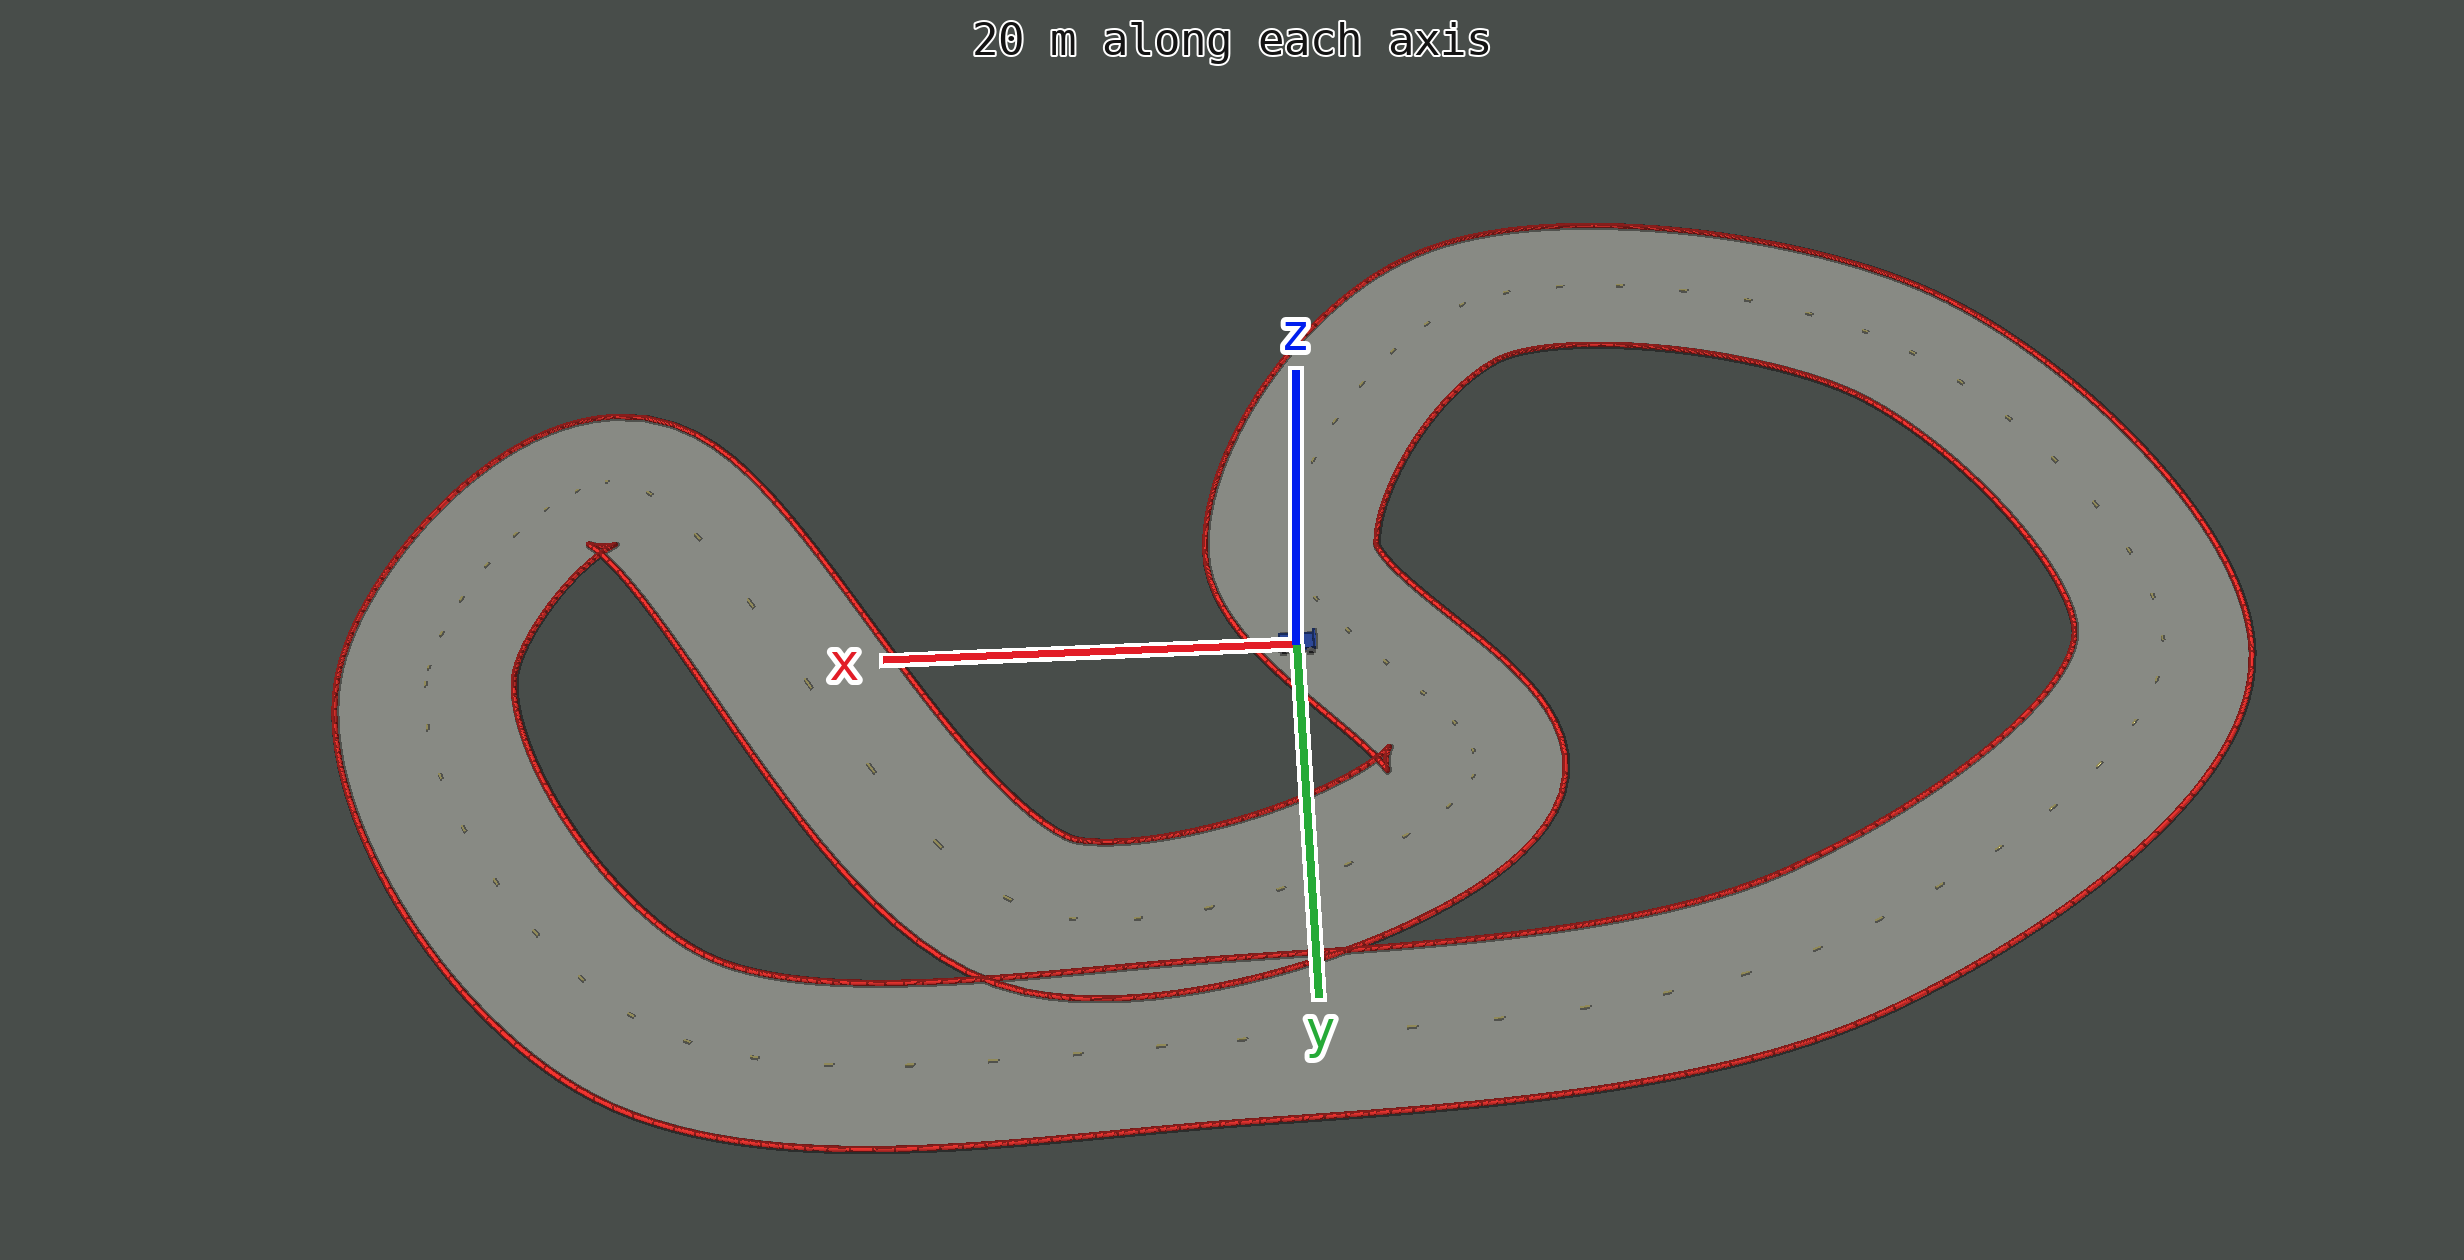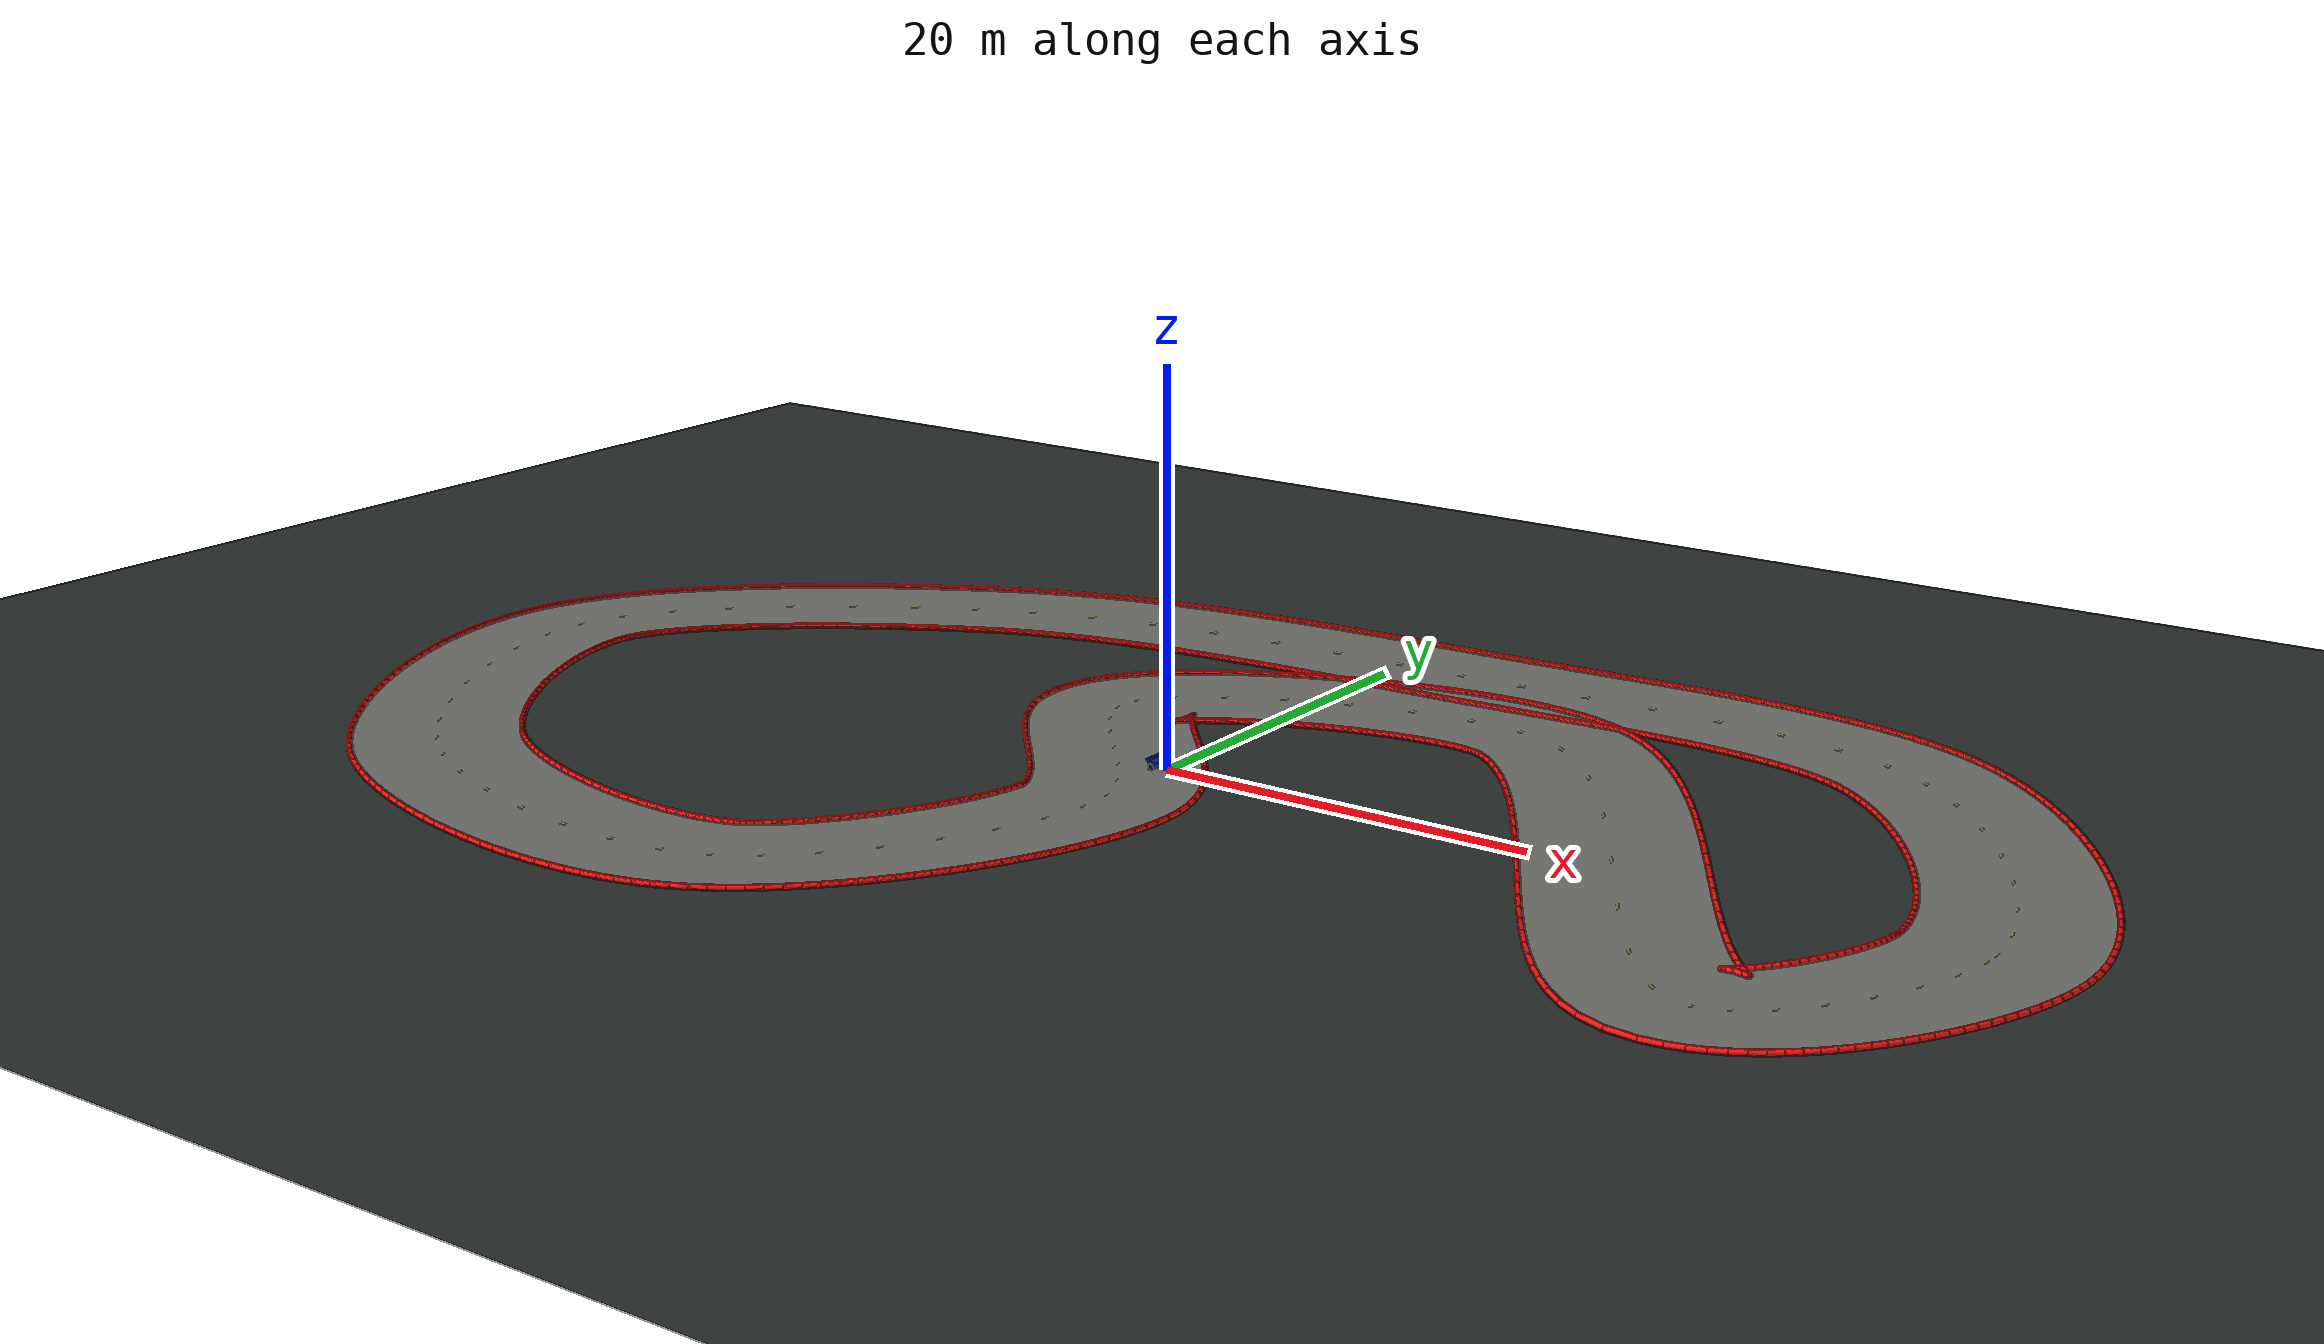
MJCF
<mujoco model="racesim_hairpin_world">
  <compiler angle="degree" autolimits="true"/>
  <option timestep="0.02" gravity="0 0 -9.81"/>
  <visual>
    <global offwidth="1280" offheight="960"/>
    <headlight ambient="0.35 0.35 0.35" diffuse="0.8 0.8 0.8"/>
  </visual>

  <include file="car.xml"/>
  <include file="hairpin_track.xml"/>

  <asset>
    <texture name="grid" type="2d" builtin="checker" width="512" height="512"
             rgb1="0.16 0.18 0.17" rgb2="0.20 0.22 0.21"/>
    <material name="ground" texture="grid" texrepeat="12 12" reflectance="0.05"/>
  </asset>

  <worldbody>
    <light name="sun" pos="0 0 30" dir="0 0 -1" diffuse="1.0 1.0 1.0" ambient="0.25 0.25 0.25"/>
    <geom name="ground" type="plane" size="90 90 0.1" material="ground"/>
    <camera name="topdown" pos="0 0 125" xyaxes="1 0 0 0 1 0" fovy="42"/>
    <camera name="follow" mode="trackcom" target="car" pos="-5 0 3" xyaxes="0 -1 0 0.5 0 0.866"/>
  </worldbody>
</mujoco>

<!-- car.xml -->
<mujoco model="simple_car">
  <default>
    <geom friction="1.2 0.02 0.001" density="600"/>
    <joint damping="0.1"/>
  </default>

  <asset>
    <material name="chassis_blue" rgba="0.05 0.18 0.55 1"/>
    <material name="wheel_dark" rgba="0.02 0.02 0.025 1"/>
  </asset>

  <worldbody>
    <body name="car" pos="0 0 0.28">
      <freejoint name="root"/>
      <geom name="chassis" type="box" size="0.9 0.45 0.12" material="chassis_blue"/>
      <geom name="nose" type="box" pos="0.75 0 0.02" size="0.45 0.25 0.06" material="chassis_blue"/>
      <geom name="rear_wing" type="box" pos="-0.85 0 0.22" size="0.08 0.55 0.04" material="chassis_blue"/>

      <body name="front_left_wheel" pos="0.65 0.48 -0.12">
        <joint name="front_left_spin" type="hinge" axis="0 1 0"/>
        <geom type="cylinder" size="0.18 0.08" euler="90 0 0" material="wheel_dark"/>
      </body>
      <body name="front_right_wheel" pos="0.65 -0.48 -0.12">
        <joint name="front_right_spin" type="hinge" axis="0 1 0"/>
        <geom type="cylinder" size="0.18 0.08" euler="90 0 0" material="wheel_dark"/>
      </body>
      <body name="rear_left_wheel" pos="-0.65 0.48 -0.12">
        <joint name="rear_left_spin" type="hinge" axis="0 1 0"/>
        <geom type="cylinder" size="0.18 0.08" euler="90 0 0" material="wheel_dark"/>
      </body>
      <body name="rear_right_wheel" pos="-0.65 -0.48 -0.12">
        <joint name="rear_right_spin" type="hinge" axis="0 1 0"/>
        <geom type="cylinder" size="0.18 0.08" euler="90 0 0" material="wheel_dark"/>
      </body>
    </body>
  </worldbody>
</mujoco>

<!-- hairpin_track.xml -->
<mujoco model="hairpin_track_visuals">
  <asset>
    <mesh name="track_surface_mesh" inertia="shell" vertex="37.75096 0.09020 0.02200 37.74721 0.40914 0.02200 37.71894 0.77717 0.02200 37.66230 1.20282 0.02200 37.57494 1.67839 0.02200 37.45578 2.19691 0.02200 37.30463 2.75209 0.02200 37.12191 3.33825 0.02200 36.90841 3.95025 0.02200 36.66523 4.58338 0.02200 36.39365 5.23330 0.02200 36.09506 5.89592 0.02200 35.77098 6.56740 0.02200 35.42300 7.24409 0.02200 35.05275 7.92244 0.02200 34.66194 8.59905 0.02200 34.25233 9.27060 0.02200 33.82575 9.93383 0.02200 33.38407 10.58553 0.02200 32.92925 11.22253 0.02200 32.46337 11.84168 0.02200 31.98857 12.43988 0.02200 31.50717 13.01401 0.02200 31.02162 13.56098 0.02200 30.53458 14.07775 0.02200 30.04897 14.56128 0.02200 29.56799 15.00863 0.02200 29.09521 15.41695 0.02200 28.63461 15.78361 0.02200 28.19070 16.10624 0.02200 27.77442 16.37932 0.02200 27.33519 16.63252 0.02200 26.87135 16.86409 0.02200 26.37104 17.08027 0.02200 25.83402 17.28040 0.02200 25.26069 17.46377 0.02200 24.65201 17.62976 0.02200 24.00933 17.77790 0.02200 23.33432 17.90798 0.02200 22.62882 18.01999 0.02200 21.89482 18.11414 0.02200 21.13435 18.19087 0.02200 20.34947 18.25078 0.02200 19.54225 18.29463 0.02200 18.71468 18.32333 0.02200 17.86875 18.33791 0.02200 17.00637 18.33947 0.02200 16.12941 18.32922 0.02200 15.23967 18.30840 0.02200 14.33889 18.27835 0.02200 13.42874 18.24043 0.02200 12.51086 18.19604 0.02200 11.58679 18.14661 0.02200 10.65803 18.09362 0.02200 9.72601 18.03857 0.02200 8.79209 17.98297 0.02200 7.85759 17.92838 0.02200 6.92372 17.87638 0.02200 5.99164 17.82857 0.02200 5.06241 17.78662 0.02200 4.14622 17.75252 0.02200 3.20846 17.72283 0.02200 2.27119 17.69428 0.02200 1.32821 17.66579 0.02200 0.38050 17.63648 0.02200 -0.57095 17.60552 0.02200 -1.52510 17.57209 0.02200 -2.48089 17.53535 0.02200 -3.43726 17.49450 0.02200 -4.39310 17.44875 0.02200 -5.34728 17.39730 0.02200 -6.29866 17.33938 0.02200 -7.24608 17.27422 0.02200 -8.18836 17.20110 0.02200 -9.12429 17.11927 0.02200 -10.05267 17.02803 0.02200 -10.97224 16.92669 0.02200 -11.88176 16.81458 0.02200 -12.77997 16.69108 0.02200 -13.66558 16.55558 0.02200 -14.53730 16.40752 0.02200 -15.39384 16.24636 0.02200 -16.23389 16.07162 0.02200 -17.05617 15.88287 0.02200 -17.85938 15.67974 0.02200 -18.64226 15.46189 0.02200 -19.40358 15.22908 0.02200 -20.14214 14.98109 0.02200 -20.85684 14.71780 0.02200 -21.54662 14.43914 0.02200 -22.23012 14.13606 0.02200 -22.88563 13.82561 0.02200 -23.57405 13.48695 0.02200 -24.27432 13.12943 0.02200 -24.98356 12.75404 0.02200 -25.69895 12.36179 0.02200 -26.41773 11.95370 0.02200 -27.13713 11.53080 0.02200 -27.85443 11.09414 0.02200 -28.56691 10.64482 0.02200 -29.27187 10.18394 0.02200 -29.96658 9.71268 0.02200 -30.64835 9.23225 0.02200 -31.31445 8.74393 0.02200 -31.96215 8.24907 0.02200 -32.58873 7.74913 0.02200 -33.19144 7.24569 0.02200 -33.76756 6.74043 0.02200 -34.31436 6.23524 0.02200 -34.82915 5.73217 0.02200 -35.30930 5.23352 0.02200 -35.75226 4.74185 0.02200 -36.15566 4.26005 0.02200 -36.51736 3.79133 0.02200 -36.83558 3.33926 0.02200 -37.10907 2.90778 0.02200 -37.33730 2.50107 0.02200 -37.52072 2.12341 0.02200 -37.66099 1.77885 0.02200 -37.76119 1.47066 0.02200 -37.82732 1.19298 0.02200 -37.86742 0.92226 0.02200 -37.89078 0.59693 0.02200 -37.89228 0.21843 0.02200 -37.86788 -0.20879 0.02200 -37.81486 -0.67970 0.02200 -37.73159 -1.18909 0.02200 -37.61735 -1.73186 0.02200 -37.47211 -2.30312 0.02200 -37.29634 -2.89824 0.02200 -37.09089 -3.51287 0.02200 -36.85690 -4.14291 0.02200 -36.59573 -4.78449 0.02200 -36.30888 -5.43393 0.02200 -35.99800 -6.08773 0.02200 -35.66481 -6.74253 0.02200 -35.31113 -7.39506 0.02200 -34.93886 -8.04218 0.02200 -34.54995 -8.68080 0.02200 -34.14645 -9.30787 0.02200 -33.73046 -9.92043 0.02200 -33.30421 -10.51549 0.02200 -32.87001 -11.09011 0.02200 -32.43031 -11.64135 0.02200 -31.98773 -12.16625 0.02200 -31.54509 -12.66188 0.02200 -31.10546 -13.12527 0.02200 -30.67227 -13.55348 0.02200 -30.24932 -13.94358 0.02200 -29.84098 -14.29274 0.02200 -29.45219 -14.59836 0.02200 -29.05442 -14.88218 0.02200 -28.61365 -15.16834 0.02200 -28.12901 -15.45631 0.02200 -27.60428 -15.74278 0.02200 -27.04323 -16.02500 0.02200 -26.44959 -16.30063 0.02200 -25.82701 -16.56767 0.02200 -25.17906 -16.82438 0.02200 -24.50929 -17.06923 0.02200 -23.82115 -17.30086 0.02200 -23.11808 -17.51805 0.02200 -22.40351 -17.71969 0.02200 -21.68081 -17.90477 0.02200 -20.95340 -18.07237 0.02200 -20.22470 -18.22164 0.02200 -19.49816 -18.35182 0.02200 -18.77729 -18.46224 0.02200 -18.06566 -18.55230 0.02200 -17.36695 -18.62154 0.02200 -16.68492 -18.66959 0.02200 -16.02348 -18.69628 0.02200 -15.38671 -18.70161 0.02200 -14.77885 -18.68587 0.02200 -14.20434 -18.64968 0.02200 -13.66782 -18.59410 0.02200 -13.17411 -18.52082 0.02200 -12.72811 -18.43225 0.02200 -12.33470 -18.33179 0.02200 -11.99838 -18.22402 0.02200 -11.71485 -18.11132 0.02200 -11.48157 -17.99771 0.02200 -11.21662 -17.84671 0.02200 -10.92464 -17.65685 0.02200 -10.61091 -17.42826 0.02200 -10.28028 -17.16197 0.02200 -9.93714 -16.85963 0.02200 -9.58538 -16.52331 0.02200 -9.22849 -16.15538 0.02200 -8.86955 -15.75836 0.02200 -8.51133 -15.33490 0.02200 -8.15631 -14.88772 0.02200 -7.80677 -14.41957 0.02200 -7.46478 -13.93327 0.02200 -7.13226 -13.43163 0.02200 -6.81101 -12.91751 0.02200 -6.50269 -12.39379 0.02200 -6.20891 -11.86343 0.02200 -5.93115 -11.32940 0.02200 -5.67085 -10.79477 0.02200 -5.42935 -10.26271 0.02200 -5.20791 -9.73650 0.02200 -5.00772 -9.21959 0.02200 -4.82983 -8.71561 0.02200 -4.67517 -8.22843 0.02200 -4.54447 -7.76223 0.02200 -4.43818 -7.32153 0.02200 -4.35639 -6.91128 0.02200 -4.29865 -6.53695 0.02200 -4.26371 -6.20452 0.02200 -4.24999 -5.98922 0.02200 -4.24867 -5.95629 0.02200 -4.25434 -5.93265 0.02200 -4.28309 -5.83276 0.02200 -4.34784 -5.66110 0.02200 -4.45616 -5.42650 0.02200 -4.61103 -5.13889 0.02200 -4.81215 -4.80762 0.02200 -5.05709 -4.44079 0.02200 -5.34217 -4.04507 0.02200 -5.66305 -3.62584 0.02200 -6.01505 -3.18739 0.02200 -6.39343 -2.73305 0.02200 -6.79346 -2.26536 0.02200 -7.21053 -1.78621 0.02200 -7.64022 -1.29683 0.02200 -8.07827 -0.79789 0.02200 -8.52067 -0.28938 0.02200 -8.96363 0.22940 0.02200 -9.40361 0.76006 0.02200 -9.83727 1.30531 0.02200 -10.26137 1.86940 0.02200 -10.67255 2.45860 0.02200 -11.06680 3.08187 0.02200 -11.43835 3.75171 0.02200 -11.77768 4.48462 0.02200 -12.06799 5.30035 0.02200 -12.28042 6.21768 0.02200 -12.37064 7.24344 0.02200 -12.28451 8.35523 0.02200 -11.99835 9.44072 0.02200 -11.55693 10.41637 0.02200 -11.04706 11.23694 0.02200 -10.48431 11.96017 0.02200 -9.88127 12.61040 0.02200 -9.24328 13.20602 0.02200 -8.57247 13.75997 0.02200 -7.86986 14.28095 0.02200 -7.13629 14.77468 0.02200 -6.37274 15.24475 0.02200 -5.58053 15.69332 0.02200 -4.76125 16.12152 0.02200 -3.91677 16.52976 0.02200 -3.04917 16.91793 0.02200 -2.16068 17.28556 0.02200 -1.25365 17.63185 0.02200 -0.33047 17.95582 0.02200 0.60641 18.25629 0.02200 1.55459 18.53191 0.02200 2.51175 18.78119 0.02200 3.47563 19.00249 0.02200 4.44415 19.19399 0.02200 5.41545 19.35365 0.02200 6.38790 19.47917 0.02200 7.36019 19.56791 0.02200 8.33137 19.61670 0.02200 9.30089 19.62174 0.02200 10.26858 19.57830 0.02200 11.23456 19.48037 0.02200 12.19890 19.32030 0.02200 13.24281 19.06423 0.02200 14.57201 18.56415 0.02200 15.85985 17.86388 0.02200 17.02660 17.04237 0.02200 18.10193 16.12695 0.02200 19.11036 15.13291 0.02200 20.06982 14.06996 0.02200 20.99271 12.94583 0.02200 21.88741 11.76783 0.02200 22.75948 10.54354 0.02200 23.61256 9.28103 0.02200 24.44895 7.98887 0.02200 25.27000 6.67615 0.02200 26.07638 5.35235 0.02200 26.86824 4.02738 0.02200 27.64530 2.71151 0.02200 28.40691 1.41538 0.02200 29.15205 0.15000 0.02200 29.87928 -1.07318 0.02200 30.58668 -2.24221 0.02200 31.27163 -3.34453 0.02200 31.93053 -4.36673 0.02200 32.55829 -5.29435 0.02200 33.14738 -6.11153 0.02200 33.68629 -6.80056 0.02200 34.15664 -7.34181 0.02200 34.52811 -7.71462 0.02200 34.75042 -7.90251 0.02200 34.74553 -7.91053 0.02200 34.42311 -7.80628 0.02200 33.97615 -7.75007 0.02200 33.61133 -7.77469 0.02200 33.49223 -7.80150 0.02200 33.44741 -7.81599 0.02200 33.46981 -7.80427 0.02200 33.54926 -7.75786 0.02200 33.67521 -7.67256 0.02200 33.83794 -7.54717 0.02200 34.02901 -7.38244 0.02200 34.24136 -7.18026 0.02200 34.46904 -6.94320 0.02200 34.70710 -6.67417 0.02200 34.95137 -6.37626 0.02200 35.19827 -6.05263 0.02200 35.44472 -5.70650 0.02200 35.68801 -5.34105 0.02200 35.92571 -4.95948 0.02200 36.15565 -4.56502 0.02200 36.37582 -4.16090 0.02200 36.58441 -3.75040 0.02200 36.77971 -3.33687 0.02200 36.96017 -2.92376 0.02200 37.12435 -2.51466 0.02200 37.27096 -2.11335 0.02200 37.39888 -1.72381 0.02200 37.50720 -1.35036 0.02200 37.59529 -0.99763 0.02200 37.66295 -0.67071 0.02200 37.71051 -0.37519 0.02200 37.73913 -0.11720 0.02200 46.24904 -0.09020 0.02200 46.23921 0.77781 0.02200 46.17355 1.65435 0.02200 46.05871 2.52579 0.02200 45.89985 3.39473 0.02200 45.70084 4.26306 0.02200 45.46466 5.13199 0.02200 45.19371 6.00210 0.02200 44.88996 6.87342 0.02200 44.55513 7.74559 0.02200 44.19075 8.61786 0.02200 43.79820 9.48921 0.02200 43.37877 10.35840 0.02200 42.93367 11.22401 0.02200 42.46406 12.08446 0.02200 41.97103 12.93808 0.02200 41.45562 13.78310 0.02200 40.91880 14.61769 0.02200 40.36149 15.43996 0.02200 39.78452 16.24799 0.02200 39.18863 17.03984 0.02200 38.57446 17.81353 0.02200 37.94249 18.56708 0.02200 37.29307 19.29848 0.02200 36.62633 20.00570 0.02200 35.94216 20.68667 0.02200 35.24014 21.33924 0.02200 34.51952 21.96118 0.02200 33.77909 22.55002 0.02200 33.01716 23.10304 0.02200 32.22558 23.62068 0.02200 31.35860 24.11999 0.02200 30.46020 24.56929 0.02200 29.54507 24.96542 0.02200 28.61631 25.31214 0.02200 27.67637 25.61328 0.02200 26.72713 25.87256 0.02200 25.77009 26.09354 0.02200 24.80644 26.27953 0.02200 23.83718 26.43366 0.02200 22.86316 26.55881 0.02200 21.88520 26.65764 0.02200 20.90409 26.73266 0.02200 19.92062 26.78620 0.02200 18.93563 26.82046 0.02200 17.94999 26.83752 0.02200 16.96463 26.83937 0.02200 15.98053 26.82791 0.02200 14.99875 26.80499 0.02200 14.02038 26.77238 0.02200 13.04660 26.73183 0.02200 12.07863 26.68504 0.02200 11.11777 26.63366 0.02200 10.16537 26.57933 0.02200 9.22284 26.52366 0.02200 8.29167 26.46823 0.02200 7.37341 26.41458 0.02200 6.46966 26.36424 0.02200 5.58215 26.31871 0.02200 4.71264 26.27942 0.02200 3.85378 26.24748 0.02200 2.94468 26.21873 0.02200 2.01345 26.19038 0.02200 1.06847 26.16182 0.02200 0.11092 26.13220 0.02200 -0.85802 26.10068 0.02200 -1.83720 26.06636 0.02200 -2.82552 26.02836 0.02200 -3.82188 25.98580 0.02200 -4.82520 25.93776 0.02200 -5.83444 25.88332 0.02200 -6.84856 25.82157 0.02200 -7.86657 25.75155 0.02200 -8.88746 25.67230 0.02200 -9.91027 25.58285 0.02200 -10.93405 25.48221 0.02200 -11.95785 25.36935 0.02200 -12.98076 25.24324 0.02200 -14.00188 25.10280 0.02200 -15.02030 24.94693 0.02200 -16.03515 24.77450 0.02200 -17.04555 24.58433 0.02200 -18.05063 24.37520 0.02200 -19.04951 24.14584 0.02200 -20.04132 23.89492 0.02200 -21.02513 23.62106 0.02200 -22.00001 23.32281 0.02200 -22.96497 22.99867 0.02200 -23.91897 22.64707 0.02200 -24.86087 22.26638 0.02200 -25.76988 21.86394 0.02200 -26.57971 21.48092 0.02200 -27.38269 21.08592 0.02200 -28.19512 20.67114 0.02200 -29.01511 20.23713 0.02200 -29.84075 19.78443 0.02200 -30.67005 19.31357 0.02200 -31.50102 18.82507 0.02200 -32.33162 18.31943 0.02200 -33.15983 17.79710 0.02200 -33.98360 17.25852 0.02200 -34.80089 16.70407 0.02200 -35.60967 16.13408 0.02200 -36.40789 15.54884 0.02200 -37.19354 14.94851 0.02200 -37.96460 14.33321 0.02200 -38.71904 13.70291 0.02200 -39.45485 13.05745 0.02200 -40.17000 12.39653 0.02200 -40.86244 11.71961 0.02200 -41.53004 11.02596 0.02200 -42.17059 10.31456 0.02200 -42.78172 9.58409 0.02200 -43.36081 8.83287 0.02200 -43.90490 8.05887 0.02200 -44.41048 7.25972 0.02200 -44.87332 6.43278 0.02200 -45.28824 5.57531 0.02200 -45.64881 4.68482 0.02200 -45.94721 3.75959 0.02200 -46.17268 2.80702 0.02200 -46.31472 1.86732 0.02200 -46.38420 0.93124 0.02200 -46.38952 0.00189 0.02200 -46.33803 -0.92062 0.02200 -46.23573 -1.83676 0.02200 -46.08756 -2.74719 0.02200 -45.89753 -3.65246 0.02200 -45.66897 -4.55290 0.02200 -45.40472 -5.44858 0.02200 -45.10720 -6.33931 0.02200 -44.77859 -7.22462 0.02200 -44.42082 -8.10383 0.02200 -44.03567 -8.97606 0.02200 -43.62483 -9.84026 0.02200 -43.18983 -10.69525 0.02200 -42.73217 -11.53971 0.02200 -42.25326 -12.37226 0.02200 -41.75441 -13.19142 0.02200 -41.23691 -13.99567 0.02200 -40.70191 -14.78344 0.02200 -40.15052 -15.55315 0.02200 -39.58371 -16.30319 0.02200 -39.00233 -17.03195 0.02200 -38.40706 -17.73782 0.02200 -37.79836 -18.41919 0.02200 -37.17647 -19.07446 0.02200 -36.54127 -19.70204 0.02200 -35.89223 -20.30028 0.02200 -35.22829 -20.86746 0.02200 -34.54781 -21.40164 0.02200 -33.84025 -21.90684 0.02200 -33.10185 -22.38679 0.02200 -32.33873 -22.84063 0.02200 -31.55233 -23.27026 0.02200 -30.74414 -23.67701 0.02200 -29.91568 -24.06183 0.02200 -29.06852 -24.42531 0.02200 -28.20434 -24.76778 0.02200 -27.32484 -25.08937 0.02200 -26.43179 -25.39002 0.02200 -25.52700 -25.66956 0.02200 -24.61231 -25.92769 0.02200 -23.68954 -26.16401 0.02200 -22.76054 -26.37805 0.02200 -21.82714 -26.56923 0.02200 -20.89111 -26.73691 0.02200 -19.95419 -26.88037 0.02200 -19.01805 -26.99878 0.02200 -18.08426 -27.09121 0.02200 -17.15430 -27.15662 0.02200 -16.22948 -27.19378 0.02200 -15.31098 -27.20127 0.02200 -14.39980 -27.17741 0.02200 -13.49674 -27.12017 0.02200 -12.60240 -27.02707 0.02200 -11.71720 -26.89503 0.02200 -10.84148 -26.72023 0.02200 -9.97561 -26.49786 0.02200 -9.12032 -26.22194 0.02200 -8.28515 -25.88868 0.02200 -7.52645 -25.52148 0.02200 -6.80192 -25.11035 0.02200 -6.10905 -24.66114 0.02200 -5.44471 -24.17811 0.02200 -4.80619 -23.66461 0.02200 -4.19122 -23.12337 0.02200 -3.59804 -22.55670 0.02200 -3.02531 -21.96663 0.02200 -2.47209 -21.35501 0.02200 -1.93774 -20.72359 0.02200 -1.42190 -20.07402 0.02200 -0.92445 -19.40793 0.02200 -0.44545 -18.72691 0.02200 0.01490 -18.03251 0.02200 0.45624 -17.32626 0.02200 0.87813 -16.60965 0.02200 1.28000 -15.88415 0.02200 1.66124 -15.15113 0.02200 2.02111 -14.41191 0.02200 2.35884 -13.66772 0.02200 2.67356 -12.91965 0.02200 2.96430 -12.16864 0.02200 3.23000 -11.41545 0.02200 3.46943 -10.66059 0.02200 3.68120 -9.90427 0.02200 3.86363 -9.14634 0.02200 4.01466 -8.38623 0.02200 4.13170 -7.62288 0.02200 4.21139 -6.85468 0.02200 4.24999 -6.01078 0.02200 4.20591 -5.07880 0.02200 4.05145 -4.12603 0.02200 3.81165 -3.23948 0.02200 3.50837 -2.41612 0.02200 3.15814 -1.64860 0.02200 2.77289 -0.92845 0.02200 2.36127 -0.24778 0.02200 1.92980 0.40002 0.02200 1.48375 1.02019 0.02200 1.02774 1.61662 0.02200 0.56603 2.19214 0.02200 0.10283 2.74862 0.02200 -0.35763 3.28713 0.02200 -0.81101 3.80808 0.02200 -1.25279 4.31127 0.02200 -1.67827 4.79586 0.02200 -2.08252 5.26041 0.02200 -2.46036 5.70274 0.02200 -2.80639 6.11979 0.02200 -3.11500 6.50735 0.02200 -3.38048 6.85973 0.02200 -3.59723 7.16920 0.02200 -3.76032 7.42531 0.02200 -3.86657 7.61411 0.02200 -3.91654 7.71763 0.02200 -3.91808 7.71466 0.02200 -3.89111 7.58495 0.02200 -3.87099 7.32020 0.02200 -3.90293 6.94136 0.02200 -4.00165 6.55928 0.02200 -4.07764 6.37779 0.02200 -4.08553 6.35975 0.02200 -4.01724 6.44410 0.02200 -3.86765 6.60320 0.02200 -3.63891 6.81532 0.02200 -3.33635 7.06422 0.02200 -2.96643 7.33787 0.02200 -2.53581 7.62726 0.02200 -2.05096 7.92544 0.02200 -1.51805 8.22697 0.02200 -0.94297 8.52739 0.02200 -0.33131 8.82298 0.02200 0.31150 9.11051 0.02200 0.98025 9.38716 0.02200 1.66978 9.65040 0.02200 2.37503 9.89789 0.02200 3.09095 10.12751 0.02200 3.81246 10.33728 0.02200 4.53444 10.52536 0.02200 5.25163 10.69010 0.02200 5.95865 10.83000 0.02200 6.64988 10.94376 0.02200 7.31948 11.03038 0.02200 7.96128 11.08919 0.02200 8.56874 11.12002 0.02200 9.13495 11.12336 0.02200 9.65258 11.10065 0.02200 10.11406 11.05455 0.02200 10.51182 10.98941 0.02200 10.75719 10.93577 0.02200 11.03459 10.83521 0.02200 11.35936 10.65308 0.02200 11.80956 10.33175 0.02200 12.35383 9.86521 0.02200 12.96598 9.25952 0.02200 13.62641 8.52628 0.02200 14.32102 7.67909 0.02200 15.03978 6.73197 0.02200 15.77542 5.69865 0.02200 16.52265 4.59241 0.02200 17.27747 3.42599 0.02200 18.03686 2.21165 0.02200 18.79848 0.96121 0.02200 19.56049 -0.31391 0.02200 20.32150 -1.60264 0.02200 21.08047 -2.89430 0.02200 21.83676 -4.17857 0.02200 22.59011 -5.44559 0.02200 23.34077 -6.68595 0.02200 24.08969 -7.89092 0.02200 24.83878 -9.05257 0.02200 25.59148 -10.16401 0.02200 26.35360 -11.21981 0.02200 27.13499 -12.21632 0.02200 27.95235 -13.15188 0.02200 28.83432 -14.02578 0.02200 29.82952 -14.83322 0.02200 31.01429 -15.54779 0.02200 32.47729 -16.08057 0.02200 34.02385 -16.24993 0.02200 35.08867 -16.14533 0.02200 35.91812 -15.94798 0.02200 36.68129 -15.67678 0.02200 37.38291 -15.34998 0.02200 38.03079 -14.98046 0.02200 38.63317 -14.57681 0.02200 39.19741 -14.14459 0.02200 39.72961 -13.68745 0.02200 40.23451 -13.20788 0.02200 40.71569 -12.70769 0.02200 41.17578 -12.18835 0.02200 41.61661 -11.65116 0.02200 42.03941 -11.09732 0.02200 42.44492 -10.52803 0.02200 42.83353 -9.94447 0.02200 43.20531 -9.34781 0.02200 43.56010 -8.73923 0.02200 43.89756 -8.11987 0.02200 44.21717 -7.49084 0.02200 44.51830 -6.85316 0.02200 44.80015 -6.20777 0.02200 45.06183 -5.55545 0.02200 45.30229 -4.89683 0.02200 45.52031 -4.23228 0.02200 45.71446 -3.56189 0.02200 45.88302 -2.88539 0.02200 46.02386 -2.20209 0.02200 46.13431 -1.51078 0.02200 46.21087 -0.80971 0.02200" face="0 331 1 0 330 331 1 332 2 1 331 332 2 333 3 2 332 333 3 334 4 3 333 334 4 335 5 4 334 335 5 336 6 5 335 336 6 337 7 6 336 337 7 338 8 7 337 338 8 339 9 8 338 339 9 340 10 9 339 340 10 341 11 10 340 341 11 342 12 11 341 342 12 343 13 12 342 343 13 344 14 13 343 344 14 345 15 14 344 345 15 346 16 15 345 346 16 347 17 16 346 347 17 348 18 17 347 348 18 349 19 18 348 349 19 350 20 19 349 350 20 351 21 20 350 351 21 352 22 21 351 352 22 353 23 22 352 353 23 354 24 23 353 354 24 355 25 24 354 355 25 356 26 25 355 356 26 357 27 26 356 357 27 358 28 27 357 358 28 359 29 28 358 359 29 360 30 29 359 360 30 361 31 30 360 361 31 362 32 31 361 362 32 363 33 32 362 363 33 364 34 33 363 364 34 365 35 34 364 365 35 366 36 35 365 366 36 367 37 36 366 367 37 368 38 37 367 368 38 369 39 38 368 369 39 370 40 39 369 370 40 371 41 40 370 371 41 372 42 41 371 372 42 373 43 42 372 373 43 374 44 43 373 374 44 375 45 44 374 375 45 376 46 45 375 376 46 377 47 46 376 377 47 378 48 47 377 378 48 379 49 48 378 379 49 380 50 49 379 380 50 381 51 50 380 381 51 382 52 51 381 382 52 383 53 52 382 383 53 384 54 53 383 384 54 385 55 54 384 385 55 386 56 55 385 386 56 387 57 56 386 387 57 388 58 57 387 388 58 389 59 58 388 389 59 390 60 59 389 390 60 391 61 60 390 391 61 392 62 61 391 392 62 393 63 62 392 393 63 394 64 63 393 394 64 395 65 64 394 395 65 396 66 65 395 396 66 397 67 66 396 397 67 398 68 67 397 398 68 399 69 68 398 399 69 400 70 69 399 400 70 401 71 70 400 401 71 402 72 71 401 402 72 403 73 72 402 403 73 404 74 73 403 404 74 405 75 74 404 405 75 406 76 75 405 406 76 407 77 76 406 407 77 408 78 77 407 408 78 409 79 78 408 409 79 410 80 79 409 410 80 411 81 80 410 411 81 412 82 81 411 412 82 413 83 82 412 413 83 414 84 83 413 414 84 415 85 84 414 415 85 416 86 85 415 416 86 417 87 86 416 417 87 418 88 87 417 418 88 419 89 88 418 419 89 420 90 89 419 420 90 421 91 90 420 421 91 422 92 91 421 422 92 423 93 92 422 423 93 424 94 93 423 424 94 425 95 94 424 425 95 426 96 95 425 426 96 427 97 96 426 427 97 428 98 97 427 428 98 429 99 98 428 429 99 430 100 99 429 430 100 431 101 100 430 431 101 432 102 101 431 432 102 433 103 102 432 433 103 434 104 103 433 434 104 435 105 104 434 435 105 436 106 105 435 436 106 437 107 106 436 437 107 438 108 107 437 438 108 439 109 108 438 439 109 440 110 109 439 440 110 441 111 110 440 441 111 442 112 111 441 442 112 443 113 112 442 443 113 444 114 113 443 444 114 445 115 114 444 445 115 446 116 115 445 446 116 447 117 116 446 447 117 448 118 117 447 448 118 449 119 118 448 449 119 450 120 119 449 450 120 451 121 120 450 451 121 452 122 121 451 452 122 453 123 122 452 453 123 454 124 123 453 454 124 455 125 124 454 455 125 456 126 125 455 456 126 457 127 126 456 457 127 458 128 127 457 458 128 459 129 128 458 459 129 460 130 129 459 460 130 461 131 130 460 461 131 462 132 131 461 462 132 463 133 132 462 463 133 464 134 133 463 464 134 465 135 134 464 465 135 466 136 135 465 466 136 467 137 136 466 467 137 468 138 137 467 468 138 469 139 138 468 469 139 470 140 139 469 470 140 471 141 140 470 471 141 472 142 141 471 472 142 473 143 142 472 473 143 474 144 143 473 474 144 475 145 144 474 475 145 476 146 145 475 476 146 477 147 146 476 477 147 478 148 147 477 478 148 479 149 148 478 479 149 480 150 149 479 480 150 481 151 150 480 481 151 482 152 151 481 482 152 483 153 152 482 483 153 484 154 153 483 484 154 485 155 154 484 485 155 486 156 155 485 486 156 487 157 156 486 487 157 488 158 157 487 488 158 489 159 158 488 489 159 490 160 159 489 490 160 491 161 160 490 491 161 492 162 161 491 492 162 493 163 162 492 493 163 494 164 163 493 494 164 495 165 164 494 495 165 496 166 165 495 496 166 497 167 166 496 497 167 498 168 167 497 498 168 499 169 168 498 499 169 500 170 169 499 500 170 501 171 170 500 501 171 502 172 171 501 502 172 503 173 172 502 503 173 504 174 173 503 504 174 505 175 174 504 505 175 506 176 175 505 506 176 507 177 176 506 507 177 508 178 177 507 508 178 509 179 178 508 509 179 510 180 179 509 510 180 511 181 180 510 511 181 512 182 181 511 512 182 513 183 182 512 513 183 514 184 183 513 514 184 515 185 184 514 515 185 516 186 185 515 516 186 517 187 186 516 517 187 518 188 187 517 518 188 519 189 188 518 519 189 520 190 189 519 520 190 521 191 190 520 521 191 522 192 191 521 522 192 523 193 192 522 523 193 524 194 193 523 524 194 525 195 194 524 525 195 526 196 195 525 526 196 527 197 196 526 527 197 528 198 197 527 528 198 529 199 198 528 529 199 530 200 199 529 530 200 531 201 200 530 531 201 532 202 201 531 532 202 533 203 202 532 533 203 534 204 203 533 534 204 535 205 204 534 535 205 536 206 205 535 536 206 537 207 206 536 537 207 538 208 207 537 538 208 539 209 208 538 539 209 540 210 209 539 540 210 541 211 210 540 541 211 542 212 211 541 542 212 543 213 212 542 543 213 544 214 213 543 544 214 545 215 214 544 545 215 546 216 215 545 546 216 547 217 216 546 547 217 548 218 217 547 548 218 549 219 218 548 549 219 550 220 219 549 550 220 551 221 220 550 551 221 552 222 221 551 552 222 553 223 222 552 553 223 554 224 223 553 554 224 555 225 224 554 555 225 556 226 225 555 556 226 557 227 226 556 557 227 558 228 227 557 558 228 559 229 228 558 559 229 560 230 229 559 560 230 561 231 230 560 561 231 562 232 231 561 562 232 563 233 232 562 563 233 564 234 233 563 564 234 565 235 234 564 565 235 566 236 235 565 566 236 567 237 236 566 567 237 568 238 237 567 568 238 569 239 238 568 569 239 570 240 239 569 570 240 571 241 240 570 571 241 572 242 241 571 572 242 573 243 242 572 573 243 574 244 243 573 574 244 575 245 244 574 575 245 576 246 245 575 576 246 577 247 246 576 577 247 578 248 247 577 578 248 579 249 248 578 579 249 580 250 249 579 580 250 581 251 250 580 581 251 582 252 251 581 582 252 583 253 252 582 583 253 584 254 253 583 584 254 585 255 254 584 585 255 586 256 255 585 586 256 587 257 256 586 587 257 588 258 257 587 588 258 589 259 258 588 589 259 590 260 259 589 590 260 591 261 260 590 591 261 592 262 261 591 592 262 593 263 262 592 593 263 594 264 263 593 594 264 595 265 264 594 595 265 596 266 265 595 596 266 597 267 266 596 597 267 598 268 267 597 598 268 599 269 268 598 599 269 600 270 269 599 600 270 601 271 270 600 601 271 602 272 271 601 602 272 603 273 272 602 603 273 604 274 273 603 604 274 605 275 274 604 605 275 606 276 275 605 606 276 607 277 276 606 607 277 608 278 277 607 608 278 609 279 278 608 609 279 610 280 279 609 610 280 611 281 280 610 611 281 612 282 281 611 612 282 613 283 282 612 613 283 614 284 283 613 614 284 615 285 284 614 615 285 616 286 285 615 616 286 617 287 286 616 617 287 618 288 287 617 618 288 619 289 288 618 619 289 620 290 289 619 620 290 621 291 290 620 621 291 622 292 291 621 622 292 623 293 292 622 623 293 624 294 293 623 624 294 625 295 294 624 625 295 626 296 295 625 626 296 627 297 296 626 627 297 628 298 297 627 628 298 629 299 298 628 629 299 630 300 299 629 630 300 631 301 300 630 631 301 632 302 301 631 632 302 633 303 302 632 633 303 634 304 303 633 634 304 635 305 304 634 635 305 636 306 305 635 636 306 637 307 306 636 637 307 638 308 307 637 638 308 639 309 308 638 639 309 640 310 309 639 640 310 641 311 310 640 641 311 642 312 311 641 642 312 643 313 312 642 643 313 644 314 313 643 644 314 645 315 314 644 645 315 646 316 315 645 646 316 647 317 316 646 647 317 648 318 317 647 648 318 649 319 318 648 649 319 650 320 319 649 650 320 651 321 320 650 651 321 652 322 321 651 652 322 653 323 322 652 653 323 654 324 323 653 654 324 655 325 324 654 655 325 656 326 325 655 656 326 657 327 326 656 657 327 658 328 327 657 658 328 659 329 328 658 659 329 330 0 329 659 330"/>
    <material name="track_asphalt" rgba="0.48 0.49 0.46 1" emission="0.08"/>
    <material name="track_boundary" rgba="0.95 0.08 0.06 1" emission="0.05"/>
    <material name="track_centerline" rgba="1.0 0.95 0.55 1" emission="0.15"/>
  </asset>
  <worldbody>
    <geom name="track_surface" type="mesh" mesh="track_surface_mesh" material="track_asphalt" contype="0" conaffinity="0"/>
    <geom name="track_left_boundary_000" type="capsule" fromto="37.75096 0.09020 0.09 37.74721 0.40914 0.09" size="0.14" material="track_boundary" contype="0" conaffinity="0"/>
    <geom name="track_left_boundary_001" type="capsule" fromto="37.74721 0.40914 0.09 37.71894 0.77717 0.09" size="0.14" material="track_boundary" contype="0" conaffinity="0"/>
    <geom name="track_left_boundary_002" type="capsule" fromto="37.71894 0.77717 0.09 37.66230 1.20282 0.09" size="0.14" material="track_boundary" contype="0" conaffinity="0"/>
    <geom name="track_left_boundary_003" type="capsule" fromto="37.66230 1.20282 0.09 37.57494 1.67839 0.09" size="0.14" material="track_boundary" contype="0" conaffinity="0"/>
    <geom name="track_left_boundary_004" type="capsule" fromto="37.57494 1.67839 0.09 37.45578 2.19691 0.09" size="0.14" material="track_boundary" contype="0" conaffinity="0"/>
    <geom name="track_left_boundary_005" type="capsule" fromto="37.45578 2.19691 0.09 37.30463 2.75209 0.09" size="0.14" material="track_boundary" contype="0" conaffinity="0"/>
    <geom name="track_left_boundary_006" type="capsule" fromto="37.30463 2.75209 0.09 37.12191 3.33825 0.09" size="0.14" material="track_boundary" contype="0" conaffinity="0"/>
    <geom name="track_left_boundary_007" type="capsule" fromto="37.12191 3.33825 0.09 36.90841 3.95025 0.09" size="0.14" material="track_boundary" contype="0" conaffinity="0"/>
    <geom name="track_left_boundary_008" type="capsule" fromto="36.90841 3.95025 0.09 36.66523 4.58338 0.09" size="0.14" material="track_boundary" contype="0" conaffinity="0"/>
    <geom name="track_left_boundary_009" type="capsule" fromto="36.66523 4.58338 0.09 36.39365 5.23330 0.09" size="0.14" material="track_boundary" contype="0" conaffinity="0"/>
    <geom name="track_left_boundary_010" type="capsule" fromto="36.39365 5.23330 0.09 36.09506 5.89592 0.09" size="0.14" material="track_boundary" contype="0" conaffinity="0"/>
    <geom name="track_left_boundary_011" type="capsule" fromto="36.09506 5.89592 0.09 35.77098 6.56740 0.09" size="0.14" material="track_boundary" contype="0" conaffinity="0"/>
    <geom name="track_left_boundary_012" type="capsule" fromto="35.77098 6.56740 0.09 35.42300 7.24409 0.09" size="0.14" material="track_boundary" contype="0" conaffinity="0"/>
    <geom name="track_left_boundary_013" type="capsule" fromto="35.42300 7.24409 0.09 35.05275 7.92244 0.09" size="0.14" material="track_boundary" contype="0" conaffinity="0"/>
    <geom name="track_left_boundary_014" type="capsule" fromto="35.05275 7.92244 0.09 34.66194 8.59905 0.09" size="0.14" material="track_boundary" contype="0" conaffinity="0"/>
    <geom name="track_left_boundary_015" type="capsule" fromto="34.66194 8.59905 0.09 34.25233 9.27060 0.09" size="0.14" material="track_boundary" contype="0" conaffinity="0"/>
    <geom name="track_left_boundary_016" type="capsule" fromto="34.25233 9.27060 0.09 33.82575 9.93383 0.09" size="0.14" material="track_boundary" contype="0" conaffinity="0"/>
    <geom name="track_left_boundary_017" type="capsule" fromto="33.82575 9.93383 0.09 33.38407 10.58553 0.09" size="0.14" material="track_boundary" contype="0" conaffinity="0"/>
    <geom name="track_left_boundary_018" type="capsule" fromto="33.38407 10.58553 0.09 32.92925 11.22253 0.09" size="0.14" material="track_boundary" contype="0" conaffinity="0"/>
    <geom name="track_left_boundary_019" type="capsule" fromto="32.92925 11.22253 0.09 32.46337 11.84168 0.09" size="0.14" material="track_boundary" contype="0" conaffinity="0"/>
    <geom name="track_left_boundary_020" type="capsule" fromto="32.46337 11.84168 0.09 31.98857 12.43988 0.09" size="0.14" material="track_boundary" contype="0" conaffinity="0"/>
    <geom name="track_left_boundary_021" type="capsule" fromto="31.98857 12.43988 0.09 31.50717 13.01401 0.09" size="0.14" material="track_boundary" contype="0" conaffinity="0"/>
    <geom name="track_left_boundary_022" type="capsule" fromto="31.50717 13.01401 0.09 31.02162 13.56098 0.09" size="0.14" material="track_boundary" contype="0" conaffinity="0"/>
    <geom name="track_left_boundary_023" type="capsule" fromto="31.02162 13.56098 0.09 30.53458 14.07775 0.09" size="0.14" material="track_boundary" contype="0" conaffinity="0"/>
    <geom name="track_left_boundary_024" type="capsule" fromto="30.53458 14.07775 0.09 30.04897 14.56128 0.09" size="0.14" material="track_boundary" contype="0" conaffinity="0"/>
    <geom name="track_left_boundary_025" type="capsule" fromto="30.04897 14.56128 0.09 29.56799 15.00863 0.09" size="0.14" material="track_boundary" contype="0" conaffinity="0"/>
    <geom name="track_left_boundary_026" type="capsule" fromto="29.56799 15.00863 0.09 29.09521 15.41695 0.09" size="0.14" material="track_boundary" contype="0" conaffinity="0"/>
    <geom name="track_left_boundary_027" type="capsule" fromto="29.09521 15.41695 0.09 28.63461 15.78361 0.09" size="0.14" material="track_boundary" contype="0" conaffinity="0"/>
    <geom name="track_left_boundary_028" type="capsule" fromto="28.63461 15.78361 0.09 28.19070 16.10624 0.09" size="0.14" material="track_boundary" contype="0" conaffinity="0"/>
    <geom name="track_left_boundary_029" type="capsule" fromto="28.19070 16.10624 0.09 27.77442 16.37932 0.09" size="0.14" material="track_boundary" contype="0" conaffinity="0"/>
    <geom name="track_left_boundary_030" type="capsule" fromto="27.77442 16.37932 0.09 27.33519 16.63252 0.09" size="0.14" material="track_boundary" contype="0" conaffinity="0"/>
    <geom name="track_left_boundary_031" type="capsule" fromto="27.33519 16.63252 0.09 26.87135 16.86409 0.09" size="0.14" material="track_boundary" contype="0" conaffinity="0"/>
    <geom name="track_left_boundary_032" type="capsule" fromto="26.87135 16.86409 0.09 26.37104 17.08027 0.09" size="0.14" material="track_boundary" contype="0" conaffinity="0"/>
    <geom name="track_left_boundary_033" type="capsule" fromto="26.37104 17.08027 0.09 25.83402 17.28040 0.09" size="0.14" material="track_boundary" contype="0" conaffinity="0"/>
    <geom name="track_left_boundary_034" type="capsule" fromto="25.83402 17.28040 0.09 25.26069 17.46377 0.09" size="0.14" material="track_boundary" contype="0" conaffinity="0"/>
    <geom name="track_left_boundary_035" type="capsule" fromto="25.26069 17.46377 0.09 24.65201 17.62976 0.09" size="0.14" material="track_boundary" contype="0" conaffinity="0"/>
    <geom name="track_left_boundary_036" type="capsule" fromto="24.65201 17.62976 0.09 24.00933 17.77790 0.09" size="0.14" material="track_boundary" contype="0" conaffinity="0"/>
    <geom name="track_left_boundary_037" type="capsule" fromto="24.00933 17.77790 0.09 23.33432 17.90798 0.09" size="0.14" material="track_boundary" contype="0" conaffinity="0"/>
    <geom name="track_left_boundary_038" type="capsule" fromto="23.33432 17.90798 0.09 22.62882 18.01999 0.09" size="0.14" material="track_boundary" contype="0" conaffinity="0"/>
    <geom name="track_left_boundary_039" type="capsule" fromto="22.62882 18.01999 0.09 21.89482 18.11414 0.09" size="0.14" material="track_boundary" contype="0" conaffinity="0"/>
    <geom name="track_left_boundary_040" type="capsule" fromto="21.89482 18.11414 0.09 21.13435 18.19087 0.09" size="0.14" material="track_boundary" contype="0" conaffinity="0"/>
    <geom name="track_left_boundary_041" type="capsule" fromto="21.13435 18.19087 0.09 20.34947 18.25078 0.09" size="0.14" material="track_boundary" contype="0" conaffinity="0"/>
    <geom name="track_left_boundary_042" type="capsule" fromto="20.34947 18.25078 0.09 19.54225 18.29463 0.09" size="0.14" material="track_boundary" contype="0" conaffinity="0"/>
    <geom name="track_left_boundary_043" type="capsule" fromto="19.54225 18.29463 0.09 18.71468 18.32333 0.09" size="0.14" material="track_boundary" contype="0" conaffinity="0"/>
    <geom name="track_left_boundary_044" type="capsule" fromto="18.71468 18.32333 0.09 17.86875 18.33791 0.09" size="0.14" material="track_boundary" contype="0" conaffinity="0"/>
    <geom name="track_left_boundary_045" type="capsule" fromto="17.86875 18.33791 0.09 17.00637 18.33947 0.09" size="0.14" material="track_boundary" contype="0" conaffinity="0"/>
    <geom name="track_left_boundary_046" type="capsule" fromto="17.00637 18.33947 0.09 16.12941 18.32922 0.09" size="0.14" material="track_boundary" contype="0" conaffinity="0"/>
    <geom name="track_left_boundary_047" type="capsule" fromto="16.12941 18.32922 0.09 15.23967 18.30840 0.09" size="0.14" material="track_boundary" contype="0" conaffinity="0"/>
    <geom name="track_left_boundary_048" type="capsule" fromto="15.23967 18.30840 0.09 14.33889 18.27835 0.09" size="0.14" material="track_boundary" contype="0" conaffinity="0"/>
    <geom name="track_left_boundary_049" type="capsule" fromto="14.33889 18.27835 0.09 13.42874 18.24043 0.09" size="0.14" material="track_boundary" contype="0" conaffinity="0"/>
    <geom name="track_left_boundary_050" type="capsule" fromto="13.42874 18.24043 0.09 12.51086 18.19604 0.09" size="0.14" material="track_boundary" contype="0" conaffinity="0"/>
    <geom name="track_left_boundary_051" type="capsule" fromto="12.51086 18.19604 0.09 11.58679 18.14661 0.09" size="0.14" material="track_boundary" contype="0" conaffinity="0"/>
    <geom name="track_left_boundary_052" type="capsule" fromto="11.58679 18.14661 0.09 10.65803 18.09362 0.09" size="0.14" material="track_boundary" contype="0" conaffinity="0"/>
    <geom name="track_left_boundary_053" type="capsule" fromto="10.65803 18.09362 0.09 9.72601 18.03857 0.09" size="0.14" material="track_boundary" contype="0" conaffinity="0"/>
    <geom name="track_left_boundary_054" type="capsule" fromto="9.72601 18.03857 0.09 8.79209 17.98297 0.09" size="0.14" material="track_boundary" contype="0" conaffinity="0"/>
    <geom name="track_left_boundary_055" type="capsule" fromto="8.79209 17.98297 0.09 7.85759 17.92838 0.09" size="0.14" material="track_boundary" contype="0" conaffinity="0"/>
    <geom name="track_left_boundary_056" type="capsule" fromto="7.85759 17.92838 0.09 6.92372 17.87638 0.09" size="0.14" material="track_boundary" contype="0" conaffinity="0"/>
    <geom name="track_left_boundary_057" type="capsule" fromto="6.92372 17.87638 0.09 5.99164 17.82857 0.09" size="0.14" material="track_boundary" contype="0" conaffinity="0"/>
    <geom name="track_left_boundary_058" type="capsule" fromto="5.99164 17.82857 0.09 5.06241 17.78662 0.09" size="0.14" material="track_boundary" contype="0" conaffinity="0"/>
    <geom name="track_left_boundary_059" type="capsule" fromto="5.06241 17.78662 0.09 4.14622 17.75252 0.09" size="0.14" material="track_boundary" contype="0" conaffinity="0"/>
    <geom name="track_left_boundary_060" type="capsule" fromto="4.14622 17.75252 0.09 3.20846 17.72283 0.09" size="0.14" material="track_boundary" contype="0" conaffinity="0"/>
    <geom name="track_left_boundary_061" type="capsule" fromto="3.20846 17.72283 0.09 2.27119 17.69428 0.09" size="0.14" material="track_boundary" contype="0" conaffinity="0"/>
    <geom name="track_left_boundary_062" type="capsule" fromto="2.27119 17.69428 0.09 1.32821 17.66579 0.09" size="0.14" material="track_boundary" contype="0" conaffinity="0"/>
    <geom name="track_left_boundary_063" type="capsule" fromto="1.32821 17.66579 0.09 0.38050 17.63648 0.09" size="0.14" material="track_boundary" contype="0" conaffinity="0"/>
    <geom name="track_left_boundary_064" type="capsule" fromto="0.38050 17.63648 0.09 -0.57095 17.60552 0.09" size="0.14" material="track_boundary" contype="0" conaffinity="0"/>
    <geom name="track_left_boundary_065" type="capsule" fromto="-0.57095 17.60552 0.09 -1.52510 17.57209 0.09" size="0.14" material="track_boundary" contype="0" conaffinity="0"/>
    <geom name="track_left_boundary_066" type="capsule" fromto="-1.52510 17.57209 0.09 -2.48089 17.53535 0.09" size="0.14" material="track_boundary" contype="0" conaffinity="0"/>
    <geom name="track_left_boundary_067" type="capsule" fromto="-2.48089 17.53535 0.09 -3.43726 17.49450 0.09" size="0.14" material="track_boundary" contype="0" conaffinity="0"/>
    <geom name="track_left_boundary_068" type="capsule" fromto="-3.43726 17.49450 0.09 -4.39310 17.44875 0.09" size="0.14" material="track_boundary" contype="0" conaffinity="0"/>
    <geom name="track_left_boundary_069" type="capsule" fromto="-4.39310 17.44875 0.09 -5.34728 17.39730 0.09" size="0.14" material="track_boundary" contype="0" conaffinity="0"/>
    <geom name="track_left_boundary_070" type="capsule" fromto="-5.34728 17.39730 0.09 -6.29866 17.33938 0.09" size="0.14" material="track_boundary" contype="0" conaffinity="0"/>
    <geom name="track_left_boundary_071" type="capsule" fromto="-6.29866 17.33938 0.09 -7.24608 17.27422 0.09" size="0.14" material="track_boundary" contype="0" conaffinity="0"/>
    <geom name="track_left_boundary_072" type="capsule" fromto="-7.24608 17.27422 0.09 -8.18836 17.20110 0.09" size="0.14" material="track_boundary" contype="0" conaffinity="0"/>
    <geom name="track_left_boundary_073" type="capsule" fromto="-8.18836 17.20110 0.09 -9.12429 17.11927 0.09" size="0.14" material="track_boundary" contype="0" conaffinity="0"/>
    <geom name="track_left_boundary_074" type="capsule" fromto="-9.12429 17.11927 0.09 -10.05267 17.02803 0.09" size="0.14" material="track_boundary" contype="0" conaffinity="0"/>
    <geom name="track_left_boundary_075" type="capsule" fromto="-10.05267 17.02803 0.09 -10.97224 16.92669 0.09" size="0.14" material="track_boundary" contype="0" conaffinity="0"/>
    <geom name="track_left_boundary_076" type="capsule" fromto="-10.97224 16.92669 0.09 -11.88176 16.81458 0.09" size="0.14" material="track_boundary" contype="0" conaffinity="0"/>
    <geom name="track_left_boundary_077" type="capsule" fromto="-11.88176 16.81458 0.09 -12.77997 16.69108 0.09" size="0.14" material="track_boundary" contype="0" conaffinity="0"/>
    <geom name="track_left_boundary_078" type="capsule" fromto="-12.77997 16.69108 0.09 -13.66558 16.55558 0.09" size="0.14" material="track_boundary" contype="0" conaffinity="0"/>
    <geom name="track_left_boundary_079" type="capsule" fromto="-13.66558 16.55558 0.09 -14.53730 16.40752 0.09" size="0.14" material="track_boundary" contype="0" conaffinity="0"/>
    <geom name="track_left_boundary_080" type="capsule" fromto="-14.53730 16.40752 0.09 -15.39384 16.24636 0.09" size="0.14" material="track_boundary" contype="0" conaffinity="0"/>
    <geom name="track_left_boundary_081" type="capsule" fromto="-15.39384 16.24636 0.09 -16.23389 16.07162 0.09" size="0.14" material="track_boundary" contype="0" conaffinity="0"/>
    <geom name="track_left_boundary_082" type="capsule" fromto="-16.23389 16.07162 0.09 -17.05617 15.88287 0.09" size="0.14" material="track_boundary" contype="0" conaffinity="0"/>
    <geom name="track_left_boundary_083" type="capsule" fromto="-17.05617 15.88287 0.09 -17.85938 15.67974 0.09" size="0.14" material="track_boundary" contype="0" conaffinity="0"/>
    <geom name="track_left_boundary_084" type="capsule" fromto="-17.85938 15.67974 0.09 -18.64226 15.46189 0.09" size="0.14" material="track_boundary" contype="0" conaffinity="0"/>
    <geom name="track_left_boundary_085" type="capsule" fromto="-18.64226 15.46189 0.09 -19.40358 15.22908 0.09" size="0.14" material="track_boundary" contype="0" conaffinity="0"/>
    <geom name="track_left_boundary_086" type="capsule" fromto="-19.40358 15.22908 0.09 -20.14214 14.98109 0.09" size="0.14" material="track_boundary" contype="0" conaffinity="0"/>
    <geom name="track_left_boundary_087" type="capsule" fromto="-20.14214 14.98109 0.09 -20.85684 14.71780 0.09" size="0.14" material="track_boundary" contype="0" conaffinity="0"/>
    <geom name="track_left_boundary_088" type="capsule" fromto="-20.85684 14.71780 0.09 -21.54662 14.43914 0.09" size="0.14" material="track_boundary" contype="0" conaffinity="0"/>
    <geom name="track_left_boundary_089" type="capsule" fromto="-21.54662 14.43914 0.09 -22.23012 14.13606 0.09" size="0.14" material="track_boundary" contype="0" conaffinity="0"/>
    <geom name="track_left_boundary_090" type="capsule" fromto="-22.23012 14.13606 0.09 -22.88563 13.82561 0.09" size="0.14" material="track_boundary" contype="0" conaffinity="0"/>
    <geom name="track_left_boundary_091" type="capsule" fromto="-22.88563 13.82561 0.09 -23.57405 13.48695 0.09" size="0.14" material="track_boundary" contype="0" conaffinity="0"/>
    <geom name="track_left_boundary_092" type="capsule" fromto="-23.57405 13.48695 0.09 -24.27432 13.12943 0.09" size="0.14" material="track_boundary" contype="0" conaffinity="0"/>
    <geom name="track_left_boundary_093" type="capsule" fromto="-24.27432 13.12943 0.09 -24.98356 12.75404 0.09" size="0.14" material="track_boundary" contype="0" conaffinity="0"/>
    <geom name="track_left_boundary_094" type="capsule" fromto="-24.98356 12.75404 0.09 -25.69895 12.36179 0.09" size="0.14" material="track_boundary" contype="0" conaffinity="0"/>
    <geom name="track_left_boundary_095" type="capsule" fromto="-25.69895 12.36179 0.09 -26.41773 11.95370 0.09" size="0.14" material="track_boundary" contype="0" conaffinity="0"/>
    <geom name="track_left_boundary_096" type="capsule" fromto="-26.41773 11.95370 0.09 -27.13713 11.53080 0.09" size="0.14" material="track_boundary" contype="0" conaffinity="0"/>
    <geom name="track_left_boundary_097" type="capsule" fromto="-27.13713 11.53080 0.09 -27.85443 11.09414 0.09" size="0.14" material="track_boundary" contype="0" conaffinity="0"/>
    <geom name="track_left_boundary_098" type="capsule" fromto="-27.85443 11.09414 0.09 -28.56691 10.64482 0.09" size="0.14" material="track_boundary" contype="0" conaffinity="0"/>
    <geom name="track_left_boundary_099" type="capsule" fromto="-28.56691 10.64482 0.09 -29.27187 10.18394 0.09" size="0.14" material="track_boundary" contype="0" conaffinity="0"/>
    <geom name="track_left_boundary_100" type="capsule" fromto="-29.27187 10.18394 0.09 -29.96658 9.71268 0.09" size="0.14" material="track_boundary" contype="0" conaffinity="0"/>
    <geom name="track_left_boundary_101" type="capsule" fromto="-29.96658 9.71268 0.09 -30.64835 9.23225 0.09" size="0.14" material="track_boundary" contype="0" conaffinity="0"/>
    <geom name="track_left_boundary_102" type="capsule" fromto="-30.64835 9.23225 0.09 -31.31445 8.74393 0.09" size="0.14" material="track_boundary" contype="0" conaffinity="0"/>
    <geom name="track_left_boundary_103" type="capsule" fromto="-31.31445 8.74393 0.09 -31.96215 8.24907 0.09" size="0.14" material="track_boundary" contype="0" conaffinity="0"/>
    <geom name="track_left_boundary_104" type="capsule" fromto="-31.96215 8.24907 0.09 -32.58873 7.74913 0.09" size="0.14" material="track_boundary" contype="0" conaffinity="0"/>
    <geom name="track_left_boundary_105" type="capsule" fromto="-32.58873 7.74913 0.09 -33.19144 7.24569 0.09" size="0.14" material="track_boundary" contype="0" conaffinity="0"/>
    <geom name="track_left_boundary_106" type="capsule" fromto="-33.19144 7.24569 0.09 -33.76756 6.74043 0.09" size="0.14" material="track_boundary" contype="0" conaffinity="0"/>
    <geom name="track_left_boundary_107" type="capsule" fromto="-33.76756 6.74043 0.09 -34.31436 6.23524 0.09" size="0.14" material="track_boundary" contype="0" conaffinity="0"/>
    <geom name="track_left_boundary_108" type="capsule" fromto="-34.31436 6.23524 0.09 -34.82915 5.73217 0.09" size="0.14" material="track_boundary" contype="0" conaffinity="0"/>
    <geom name="track_left_boundary_109" type="capsule" fromto="-34.82915 5.73217 0.09 -35.30930 5.23352 0.09" size="0.14" material="track_boundary" contype="0" conaffinity="0"/>
    <geom name="track_left_boundary_110" type="capsule" fromto="-35.30930 5.23352 0.09 -35.75226 4.74185 0.09" size="0.14" material="track_boundary" contype="0" conaffinity="0"/>
    <geom name="track_left_boundary_111" type="capsule" fromto="-35.75226 4.74185 0.09 -36.15566 4.26005 0.09" size="0.14" material="track_boundary" contype="0" conaffinity="0"/>
    <geom name="track_left_boundary_112" type="capsule" fromto="-36.15566 4.26005 0.09 -36.51736 3.79133 0.09" size="0.14" material="track_boundary" contype="0" conaffinity="0"/>
    <geom name="track_left_boundary_113" type="capsule" fromto="-36.51736 3.79133 0.09 -36.83558 3.33926 0.09" size="0.14" material="track_boundary" contype="0" conaffinity="0"/>
    <geom name="track_left_boundary_114" type="capsule" fromto="-36.83558 3.33926 0.09 -37.10907 2.90778 0.09" size="0.14" material="track_boundary" contype="0" conaffinity="0"/>
    <geom name="track_left_boundary_115" type="capsule" fromto="-37.10907 2.90778 0.09 -37.33730 2.50107 0.09" size="0.14" material="track_boundary" contype="0" conaffinity="0"/>
    <geom name="track_left_boundary_116" type="capsule" fromto="-37.33730 2.50107 0.09 -37.52072 2.12341 0.09" size="0.14" material="track_boundary" contype="0" conaffinity="0"/>
    <geom name="track_left_boundary_117" type="capsule" fromto="-37.52072 2.12341 0.09 -37.66099 1.77885 0.09" size="0.14" material="track_boundary" contype="0" conaffinity="0"/>
    <geom name="track_left_boundary_118" type="capsule" fromto="-37.66099 1.77885 0.09 -37.76119 1.47066 0.09" size="0.14" material="track_boundary" contype="0" conaffinity="0"/>
    <geom name="track_left_boundary_119" type="capsule" fromto="-37.76119 1.47066 0.09 -37.82732 1.19298 0.09" size="0.14" material="track_boundary" contype="0" conaffinity="0"/>
    <geom name="track_left_boundary_120" type="capsule" fromto="-37.82732 1.19298 0.09 -37.86742 0.92226 0.09" size="0.14" material="track_boundary" contype="0" conaffinity="0"/>
    <geom name="track_left_boundary_121" type="capsule" fromto="-37.86742 0.92226 0.09 -37.89078 0.59693 0.09" size="0.14" material="track_boundary" contype="0" conaffinity="0"/>
    <geom name="track_left_boundary_122" type="capsule" fromto="-37.89078 0.59693 0.09 -37.89228 0.21843 0.09" size="0.14" material="track_boundary" contype="0" conaffinity="0"/>
    <geom name="track_left_boundary_123" type="capsule" fromto="-37.89228 0.21843 0.09 -37.86788 -0.20879 0.09" size="0.14" material="track_boundary" contype="0" conaffinity="0"/>
    <geom name="track_left_boundary_124" type="capsule" fromto="-37.86788 -0.20879 0.09 -37.81486 -0.67970 0.09" size="0.14" material="track_boundary" contype="0" conaffinity="0"/>
    <geom name="track_left_boundary_125" type="capsule" fromto="-37.81486 -0.67970 0.09 -37.73159 -1.18909 0.09" size="0.14" material="track_boundary" contype="0" conaffinity="0"/>
    <geom name="track_left_boundary_126" type="capsule" fromto="-37.73159 -1.18909 0.09 -37.61735 -1.73186 0.09" size="0.14" material="track_boundary" contype="0" conaffinity="0"/>
    <geom name="track_left_boundary_127" type="capsule" fromto="-37.61735 -1.73186 0.09 -37.47211 -2.30312 0.09" size="0.14" material="track_boundary" contype="0" conaffinity="0"/>
    <geom name="track_left_boundary_128" type="capsule" fromto="-37.47211 -2.30312 0.09 -37.29634 -2.89824 0.09" size="0.14" material="track_boundary" contype="0" conaffinity="0"/>
    <geom name="track_left_boundary_129" type="capsule" fromto="-37.29634 -2.89824 0.09 -37.09089 -3.51287 0.09" size="0.14" material="track_boundary" contype="0" conaffinity="0"/>
    <geom name="track_left_boundary_130" type="capsule" fromto="-37.09089 -3.51287 0.09 -36.85690 -4.14291 0.09" size="0.14" material="track_boundary" contype="0" conaffinity="0"/>
    <geom name="track_left_boundary_131" type="capsule" fromto="-36.85690 -4.14291 0.09 -36.59573 -4.78449 0.09" size="0.14" material="track_boundary" contype="0" conaffinity="0"/>
    <geom name="track_left_boundary_132" type="capsule" fromto="-36.59573 -4.78449 0.09 -36.30888 -5.43393 0.09" size="0.14" material="track_boundary" contype="0" conaffinity="0"/>
    <geom name="track_left_boundary_133" type="capsule" fromto="-36.30888 -5.43393 0.09 -35.99800 -6.08773 0.09" size="0.14" material="track_boundary" contype="0" conaffinity="0"/>
    <geom name="track_left_boundary_134" type="capsule" fromto="-35.99800 -6.08773 0.09 -35.66481 -6.74253 0.09" size="0.14" material="track_boundary" contype="0" conaffinity="0"/>
    <geom name="track_left_boundary_135" type="capsule" fromto="-35.66481 -6.74253 0.09 -35.31113 -7.39506 0.09" size="0.14" material="track_boundary" contype="0" conaffinity="0"/>
    <geom name="track_left_boundary_136" type="capsule" fromto="-35.31113 -7.39506 0.09 -34.93886 -8.04218 0.09" size="0.14" material="track_boundary" contype="0" conaffinity="0"/>
    <geom name="track_left_boundary_137" type="capsule" fromto="-34.93886 -8.04218 0.09 -34.54995 -8.68080 0.09" size="0.14" material="track_boundary" contype="0" conaffinity="0"/>
    <geom name="track_left_boundary_138" type="capsule" fromto="-34.54995 -8.68080 0.09 -34.14645 -9.30787 0.09" size="0.14" material="track_boundary" contype="0" conaffinity="0"/>
    <geom name="track_left_boundary_139" type="capsule" fromto="-34.14645 -9.30787 0.09 -33.73046 -9.92043 0.09" size="0.14" material="track_boundary" contype="0" conaffinity="0"/>
    <geom name="track_left_boundary_140" type="capsule" fromto="-33.73046 -9.92043 0.09 -33.30421 -10.51549 0.09" size="0.14" material="track_boundary" contype="0" conaffinity="0"/>
    <geom name="track_left_boundary_141" type="capsule" fromto="-33.30421 -10.51549 0.09 -32.87001 -11.09011 0.09" size="0.14" material="track_boundary" contype="0" conaffinity="0"/>
    <geom name="track_left_boundary_142" type="capsule" fromto="-32.87001 -11.09011 0.09 -32.43031 -11.64135 0.09" size="0.14" material="track_boundary" contype="0" conaffinity="0"/>
    <geom name="track_left_boundary_143" type="capsule" fromto="-32.43031 -11.64135 0.09 -31.98773 -12.16625 0.09" size="0.14" material="track_boundary" contype="0" conaffinity="0"/>
    <geom name="track_left_boundary_144" type="capsule" fromto="-31.98773 -12.16625 0.09 -31.54509 -12.66188 0.09" size="0.14" material="track_boundary" contype="0" conaffinity="0"/>
    <geom name="track_left_boundary_145" type="capsule" fromto="-31.54509 -12.66188 0.09 -31.10546 -13.12527 0.09" size="0.14" material="track_boundary" contype="0" conaffinity="0"/>
    <geom name="track_left_boundary_146" type="capsule" fromto="-31.10546 -13.12527 0.09 -30.67227 -13.55348 0.09" size="0.14" material="track_boundary" contype="0" conaffinity="0"/>
    <geom name="track_left_boundary_147" type="capsule" fromto="-30.67227 -13.55348 0.09 -30.24932 -13.94358 0.09" size="0.14" material="track_boundary" contype="0" conaffinity="0"/>
    <geom name="track_left_boundary_148" type="capsule" fromto="-30.24932 -13.94358 0.09 -29.84098 -14.29274 0.09" size="0.14" material="track_boundary" contype="0" conaffinity="0"/>
    <geom name="track_left_boundary_149" type="capsule" fromto="-29.84098 -14.29274 0.09 -29.45219 -14.59836 0.09" size="0.14" material="track_boundary" contype="0" conaffinity="0"/>
    <geom name="track_left_boundary_150" type="capsule" fromto="-29.45219 -14.59836 0.09 -29.05442 -14.88218 0.09" size="0.14" material="track_boundary" contype="0" conaffinity="0"/>
    <geom name="track_left_boundary_151" type="capsule" fromto="-29.05442 -14.88218 0.09 -28.61365 -15.16834 0.09" size="0.14" material="track_boundary" contype="0" conaffinity="0"/>
    <geom name="track_left_boundary_152" type="capsule" fromto="-28.61365 -15.16834 0.09 -28.12901 -15.45631 0.09" size="0.14" material="track_boundary" contype="0" conaffinity="0"/>
    <geom name="track_left_boundary_153" type="capsule" fromto="-28.12901 -15.45631 0.09 -27.60428 -15.74278 0.09" size="0.14" material="track_boundary" contype="0" conaffinity="0"/>
    <geom name="track_left_boundary_154" type="capsule" fromto="-27.60428 -15.74278 0.09 -27.04323 -16.02500 0.09" size="0.14" material="track_boundary" contype="0" conaffinity="0"/>
    <geom name="track_left_boundary_155" type="capsule" fromto="-27.04323 -16.02500 0.09 -26.44959 -16.30063 0.09" size="0.14" material="track_boundary" contype="0" conaffinity="0"/>
    <geom name="track_left_boundary_156" type="capsule" fromto="-26.44959 -16.30063 0.09 -25.82701 -16.56767 0.09" size="0.14" material="track_boundary" contype="0" conaffinity="0"/>
    <geom name="track_left_boundary_157" type="capsule" fromto="-25.82701 -16.56767 0.09 -25.17906 -16.82438 0.09" size="0.14" material="track_boundary" contype="0" conaffinity="0"/>
    <geom name="track_left_boundary_158" type="capsule" fromto="-25.17906 -16.82438 0.09 -24.50929 -17.06923 0.09" size="0.14" material="track_boundary" contype="0" conaffinity="0"/>
    <geom name="track_left_boundary_159" type="capsule" fromto="-24.50929 -17.06923 0.09 -23.82115 -17.30086 0.09" size="0.14" material="track_boundary" contype="0" conaffinity="0"/>
    <geom name="track_left_boundary_160" type="capsule" fromto="-23.82115 -17.30086 0.09 -23.11808 -17.51805 0.09" size="0.14" material="track_boundary" contype="0" conaffinity="0"/>
    <geom name="track_left_boundary_161" type="capsule" fromto="-23.11808 -17.51805 0.09 -22.40351 -17.71969 0.09" size="0.14" material="track_boundary" contype="0" conaffinity="0"/>
    <geom name="track_left_boundary_162" type="capsule" fromto="-22.40351 -17.71969 0.09 -21.68081 -17.90477 0.09" size="0.14" material="track_boundary" contype="0" conaffinity="0"/>
    <geom name="track_left_boundary_163" type="capsule" fromto="-21.68081 -17.90477 0.09 -20.95340 -18.07237 0.09" size="0.14" material="track_boundary" contype="0" conaffinity="0"/>
    <geom name="track_left_boundary_164" type="capsule" fromto="-20.95340 -18.07237 0.09 -20.22470 -18.22164 0.09" size="0.14" material="track_boundary" contype="0" conaffinity="0"/>
    <geom name="track_left_boundary_165" type="capsule" fromto="-20.22470 -18.22164 0.09 -19.49816 -18.35182 0.09" size="0.14" material="track_boundary" contype="0" conaffinity="0"/>
    <geom name="track_left_boundary_166" type="capsule" fromto="-19.49816 -18.35182 0.09 -18.77729 -18.46224 0.09" size="0.14" material="track_boundary" contype="0" conaffinity="0"/>
    <geom name="track_left_boundary_167" type="capsule" fromto="-18.77729 -18.46224 0.09 -18.06566 -18.55230 0.09" size="0.14" material="track_boundary" contype="0" conaffinity="0"/>
    <geom name="track_left_boundary_168" type="capsule" fromto="-18.06566 -18.55230 0.09 -17.36695 -18.62154 0.09" size="0.14" material="track_boundary" contype="0" conaffinity="0"/>
    <geom name="track_left_boundary_169" type="capsule" fromto="-17.36695 -18.62154 0.09 -16.68492 -18.66959 0.09" size="0.14" material="track_boundary" contype="0" conaffinity="0"/>
    <geom name="track_left_boundary_170" type="capsule" fromto="-16.68492 -18.66959 0.09 -16.02348 -18.69628 0.09" size="0.14" material="track_boundary" contype="0" conaffinity="0"/>
    <geom name="track_left_boundary_171" type="capsule" fromto="-16.02348 -18.69628 0.09 -15.38671 -18.70161 0.09" size="0.14" material="track_boundary" contype="0" conaffinity="0"/>
    <geom name="track_left_boundary_172" type="capsule" fromto="-15.38671 -18.70161 0.09 -14.77885 -18.68587 0.09" size="0.14" material="track_boundary" contype="0" conaffinity="0"/>
    <geom name="track_left_boundary_173" type="capsule" fromto="-14.77885 -18.68587 0.09 -14.20434 -18.64968 0.09" size="0.14" material="track_boundary" contype="0" conaffinity="0"/>
    <geom name="track_left_boundary_174" type="capsule" fromto="-14.20434 -18.64968 0.09 -13.66782 -18.59410 0.09" size="0.14" material="track_boundary" contype="0" conaffinity="0"/>
    <geom name="track_left_boundary_175" type="capsule" fromto="-13.66782 -18.59410 0.09 -13.17411 -18.52082 0.09" size="0.14" material="track_boundary" contype="0" conaffinity="0"/>
    <geom name="track_left_boundary_176" type="capsule" fromto="-13.17411 -18.52082 0.09 -12.72811 -18.43225 0.09" size="0.14" material="track_boundary" contype="0" conaffinity="0"/>
    <geom name="track_left_boundary_177" type="capsule" fromto="-12.72811 -18.43225 0.09 -12.33470 -18.33179 0.09" size="0.14" material="track_boundary" contype="0" conaffinity="0"/>
    <geom name="track_left_boundary_178" type="capsule" fromto="-12.33470 -18.33179 0.09 -11.99838 -18.22402 0.09" size="0.14" material="track_boundary" contype="0" conaffinity="0"/>
    <geom name="track_left_boundary_179" type="capsule" fromto="-11.99838 -18.22402 0.09 -11.71485 -18.11132 0.09" size="0.14" material="track_boundary" contype="0" conaffinity="0"/>
    <geom name="track_left_boundary_180" type="capsule" fromto="-11.71485 -18.11132 0.09 -11.48157 -17.99771 0.09" size="0.14" material="track_boundary" contype="0" conaffinity="0"/>
    <geom name="track_left_boundary_181" type="capsule" fromto="-11.48157 -17.99771 0.09 -11.21662 -17.84671 0.09" size="0.14" material="track_boundary" contype="0" conaffinity="0"/>
    <geom name="track_left_boundary_182" type="capsule" fromto="-11.21662 -17.84671 0.09 -10.92464 -17.65685 0.09" size="0.14" material="track_boundary" contype="0" conaffinity="0"/>
    <geom name="track_left_boundary_183" type="capsule" fromto="-10.92464 -17.65685 0.09 -10.61091 -17.42826 0.09" size="0.14" material="track_boundary" contype="0" conaffinity="0"/>
    <geom name="track_left_boundary_184" type="capsule" fromto="-10.61091 -17.42826 0.09 -10.28028 -17.16197 0.09" size="0.14" material="track_boundary" contype="0" conaffinity="0"/>
    <geom name="track_left_boundary_185" type="capsule" fromto="-10.28028 -17.16197 0.09 -9.93714 -16.85963 0.09" size="0.14" material="track_boundary" contype="0" conaffinity="0"/>
    <geom name="track_left_boundary_186" type="capsule" fromto="-9.93714 -16.85963 0.09 -9.58538 -16.52331 0.09" size="0.14" material="track_boundary" contype="0" conaffinity="0"/>
    <geom name="track_left_boundary_187" type="capsule" fromto="-9.58538 -16.52331 0.09 -9.22849 -16.15538 0.09" size="0.14" material="track_boundary" contype="0" conaffinity="0"/>
    <geom name="track_left_boundary_188" type="capsule" fromto="-9.22849 -16.15538 0.09 -8.86955 -15.75836 0.09" size="0.14" material="track_boundary" contype="0" conaffinity="0"/>
    <geom name="track_left_boundary_189" type="capsule" fromto="-8.86955 -15.75836 0.09 -8.51133 -15.33490 0.09" size="0.14" material="track_boundary" contype="0" conaffinity="0"/>
    <geom name="track_left_boundary_190" type="capsule" fromto="-8.51133 -15.33490 0.09 -8.15631 -14.88772 0.09" size="0.14" material="track_boundary" contype="0" conaffinity="0"/>
    <geom name="track_left_boundary_191" type="capsule" fromto="-8.15631 -14.88772 0.09 -7.80677 -14.41957 0.09" size="0.14" material="track_boundary" contype="0" conaffinity="0"/>
    <geom name="track_left_boundary_192" type="capsule" fromto="-7.80677 -14.41957 0.09 -7.46478 -13.93327 0.09" size="0.14" material="track_boundary" contype="0" conaffinity="0"/>
    <geom name="track_left_boundary_193" type="capsule" fromto="-7.46478 -13.93327 0.09 -7.13226 -13.43163 0.09" size="0.14" material="track_boundary" contype="0" conaffinity="0"/>
    <geom name="track_left_boundary_194" type="capsule" fromto="-7.13226 -13.43163 0.09 -6.81101 -12.91751 0.09" size="0.14" material="track_boundary" contype="0" conaffinity="0"/>
    <geom name="track_left_boundary_195" type="capsule" fromto="-6.81101 -12.91751 0.09 -6.50269 -12.39379 0.09" size="0.14" material="track_boundary" contype="0" conaffinity="0"/>
    <geom name="track_left_boundary_196" type="capsule" fromto="-6.50269 -12.39379 0.09 -6.20891 -11.86343 0.09" size="0.14" material="track_boundary" contype="0" conaffinity="0"/>
    <geom name="track_left_boundary_197" type="capsule" fromto="-6.20891 -11.86343 0.09 -5.93115 -11.32940 0.09" size="0.14" material="track_boundary" contype="0" conaffinity="0"/>
    <geom name="track_left_boundary_198" type="capsule" fromto="-5.93115 -11.32940 0.09 -5.67085 -10.79477 0.09" size="0.14" material="track_boundary" contype="0" conaffinity="0"/>
    <geom name="track_left_boundary_199" type="capsule" fromto="-5.67085 -10.79477 0.09 -5.42935 -10.26271 0.09" size="0.14" material="track_boundary" contype="0" conaffinity="0"/>
    <geom name="track_left_boundary_200" type="capsule" fromto="-5.42935 -10.26271 0.09 -5.20791 -9.73650 0.09" size="0.14" material="track_boundary" contype="0" conaffinity="0"/>
    <geom name="track_left_boundary_201" type="capsule" fromto="-5.20791 -9.73650 0.09 -5.00772 -9.21959 0.09" size="0.14" material="track_boundary" contype="0" conaffinity="0"/>
    <geom name="track_left_boundary_202" type="capsule" fromto="-5.00772 -9.21959 0.09 -4.82983 -8.71561 0.09" size="0.14" material="track_boundary" contype="0" conaffinity="0"/>
    <geom name="track_left_boundary_203" type="capsule" fromto="-4.82983 -8.71561 0.09 -4.67517 -8.22843 0.09" size="0.14" material="track_boundary" contype="0" conaffinity="0"/>
    <geom name="track_left_boundary_204" type="capsule" fromto="-4.67517 -8.22843 0.09 -4.54447 -7.76223 0.09" size="0.14" material="track_boundary" contype="0" conaffinity="0"/>
    <geom name="track_left_boundary_205" type="capsule" fromto="-4.54447 -7.76223 0.09 -4.43818 -7.32153 0.09" size="0.14" material="track_boundary" contype="0" conaffinity="0"/>
    <geom name="track_left_boundary_206" type="capsule" fromto="-4.43818 -7.32153 0.09 -4.35639 -6.91128 0.09" size="0.14" material="track_boundary" contype="0" conaffinity="0"/>
    <geom name="track_left_boundary_207" type="capsule" fromto="-4.35639 -6.91128 0.09 -4.29865 -6.53695 0.09" size="0.14" material="track_boundary" contype="0" conaffinity="0"/>
    <geom name="track_left_boundary_208" type="capsule" fromto="-4.29865 -6.53695 0.09 -4.26371 -6.20452 0.09" size="0.14" material="track_boundary" contype="0" conaffinity="0"/>
    <geom name="track_left_boundary_209" type="capsule" fromto="-4.26371 -6.20452 0.09 -4.24999 -5.98922 0.09" size="0.14" material="track_boundary" contype="0" conaffinity="0"/>
    <geom name="track_left_boundary_210" type="capsule" fromto="-4.24999 -5.98922 0.09 -4.24867 -5.95629 0.09" size="0.14" material="track_boundary" contype="0" conaffinity="0"/>
    <geom name="track_left_boundary_211" type="capsule" fromto="-4.24867 -5.95629 0.09 -4.25434 -5.93265 0.09" size="0.14" material="track_boundary" contype="0" conaffinity="0"/>
    <geom name="track_left_boundary_212" type="capsule" fromto="-4.25434 -5.93265 0.09 -4.28309 -5.83276 0.09" size="0.14" material="track_boundary" contype="0" conaffinity="0"/>
    <geom name="track_left_boundary_213" type="capsule" fromto="-4.28309 -5.83276 0.09 -4.34784 -5.66110 0.09" size="0.14" material="track_boundary" contype="0" conaffinity="0"/>
    <geom name="track_left_boundary_214" type="capsule" fromto="-4.34784 -5.66110 0.09 -4.45616 -5.42650 0.09" size="0.14" material="track_boundary" contype="0" conaffinity="0"/>
    <geom name="track_left_boundary_215" type="capsule" fromto="-4.45616 -5.42650 0.09 -4.61103 -5.13889 0.09" size="0.14" material="track_boundary" contype="0" conaffinity="0"/>
    <geom name="track_left_boundary_216" type="capsule" fromto="-4.61103 -5.13889 0.09 -4.81215 -4.80762 0.09" size="0.14" material="track_boundary" contype="0" conaffinity="0"/>
    <geom name="track_left_boundary_217" type="capsule" fromto="-4.81215 -4.80762 0.09 -5.05709 -4.44079 0.09" size="0.14" material="track_boundary" contype="0" conaffinity="0"/>
    <geom name="track_left_boundary_218" type="capsule" fromto="-5.05709 -4.44079 0.09 -5.34217 -4.04507 0.09" size="0.14" material="track_boundary" contype="0" conaffinity="0"/>
    <geom name="track_left_boundary_219" type="capsule" fromto="-5.34217 -4.04507 0.09 -5.66305 -3.62584 0.09" size="0.14" material="track_boundary" contype="0" conaffinity="0"/>
    <geom name="track_left_boundary_220" type="capsule" fromto="-5.66305 -3.62584 0.09 -6.01505 -3.18739 0.09" size="0.14" material="track_boundary" contype="0" conaffinity="0"/>
    <geom name="track_left_boundary_221" type="capsule" fromto="-6.01505 -3.18739 0.09 -6.39343 -2.73305 0.09" size="0.14" material="track_boundary" contype="0" conaffinity="0"/>
    <geom name="track_left_boundary_222" type="capsule" fromto="-6.39343 -2.73305 0.09 -6.79346 -2.26536 0.09" size="0.14" material="track_boundary" contype="0" conaffinity="0"/>
    <geom name="track_left_boundary_223" type="capsule" fromto="-6.79346 -2.26536 0.09 -7.21053 -1.78621 0.09" size="0.14" material="track_boundary" contype="0" conaffinity="0"/>
    <geom name="track_left_boundary_224" type="capsule" fromto="-7.21053 -1.78621 0.09 -7.64022 -1.29683 0.09" size="0.14" material="track_boundary" contype="0" conaffinity="0"/>
    <geom name="track_left_boundary_225" type="capsule" fromto="-7.64022 -1.29683 0.09 -8.07827 -0.79789 0.09" size="0.14" material="track_boundary" contype="0" conaffinity="0"/>
    <geom name="track_left_boundary_226" type="capsule" fromto="-8.07827 -0.79789 0.09 -8.52067 -0.28938 0.09" size="0.14" material="track_boundary" contype="0" conaffinity="0"/>
    <geom name="track_left_boundary_227" type="capsule" fromto="-8.52067 -0.28938 0.09 -8.96363 0.22940 0.09" size="0.14" material="track_boundary" contype="0" conaffinity="0"/>
    <geom name="track_left_boundary_228" type="capsule" fromto="-8.96363 0.22940 0.09 -9.40361 0.76006 0.09" size="0.14" material="track_boundary" contype="0" conaffinity="0"/>
    <geom name="track_left_boundary_229" type="capsule" fromto="-9.40361 0.76006 0.09 -9.83727 1.30531 0.09" size="0.14" material="track_boundary" contype="0" conaffinity="0"/>
    <geom name="track_left_boundary_230" type="capsule" fromto="-9.83727 1.30531 0.09 -10.26137 1.86940 0.09" size="0.14" material="track_boundary" contype="0" conaffinity="0"/>
    <geom name="track_left_boundary_231" type="capsule" fromto="-10.26137 1.86940 0.09 -10.67255 2.45860 0.09" size="0.14" material="track_boundary" contype="0" conaffinity="0"/>
    <geom name="track_left_boundary_232" type="capsule" fromto="-10.67255 2.45860 0.09 -11.06680 3.08187 0.09" size="0.14" material="track_boundary" contype="0" conaffinity="0"/>
    <geom name="track_left_boundary_233" type="capsule" fromto="-11.06680 3.08187 0.09 -11.43835 3.75171 0.09" size="0.14" material="track_boundary" contype="0" conaffinity="0"/>
    <geom name="track_left_boundary_234" type="capsule" fromto="-11.43835 3.75171 0.09 -11.77768 4.48462 0.09" size="0.14" material="track_boundary" contype="0" conaffinity="0"/>
    <geom name="track_left_boundary_235" type="capsule" fromto="-11.77768 4.48462 0.09 -12.06799 5.30035 0.09" size="0.14" material="track_boundary" contype="0" conaffinity="0"/>
    <geom name="track_left_boundary_236" type="capsule" fromto="-12.06799 5.30035 0.09 -12.28042 6.21768 0.09" size="0.14" material="track_boundary" contype="0" conaffinity="0"/>
    <geom name="track_left_boundary_237" type="capsule" fromto="-12.28042 6.21768 0.09 -12.37064 7.24344 0.09" size="0.14" material="track_boundary" contype="0" conaffinity="0"/>
    <geom name="track_left_boundary_238" type="capsule" fromto="-12.37064 7.24344 0.09 -12.28451 8.35523 0.09" size="0.14" material="track_boundary" contype="0" conaffinity="0"/>
    <geom name="track_left_boundary_239" type="capsule" fromto="-12.28451 8.35523 0.09 -11.99835 9.44072 0.09" size="0.14" material="track_boundary" contype="0" conaffinity="0"/>
    <geom name="track_left_boundary_240" type="capsule" fromto="-11.99835 9.44072 0.09 -11.55693 10.41637 0.09" size="0.14" material="track_boundary" contype="0" conaffinity="0"/>
    <geom name="track_left_boundary_241" type="capsule" fromto="-11.55693 10.41637 0.09 -11.04706 11.23694 0.09" size="0.14" material="track_boundary" contype="0" conaffinity="0"/>
    <geom name="track_left_boundary_242" type="capsule" fromto="-11.04706 11.23694 0.09 -10.48431 11.96017 0.09" size="0.14" material="track_boundary" contype="0" conaffinity="0"/>
    <geom name="track_left_boundary_243" type="capsule" fromto="-10.48431 11.96017 0.09 -9.88127 12.61040 0.09" size="0.14" material="track_boundary" contype="0" conaffinity="0"/>
    <geom name="track_left_boundary_244" type="capsule" fromto="-9.88127 12.61040 0.09 -9.24328 13.20602 0.09" size="0.14" material="track_boundary" contype="0" conaffinity="0"/>
    <geom name="track_left_boundary_245" type="capsule" fromto="-9.24328 13.20602 0.09 -8.57247 13.75997 0.09" size="0.14" material="track_boundary" contype="0" conaffinity="0"/>
    <geom name="track_left_boundary_246" type="capsule" fromto="-8.57247 13.75997 0.09 -7.86986 14.28095 0.09" size="0.14" material="track_boundary" contype="0" conaffinity="0"/>
    <geom name="track_left_boundary_247" type="capsule" fromto="-7.86986 14.28095 0.09 -7.13629 14.77468 0.09" size="0.14" material="track_boundary" contype="0" conaffinity="0"/>
    <geom name="track_left_boundary_248" type="capsule" fromto="-7.13629 14.77468 0.09 -6.37274 15.24475 0.09" size="0.14" material="track_boundary" contype="0" conaffinity="0"/>
    <geom name="track_left_boundary_249" type="capsule" fromto="-6.37274 15.24475 0.09 -5.58053 15.69332 0.09" size="0.14" material="track_boundary" contype="0" conaffinity="0"/>
    <geom name="track_left_boundary_250" type="capsule" fromto="-5.58053 15.69332 0.09 -4.76125 16.12152 0.09" size="0.14" material="track_boundary" contype="0" conaffinity="0"/>
    <geom name="track_left_boundary_251" type="capsule" fromto="-4.76125 16.12152 0.09 -3.91677 16.52976 0.09" size="0.14" material="track_boundary" contype="0" conaffinity="0"/>
    <geom name="track_left_boundary_252" type="capsule" fromto="-3.91677 16.52976 0.09 -3.04917 16.91793 0.09" size="0.14" material="track_boundary" contype="0" conaffinity="0"/>
    <geom name="track_left_boundary_253" type="capsule" fromto="-3.04917 16.91793 0.09 -2.16068 17.28556 0.09" size="0.14" material="track_boundary" contype="0" conaffinity="0"/>
    <geom name="track_left_boundary_254" type="capsule" fromto="-2.16068 17.28556 0.09 -1.25365 17.63185 0.09" size="0.14" material="track_boundary" contype="0" conaffinity="0"/>
    <geom name="track_left_boundary_255" type="capsule" fromto="-1.25365 17.63185 0.09 -0.33047 17.95582 0.09" size="0.14" material="track_boundary" contype="0" conaffinity="0"/>
    <geom name="track_left_boundary_256" type="capsule" fromto="-0.33047 17.95582 0.09 0.60641 18.25629 0.09" size="0.14" material="track_boundary" contype="0" conaffinity="0"/>
    <geom name="track_left_boundary_257" type="capsule" fromto="0.60641 18.25629 0.09 1.55459 18.53191 0.09" size="0.14" material="track_boundary" contype="0" conaffinity="0"/>
    <geom name="track_left_boundary_258" type="capsule" fromto="1.55459 18.53191 0.09 2.51175 18.78119 0.09" size="0.14" material="track_boundary" contype="0" conaffinity="0"/>
    <geom name="track_left_boundary_259" type="capsule" fromto="2.51175 18.78119 0.09 3.47563 19.00249 0.09" size="0.14" material="track_boundary" contype="0" conaffinity="0"/>
    <geom name="track_left_boundary_260" type="capsule" fromto="3.47563 19.00249 0.09 4.44415 19.19399 0.09" size="0.14" material="track_boundary" contype="0" conaffinity="0"/>
    <geom name="track_left_boundary_261" type="capsule" fromto="4.44415 19.19399 0.09 5.41545 19.35365 0.09" size="0.14" material="track_boundary" contype="0" conaffinity="0"/>
    <geom name="track_left_boundary_262" type="capsule" fromto="5.41545 19.35365 0.09 6.38790 19.47917 0.09" size="0.14" material="track_boundary" contype="0" conaffinity="0"/>
    <geom name="track_left_boundary_263" type="capsule" fromto="6.38790 19.47917 0.09 7.36019 19.56791 0.09" size="0.14" material="track_boundary" contype="0" conaffinity="0"/>
    <geom name="track_left_boundary_264" type="capsule" fromto="7.36019 19.56791 0.09 8.33137 19.61670 0.09" size="0.14" material="track_boundary" contype="0" conaffinity="0"/>
    <geom name="track_left_boundary_265" type="capsule" fromto="8.33137 19.61670 0.09 9.30089 19.62174 0.09" size="0.14" material="track_boundary" contype="0" conaffinity="0"/>
    <geom name="track_left_boundary_266" type="capsule" fromto="9.30089 19.62174 0.09 10.26858 19.57830 0.09" size="0.14" material="track_boundary" contype="0" conaffinity="0"/>
    <geom name="track_left_boundary_267" type="capsule" fromto="10.26858 19.57830 0.09 11.23456 19.48037 0.09" size="0.14" material="track_boundary" contype="0" conaffinity="0"/>
    <geom name="track_left_boundary_268" type="capsule" fromto="11.23456 19.48037 0.09 12.19890 19.32030 0.09" size="0.14" material="track_boundary" contype="0" conaffinity="0"/>
    <geom name="track_left_boundary_269" type="capsule" fromto="12.19890 19.32030 0.09 13.24281 19.06423 0.09" size="0.14" material="track_boundary" contype="0" conaffinity="0"/>
    <geom name="track_left_boundary_270" type="capsule" fromto="13.24281 19.06423 0.09 14.57201 18.56415 0.09" size="0.14" material="track_boundary" contype="0" conaffinity="0"/>
    <geom name="track_left_boundary_271" type="capsule" fromto="14.57201 18.56415 0.09 15.85985 17.86388 0.09" size="0.14" material="track_boundary" contype="0" conaffinity="0"/>
    <geom name="track_left_boundary_272" type="capsule" fromto="15.85985 17.86388 0.09 17.02660 17.04237 0.09" size="0.14" material="track_boundary" contype="0" conaffinity="0"/>
    <geom name="track_left_boundary_273" type="capsule" fromto="17.02660 17.04237 0.09 18.10193 16.12695 0.09" size="0.14" material="track_boundary" contype="0" conaffinity="0"/>
    <geom name="track_left_boundary_274" type="capsule" fromto="18.10193 16.12695 0.09 19.11036 15.13291 0.09" size="0.14" material="track_boundary" contype="0" conaffinity="0"/>
    <geom name="track_left_boundary_275" type="capsule" fromto="19.11036 15.13291 0.09 20.06982 14.06996 0.09" size="0.14" material="track_boundary" contype="0" conaffinity="0"/>
    <geom name="track_left_boundary_276" type="capsule" fromto="20.06982 14.06996 0.09 20.99271 12.94583 0.09" size="0.14" material="track_boundary" contype="0" conaffinity="0"/>
    <geom name="track_left_boundary_277" type="capsule" fromto="20.99271 12.94583 0.09 21.88741 11.76783 0.09" size="0.14" material="track_boundary" contype="0" conaffinity="0"/>
    <geom name="track_left_boundary_278" type="capsule" fromto="21.88741 11.76783 0.09 22.75948 10.54354 0.09" size="0.14" material="track_boundary" contype="0" conaffinity="0"/>
    <geom name="track_left_boundary_279" type="capsule" fromto="22.75948 10.54354 0.09 23.61256 9.28103 0.09" size="0.14" material="track_boundary" contype="0" conaffinity="0"/>
    <geom name="track_left_boundary_280" type="capsule" fromto="23.61256 9.28103 0.09 24.44895 7.98887 0.09" size="0.14" material="track_boundary" contype="0" conaffinity="0"/>
    <geom name="track_left_boundary_281" type="capsule" fromto="24.44895 7.98887 0.09 25.27000 6.67615 0.09" size="0.14" material="track_boundary" contype="0" conaffinity="0"/>
    <geom name="track_left_boundary_282" type="capsule" fromto="25.27000 6.67615 0.09 26.07638 5.35235 0.09" size="0.14" material="track_boundary" contype="0" conaffinity="0"/>
    <geom name="track_left_boundary_283" type="capsule" fromto="26.07638 5.35235 0.09 26.86824 4.02738 0.09" size="0.14" material="track_boundary" contype="0" conaffinity="0"/>
    <geom name="track_left_boundary_284" type="capsule" fromto="26.86824 4.02738 0.09 27.64530 2.71151 0.09" size="0.14" material="track_boundary" contype="0" conaffinity="0"/>
    <geom name="track_left_boundary_285" type="capsule" fromto="27.64530 2.71151 0.09 28.40691 1.41538 0.09" size="0.14" material="track_boundary" contype="0" conaffinity="0"/>
    <geom name="track_left_boundary_286" type="capsule" fromto="28.40691 1.41538 0.09 29.15205 0.15000 0.09" size="0.14" material="track_boundary" contype="0" conaffinity="0"/>
    <geom name="track_left_boundary_287" type="capsule" fromto="29.15205 0.15000 0.09 29.87928 -1.07318 0.09" size="0.14" material="track_boundary" contype="0" conaffinity="0"/>
    <geom name="track_left_boundary_288" type="capsule" fromto="29.87928 -1.07318 0.09 30.58668 -2.24221 0.09" size="0.14" material="track_boundary" contype="0" conaffinity="0"/>
    <geom name="track_left_boundary_289" type="capsule" fromto="30.58668 -2.24221 0.09 31.27163 -3.34453 0.09" size="0.14" material="track_boundary" contype="0" conaffinity="0"/>
    <geom name="track_left_boundary_290" type="capsule" fromto="31.27163 -3.34453 0.09 31.93053 -4.36673 0.09" size="0.14" material="track_boundary" contype="0" conaffinity="0"/>
    <geom name="track_left_boundary_291" type="capsule" fromto="31.93053 -4.36673 0.09 32.55829 -5.29435 0.09" size="0.14" material="track_boundary" contype="0" conaffinity="0"/>
    <geom name="track_left_boundary_292" type="capsule" fromto="32.55829 -5.29435 0.09 33.14738 -6.11153 0.09" size="0.14" material="track_boundary" contype="0" conaffinity="0"/>
    <geom name="track_left_boundary_293" type="capsule" fromto="33.14738 -6.11153 0.09 33.68629 -6.80056 0.09" size="0.14" material="track_boundary" contype="0" conaffinity="0"/>
    <geom name="track_left_boundary_294" type="capsule" fromto="33.68629 -6.80056 0.09 34.15664 -7.34181 0.09" size="0.14" material="track_boundary" contype="0" conaffinity="0"/>
    <geom name="track_left_boundary_295" type="capsule" fromto="34.15664 -7.34181 0.09 34.52811 -7.71462 0.09" size="0.14" material="track_boundary" contype="0" conaffinity="0"/>
    <geom name="track_left_boundary_296" type="capsule" fromto="34.52811 -7.71462 0.09 34.75042 -7.90251 0.09" size="0.14" material="track_boundary" contype="0" conaffinity="0"/>
    <geom name="track_left_boundary_297" type="capsule" fromto="34.75042 -7.90251 0.09 34.74553 -7.91053 0.09" size="0.14" material="track_boundary" contype="0" conaffinity="0"/>
    <geom name="track_left_boundary_298" type="capsule" fromto="34.74553 -7.91053 0.09 34.42311 -7.80628 0.09" size="0.14" material="track_boundary" contype="0" conaffinity="0"/>
    <geom name="track_left_boundary_299" type="capsule" fromto="34.42311 -7.80628 0.09 33.97615 -7.75007 0.09" size="0.14" material="track_boundary" contype="0" conaffinity="0"/>
    <geom name="track_left_boundary_300" type="capsule" fromto="33.97615 -7.75007 0.09 33.61133 -7.77469 0.09" size="0.14" material="track_boundary" contype="0" conaffinity="0"/>
    <geom name="track_left_boundary_301" type="capsule" fromto="33.61133 -7.77469 0.09 33.49223 -7.80150 0.09" size="0.14" material="track_boundary" contype="0" conaffinity="0"/>
    <geom name="track_left_boundary_302" type="capsule" fromto="33.49223 -7.80150 0.09 33.44741 -7.81599 0.09" size="0.14" material="track_boundary" contype="0" conaffinity="0"/>
    <geom name="track_left_boundary_303" type="capsule" fromto="33.44741 -7.81599 0.09 33.46981 -7.80427 0.09" size="0.14" material="track_boundary" contype="0" conaffinity="0"/>
    <geom name="track_left_boundary_304" type="capsule" fromto="33.46981 -7.80427 0.09 33.54926 -7.75786 0.09" size="0.14" material="track_boundary" contype="0" conaffinity="0"/>
    <geom name="track_left_boundary_305" type="capsule" fromto="33.54926 -7.75786 0.09 33.67521 -7.67256 0.09" size="0.14" material="track_boundary" contype="0" conaffinity="0"/>
    <geom name="track_left_boundary_306" type="capsule" fromto="33.67521 -7.67256 0.09 33.83794 -7.54717 0.09" size="0.14" material="track_boundary" contype="0" conaffinity="0"/>
    <geom name="track_left_boundary_307" type="capsule" fromto="33.83794 -7.54717 0.09 34.02901 -7.38244 0.09" size="0.14" material="track_boundary" contype="0" conaffinity="0"/>
    <geom name="track_left_boundary_308" type="capsule" fromto="34.02901 -7.38244 0.09 34.24136 -7.18026 0.09" size="0.14" material="track_boundary" contype="0" conaffinity="0"/>
    <geom name="track_left_boundary_309" type="capsule" fromto="34.24136 -7.18026 0.09 34.46904 -6.94320 0.09" size="0.14" material="track_boundary" contype="0" conaffinity="0"/>
    <geom name="track_left_boundary_310" type="capsule" fromto="34.46904 -6.94320 0.09 34.70710 -6.67417 0.09" size="0.14" material="track_boundary" contype="0" conaffinity="0"/>
    <geom name="track_left_boundary_311" type="capsule" fromto="34.70710 -6.67417 0.09 34.95137 -6.37626 0.09" size="0.14" material="track_boundary" contype="0" conaffinity="0"/>
    <geom name="track_left_boundary_312" type="capsule" fromto="34.95137 -6.37626 0.09 35.19827 -6.05263 0.09" size="0.14" material="track_boundary" contype="0" conaffinity="0"/>
    <geom name="track_left_boundary_313" type="capsule" fromto="35.19827 -6.05263 0.09 35.44472 -5.70650 0.09" size="0.14" material="track_boundary" contype="0" conaffinity="0"/>
    <geom name="track_left_boundary_314" type="capsule" fromto="35.44472 -5.70650 0.09 35.68801 -5.34105 0.09" size="0.14" material="track_boundary" contype="0" conaffinity="0"/>
    <geom name="track_left_boundary_315" type="capsule" fromto="35.68801 -5.34105 0.09 35.92571 -4.95948 0.09" size="0.14" material="track_boundary" contype="0" conaffinity="0"/>
    <geom name="track_left_boundary_316" type="capsule" fromto="35.92571 -4.95948 0.09 36.15565 -4.56502 0.09" size="0.14" material="track_boundary" contype="0" conaffinity="0"/>
    <geom name="track_left_boundary_317" type="capsule" fromto="36.15565 -4.56502 0.09 36.37582 -4.16090 0.09" size="0.14" material="track_boundary" contype="0" conaffinity="0"/>
    <geom name="track_left_boundary_318" type="capsule" fromto="36.37582 -4.16090 0.09 36.58441 -3.75040 0.09" size="0.14" material="track_boundary" contype="0" conaffinity="0"/>
    <geom name="track_left_boundary_319" type="capsule" fromto="36.58441 -3.75040 0.09 36.77971 -3.33687 0.09" size="0.14" material="track_boundary" contype="0" conaffinity="0"/>
    <geom name="track_left_boundary_320" type="capsule" fromto="36.77971 -3.33687 0.09 36.96017 -2.92376 0.09" size="0.14" material="track_boundary" contype="0" conaffinity="0"/>
    <geom name="track_left_boundary_321" type="capsule" fromto="36.96017 -2.92376 0.09 37.12435 -2.51466 0.09" size="0.14" material="track_boundary" contype="0" conaffinity="0"/>
    <geom name="track_left_boundary_322" type="capsule" fromto="37.12435 -2.51466 0.09 37.27096 -2.11335 0.09" size="0.14" material="track_boundary" contype="0" conaffinity="0"/>
    <geom name="track_left_boundary_323" type="capsule" fromto="37.27096 -2.11335 0.09 37.39888 -1.72381 0.09" size="0.14" material="track_boundary" contype="0" conaffinity="0"/>
    <geom name="track_left_boundary_324" type="capsule" fromto="37.39888 -1.72381 0.09 37.50720 -1.35036 0.09" size="0.14" material="track_boundary" contype="0" conaffinity="0"/>
    <geom name="track_left_boundary_325" type="capsule" fromto="37.50720 -1.35036 0.09 37.59529 -0.99763 0.09" size="0.14" material="track_boundary" contype="0" conaffinity="0"/>
    <geom name="track_left_boundary_326" type="capsule" fromto="37.59529 -0.99763 0.09 37.66295 -0.67071 0.09" size="0.14" material="track_boundary" contype="0" conaffinity="0"/>
    <geom name="track_left_boundary_327" type="capsule" fromto="37.66295 -0.67071 0.09 37.71051 -0.37519 0.09" size="0.14" material="track_boundary" contype="0" conaffinity="0"/>
    <geom name="track_left_boundary_328" type="capsule" fromto="37.71051 -0.37519 0.09 37.73913 -0.11720 0.09" size="0.14" material="track_boundary" contype="0" conaffinity="0"/>
    <geom name="track_left_boundary_329" type="capsule" fromto="37.73913 -0.11720 0.09 37.75096 0.09020 0.09" size="0.14" material="track_boundary" contype="0" conaffinity="0"/>
    <geom name="track_right_boundary_000" type="capsule" fromto="46.24904 -0.09020 0.09 46.23921 0.77781 0.09" size="0.14" material="track_boundary" contype="0" conaffinity="0"/>
    <geom name="track_right_boundary_001" type="capsule" fromto="46.23921 0.77781 0.09 46.17355 1.65435 0.09" size="0.14" material="track_boundary" contype="0" conaffinity="0"/>
    <geom name="track_right_boundary_002" type="capsule" fromto="46.17355 1.65435 0.09 46.05871 2.52579 0.09" size="0.14" material="track_boundary" contype="0" conaffinity="0"/>
    <geom name="track_right_boundary_003" type="capsule" fromto="46.05871 2.52579 0.09 45.89985 3.39473 0.09" size="0.14" material="track_boundary" contype="0" conaffinity="0"/>
    <geom name="track_right_boundary_004" type="capsule" fromto="45.89985 3.39473 0.09 45.70084 4.26306 0.09" size="0.14" material="track_boundary" contype="0" conaffinity="0"/>
    <geom name="track_right_boundary_005" type="capsule" fromto="45.70084 4.26306 0.09 45.46466 5.13199 0.09" size="0.14" material="track_boundary" contype="0" conaffinity="0"/>
    <geom name="track_right_boundary_006" type="capsule" fromto="45.46466 5.13199 0.09 45.19371 6.00210 0.09" size="0.14" material="track_boundary" contype="0" conaffinity="0"/>
    <geom name="track_right_boundary_007" type="capsule" fromto="45.19371 6.00210 0.09 44.88996 6.87342 0.09" size="0.14" material="track_boundary" contype="0" conaffinity="0"/>
    <geom name="track_right_boundary_008" type="capsule" fromto="44.88996 6.87342 0.09 44.55513 7.74559 0.09" size="0.14" material="track_boundary" contype="0" conaffinity="0"/>
    <geom name="track_right_boundary_009" type="capsule" fromto="44.55513 7.74559 0.09 44.19075 8.61786 0.09" size="0.14" material="track_boundary" contype="0" conaffinity="0"/>
    <geom name="track_right_boundary_010" type="capsule" fromto="44.19075 8.61786 0.09 43.79820 9.48921 0.09" size="0.14" material="track_boundary" contype="0" conaffinity="0"/>
    <geom name="track_right_boundary_011" type="capsule" fromto="43.79820 9.48921 0.09 43.37877 10.35840 0.09" size="0.14" material="track_boundary" contype="0" conaffinity="0"/>
    <geom name="track_right_boundary_012" type="capsule" fromto="43.37877 10.35840 0.09 42.93367 11.22401 0.09" size="0.14" material="track_boundary" contype="0" conaffinity="0"/>
    <geom name="track_right_boundary_013" type="capsule" fromto="42.93367 11.22401 0.09 42.46406 12.08446 0.09" size="0.14" material="track_boundary" contype="0" conaffinity="0"/>
    <geom name="track_right_boundary_014" type="capsule" fromto="42.46406 12.08446 0.09 41.97103 12.93808 0.09" size="0.14" material="track_boundary" contype="0" conaffinity="0"/>
    <geom name="track_right_boundary_015" type="capsule" fromto="41.97103 12.93808 0.09 41.45562 13.78310 0.09" size="0.14" material="track_boundary" contype="0" conaffinity="0"/>
    <geom name="track_right_boundary_016" type="capsule" fromto="41.45562 13.78310 0.09 40.91880 14.61769 0.09" size="0.14" material="track_boundary" contype="0" conaffinity="0"/>
    <geom name="track_right_boundary_017" type="capsule" fromto="40.91880 14.61769 0.09 40.36149 15.43996 0.09" size="0.14" material="track_boundary" contype="0" conaffinity="0"/>
    <geom name="track_right_boundary_018" type="capsule" fromto="40.36149 15.43996 0.09 39.78452 16.24799 0.09" size="0.14" material="track_boundary" contype="0" conaffinity="0"/>
    <geom name="track_right_boundary_019" type="capsule" fromto="39.78452 16.24799 0.09 39.18863 17.03984 0.09" size="0.14" material="track_boundary" contype="0" conaffinity="0"/>
    <geom name="track_right_boundary_020" type="capsule" fromto="39.18863 17.03984 0.09 38.57446 17.81353 0.09" size="0.14" material="track_boundary" contype="0" conaffinity="0"/>
    <geom name="track_right_boundary_021" type="capsule" fromto="38.57446 17.81353 0.09 37.94249 18.56708 0.09" size="0.14" material="track_boundary" contype="0" conaffinity="0"/>
    <geom name="track_right_boundary_022" type="capsule" fromto="37.94249 18.56708 0.09 37.29307 19.29848 0.09" size="0.14" material="track_boundary" contype="0" conaffinity="0"/>
    <geom name="track_right_boundary_023" type="capsule" fromto="37.29307 19.29848 0.09 36.62633 20.00570 0.09" size="0.14" material="track_boundary" contype="0" conaffinity="0"/>
    <geom name="track_right_boundary_024" type="capsule" fromto="36.62633 20.00570 0.09 35.94216 20.68667 0.09" size="0.14" material="track_boundary" contype="0" conaffinity="0"/>
    <geom name="track_right_boundary_025" type="capsule" fromto="35.94216 20.68667 0.09 35.24014 21.33924 0.09" size="0.14" material="track_boundary" contype="0" conaffinity="0"/>
    <geom name="track_right_boundary_026" type="capsule" fromto="35.24014 21.33924 0.09 34.51952 21.96118 0.09" size="0.14" material="track_boundary" contype="0" conaffinity="0"/>
    <geom name="track_right_boundary_027" type="capsule" fromto="34.51952 21.96118 0.09 33.77909 22.55002 0.09" size="0.14" material="track_boundary" contype="0" conaffinity="0"/>
    <geom name="track_right_boundary_028" type="capsule" fromto="33.77909 22.55002 0.09 33.01716 23.10304 0.09" size="0.14" material="track_boundary" contype="0" conaffinity="0"/>
    <geom name="track_right_boundary_029" type="capsule" fromto="33.01716 23.10304 0.09 32.22558 23.62068 0.09" size="0.14" material="track_boundary" contype="0" conaffinity="0"/>
    <geom name="track_right_boundary_030" type="capsule" fromto="32.22558 23.62068 0.09 31.35860 24.11999 0.09" size="0.14" material="track_boundary" contype="0" conaffinity="0"/>
    <geom name="track_right_boundary_031" type="capsule" fromto="31.35860 24.11999 0.09 30.46020 24.56929 0.09" size="0.14" material="track_boundary" contype="0" conaffinity="0"/>
    <geom name="track_right_boundary_032" type="capsule" fromto="30.46020 24.56929 0.09 29.54507 24.96542 0.09" size="0.14" material="track_boundary" contype="0" conaffinity="0"/>
    <geom name="track_right_boundary_033" type="capsule" fromto="29.54507 24.96542 0.09 28.61631 25.31214 0.09" size="0.14" material="track_boundary" contype="0" conaffinity="0"/>
    <geom name="track_right_boundary_034" type="capsule" fromto="28.61631 25.31214 0.09 27.67637 25.61328 0.09" size="0.14" material="track_boundary" contype="0" conaffinity="0"/>
    <geom name="track_right_boundary_035" type="capsule" fromto="27.67637 25.61328 0.09 26.72713 25.87256 0.09" size="0.14" material="track_boundary" contype="0" conaffinity="0"/>
    <geom name="track_right_boundary_036" type="capsule" fromto="26.72713 25.87256 0.09 25.77009 26.09354 0.09" size="0.14" material="track_boundary" contype="0" conaffinity="0"/>
    <geom name="track_right_boundary_037" type="capsule" fromto="25.77009 26.09354 0.09 24.80644 26.27953 0.09" size="0.14" material="track_boundary" contype="0" conaffinity="0"/>
    <geom name="track_right_boundary_038" type="capsule" fromto="24.80644 26.27953 0.09 23.83718 26.43366 0.09" size="0.14" material="track_boundary" contype="0" conaffinity="0"/>
    <geom name="track_right_boundary_039" type="capsule" fromto="23.83718 26.43366 0.09 22.86316 26.55881 0.09" size="0.14" material="track_boundary" contype="0" conaffinity="0"/>
    <geom name="track_right_boundary_040" type="capsule" fromto="22.86316 26.55881 0.09 21.88520 26.65764 0.09" size="0.14" material="track_boundary" contype="0" conaffinity="0"/>
    <geom name="track_right_boundary_041" type="capsule" fromto="21.88520 26.65764 0.09 20.90409 26.73266 0.09" size="0.14" material="track_boundary" contype="0" conaffinity="0"/>
    <geom name="track_right_boundary_042" type="capsule" fromto="20.90409 26.73266 0.09 19.92062 26.78620 0.09" size="0.14" material="track_boundary" contype="0" conaffinity="0"/>
    <geom name="track_right_boundary_043" type="capsule" fromto="19.92062 26.78620 0.09 18.93563 26.82046 0.09" size="0.14" material="track_boundary" contype="0" conaffinity="0"/>
    <geom name="track_right_boundary_044" type="capsule" fromto="18.93563 26.82046 0.09 17.94999 26.83752 0.09" size="0.14" material="track_boundary" contype="0" conaffinity="0"/>
    <geom name="track_right_boundary_045" type="capsule" fromto="17.94999 26.83752 0.09 16.96463 26.83937 0.09" size="0.14" material="track_boundary" contype="0" conaffinity="0"/>
    <geom name="track_right_boundary_046" type="capsule" fromto="16.96463 26.83937 0.09 15.98053 26.82791 0.09" size="0.14" material="track_boundary" contype="0" conaffinity="0"/>
    <geom name="track_right_boundary_047" type="capsule" fromto="15.98053 26.82791 0.09 14.99875 26.80499 0.09" size="0.14" material="track_boundary" contype="0" conaffinity="0"/>
    <geom name="track_right_boundary_048" type="capsule" fromto="14.99875 26.80499 0.09 14.02038 26.77238 0.09" size="0.14" material="track_boundary" contype="0" conaffinity="0"/>
    <geom name="track_right_boundary_049" type="capsule" fromto="14.02038 26.77238 0.09 13.04660 26.73183 0.09" size="0.14" material="track_boundary" contype="0" conaffinity="0"/>
    <geom name="track_right_boundary_050" type="capsule" fromto="13.04660 26.73183 0.09 12.07863 26.68504 0.09" size="0.14" material="track_boundary" contype="0" conaffinity="0"/>
    <geom name="track_right_boundary_051" type="capsule" fromto="12.07863 26.68504 0.09 11.11777 26.63366 0.09" size="0.14" material="track_boundary" contype="0" conaffinity="0"/>
    <geom name="track_right_boundary_052" type="capsule" fromto="11.11777 26.63366 0.09 10.16537 26.57933 0.09" size="0.14" material="track_boundary" contype="0" conaffinity="0"/>
    <geom name="track_right_boundary_053" type="capsule" fromto="10.16537 26.57933 0.09 9.22284 26.52366 0.09" size="0.14" material="track_boundary" contype="0" conaffinity="0"/>
    <geom name="track_right_boundary_054" type="capsule" fromto="9.22284 26.52366 0.09 8.29167 26.46823 0.09" size="0.14" material="track_boundary" contype="0" conaffinity="0"/>
    <geom name="track_right_boundary_055" type="capsule" fromto="8.29167 26.46823 0.09 7.37341 26.41458 0.09" size="0.14" material="track_boundary" contype="0" conaffinity="0"/>
    <geom name="track_right_boundary_056" type="capsule" fromto="7.37341 26.41458 0.09 6.46966 26.36424 0.09" size="0.14" material="track_boundary" contype="0" conaffinity="0"/>
    <geom name="track_right_boundary_057" type="capsule" fromto="6.46966 26.36424 0.09 5.58215 26.31871 0.09" size="0.14" material="track_boundary" contype="0" conaffinity="0"/>
    <geom name="track_right_boundary_058" type="capsule" fromto="5.58215 26.31871 0.09 4.71264 26.27942 0.09" size="0.14" material="track_boundary" contype="0" conaffinity="0"/>
    <geom name="track_right_boundary_059" type="capsule" fromto="4.71264 26.27942 0.09 3.85378 26.24748 0.09" size="0.14" material="track_boundary" contype="0" conaffinity="0"/>
    <geom name="track_right_boundary_060" type="capsule" fromto="3.85378 26.24748 0.09 2.94468 26.21873 0.09" size="0.14" material="track_boundary" contype="0" conaffinity="0"/>
    <geom name="track_right_boundary_061" type="capsule" fromto="2.94468 26.21873 0.09 2.01345 26.19038 0.09" size="0.14" material="track_boundary" contype="0" conaffinity="0"/>
    <geom name="track_right_boundary_062" type="capsule" fromto="2.01345 26.19038 0.09 1.06847 26.16182 0.09" size="0.14" material="track_boundary" contype="0" conaffinity="0"/>
    <geom name="track_right_boundary_063" type="capsule" fromto="1.06847 26.16182 0.09 0.11092 26.13220 0.09" size="0.14" material="track_boundary" contype="0" conaffinity="0"/>
    <geom name="track_right_boundary_064" type="capsule" fromto="0.11092 26.13220 0.09 -0.85802 26.10068 0.09" size="0.14" material="track_boundary" contype="0" conaffinity="0"/>
    <geom name="track_right_boundary_065" type="capsule" fromto="-0.85802 26.10068 0.09 -1.83720 26.06636 0.09" size="0.14" material="track_boundary" contype="0" conaffinity="0"/>
    <geom name="track_right_boundary_066" type="capsule" fromto="-1.83720 26.06636 0.09 -2.82552 26.02836 0.09" size="0.14" material="track_boundary" contype="0" conaffinity="0"/>
    <geom name="track_right_boundary_067" type="capsule" fromto="-2.82552 26.02836 0.09 -3.82188 25.98580 0.09" size="0.14" material="track_boundary" contype="0" conaffinity="0"/>
    <geom name="track_right_boundary_068" type="capsule" fromto="-3.82188 25.98580 0.09 -4.82520 25.93776 0.09" size="0.14" material="track_boundary" contype="0" conaffinity="0"/>
    <geom name="track_right_boundary_069" type="capsule" fromto="-4.82520 25.93776 0.09 -5.83444 25.88332 0.09" size="0.14" material="track_boundary" contype="0" conaffinity="0"/>
    <geom name="track_right_boundary_070" type="capsule" fromto="-5.83444 25.88332 0.09 -6.84856 25.82157 0.09" size="0.14" material="track_boundary" contype="0" conaffinity="0"/>
    <geom name="track_right_boundary_071" type="capsule" fromto="-6.84856 25.82157 0.09 -7.86657 25.75155 0.09" size="0.14" material="track_boundary" contype="0" conaffinity="0"/>
    <geom name="track_right_boundary_072" type="capsule" fromto="-7.86657 25.75155 0.09 -8.88746 25.67230 0.09" size="0.14" material="track_boundary" contype="0" conaffinity="0"/>
    <geom name="track_right_boundary_073" type="capsule" fromto="-8.88746 25.67230 0.09 -9.91027 25.58285 0.09" size="0.14" material="track_boundary" contype="0" conaffinity="0"/>
    <geom name="track_right_boundary_074" type="capsule" fromto="-9.91027 25.58285 0.09 -10.93405 25.48221 0.09" size="0.14" material="track_boundary" contype="0" conaffinity="0"/>
    <geom name="track_right_boundary_075" type="capsule" fromto="-10.93405 25.48221 0.09 -11.95785 25.36935 0.09" size="0.14" material="track_boundary" contype="0" conaffinity="0"/>
    <geom name="track_right_boundary_076" type="capsule" fromto="-11.95785 25.36935 0.09 -12.98076 25.24324 0.09" size="0.14" material="track_boundary" contype="0" conaffinity="0"/>
    <geom name="track_right_boundary_077" type="capsule" fromto="-12.98076 25.24324 0.09 -14.00188 25.10280 0.09" size="0.14" material="track_boundary" contype="0" conaffinity="0"/>
    <geom name="track_right_boundary_078" type="capsule" fromto="-14.00188 25.10280 0.09 -15.02030 24.94693 0.09" size="0.14" material="track_boundary" contype="0" conaffinity="0"/>
    <geom name="track_right_boundary_079" type="capsule" fromto="-15.02030 24.94693 0.09 -16.03515 24.77450 0.09" size="0.14" material="track_boundary" contype="0" conaffinity="0"/>
    <geom name="track_right_boundary_080" type="capsule" fromto="-16.03515 24.77450 0.09 -17.04555 24.58433 0.09" size="0.14" material="track_boundary" contype="0" conaffinity="0"/>
    <geom name="track_right_boundary_081" type="capsule" fromto="-17.04555 24.58433 0.09 -18.05063 24.37520 0.09" size="0.14" material="track_boundary" contype="0" conaffinity="0"/>
    <geom name="track_right_boundary_082" type="capsule" fromto="-18.05063 24.37520 0.09 -19.04951 24.14584 0.09" size="0.14" material="track_boundary" contype="0" conaffinity="0"/>
    <geom name="track_right_boundary_083" type="capsule" fromto="-19.04951 24.14584 0.09 -20.04132 23.89492 0.09" size="0.14" material="track_boundary" contype="0" conaffinity="0"/>
    <geom name="track_right_boundary_084" type="capsule" fromto="-20.04132 23.89492 0.09 -21.02513 23.62106 0.09" size="0.14" material="track_boundary" contype="0" conaffinity="0"/>
    <geom name="track_right_boundary_085" type="capsule" fromto="-21.02513 23.62106 0.09 -22.00001 23.32281 0.09" size="0.14" material="track_boundary" contype="0" conaffinity="0"/>
    <geom name="track_right_boundary_086" type="capsule" fromto="-22.00001 23.32281 0.09 -22.96497 22.99867 0.09" size="0.14" material="track_boundary" contype="0" conaffinity="0"/>
    <geom name="track_right_boundary_087" type="capsule" fromto="-22.96497 22.99867 0.09 -23.91897 22.64707 0.09" size="0.14" material="track_boundary" contype="0" conaffinity="0"/>
    <geom name="track_right_boundary_088" type="capsule" fromto="-23.91897 22.64707 0.09 -24.86087 22.26638 0.09" size="0.14" material="track_boundary" contype="0" conaffinity="0"/>
    <geom name="track_right_boundary_089" type="capsule" fromto="-24.86087 22.26638 0.09 -25.76988 21.86394 0.09" size="0.14" material="track_boundary" contype="0" conaffinity="0"/>
    <geom name="track_right_boundary_090" type="capsule" fromto="-25.76988 21.86394 0.09 -26.57971 21.48092 0.09" size="0.14" material="track_boundary" contype="0" conaffinity="0"/>
    <geom name="track_right_boundary_091" type="capsule" fromto="-26.57971 21.48092 0.09 -27.38269 21.08592 0.09" size="0.14" material="track_boundary" contype="0" conaffinity="0"/>
    <geom name="track_right_boundary_092" type="capsule" fromto="-27.38269 21.08592 0.09 -28.19512 20.67114 0.09" size="0.14" material="track_boundary" contype="0" conaffinity="0"/>
    <geom name="track_right_boundary_093" type="capsule" fromto="-28.19512 20.67114 0.09 -29.01511 20.23713 0.09" size="0.14" material="track_boundary" contype="0" conaffinity="0"/>
    <geom name="track_right_boundary_094" type="capsule" fromto="-29.01511 20.23713 0.09 -29.84075 19.78443 0.09" size="0.14" material="track_boundary" contype="0" conaffinity="0"/>
    <geom name="track_right_boundary_095" type="capsule" fromto="-29.84075 19.78443 0.09 -30.67005 19.31357 0.09" size="0.14" material="track_boundary" contype="0" conaffinity="0"/>
    <geom name="track_right_boundary_096" type="capsule" fromto="-30.67005 19.31357 0.09 -31.50102 18.82507 0.09" size="0.14" material="track_boundary" contype="0" conaffinity="0"/>
    <geom name="track_right_boundary_097" type="capsule" fromto="-31.50102 18.82507 0.09 -32.33162 18.31943 0.09" size="0.14" material="track_boundary" contype="0" conaffinity="0"/>
    <geom name="track_right_boundary_098" type="capsule" fromto="-32.33162 18.31943 0.09 -33.15983 17.79710 0.09" size="0.14" material="track_boundary" contype="0" conaffinity="0"/>
    <geom name="track_right_boundary_099" type="capsule" fromto="-33.15983 17.79710 0.09 -33.98360 17.25852 0.09" size="0.14" material="track_boundary" contype="0" conaffinity="0"/>
    <geom name="track_right_boundary_100" type="capsule" fromto="-33.98360 17.25852 0.09 -34.80089 16.70407 0.09" size="0.14" material="track_boundary" contype="0" conaffinity="0"/>
    <geom name="track_right_boundary_101" type="capsule" fromto="-34.80089 16.70407 0.09 -35.60967 16.13408 0.09" size="0.14" material="track_boundary" contype="0" conaffinity="0"/>
    <geom name="track_right_boundary_102" type="capsule" fromto="-35.60967 16.13408 0.09 -36.40789 15.54884 0.09" size="0.14" material="track_boundary" contype="0" conaffinity="0"/>
    <geom name="track_right_boundary_103" type="capsule" fromto="-36.40789 15.54884 0.09 -37.19354 14.94851 0.09" size="0.14" material="track_boundary" contype="0" conaffinity="0"/>
    <geom name="track_right_boundary_104" type="capsule" fromto="-37.19354 14.94851 0.09 -37.96460 14.33321 0.09" size="0.14" material="track_boundary" contype="0" conaffinity="0"/>
    <geom name="track_right_boundary_105" type="capsule" fromto="-37.96460 14.33321 0.09 -38.71904 13.70291 0.09" size="0.14" material="track_boundary" contype="0" conaffinity="0"/>
    <geom name="track_right_boundary_106" type="capsule" fromto="-38.71904 13.70291 0.09 -39.45485 13.05745 0.09" size="0.14" material="track_boundary" contype="0" conaffinity="0"/>
    <geom name="track_right_boundary_107" type="capsule" fromto="-39.45485 13.05745 0.09 -40.17000 12.39653 0.09" size="0.14" material="track_boundary" contype="0" conaffinity="0"/>
    <geom name="track_right_boundary_108" type="capsule" fromto="-40.17000 12.39653 0.09 -40.86244 11.71961 0.09" size="0.14" material="track_boundary" contype="0" conaffinity="0"/>
    <geom name="track_right_boundary_109" type="capsule" fromto="-40.86244 11.71961 0.09 -41.53004 11.02596 0.09" size="0.14" material="track_boundary" contype="0" conaffinity="0"/>
    <geom name="track_right_boundary_110" type="capsule" fromto="-41.53004 11.02596 0.09 -42.17059 10.31456 0.09" size="0.14" material="track_boundary" contype="0" conaffinity="0"/>
    <geom name="track_right_boundary_111" type="capsule" fromto="-42.17059 10.31456 0.09 -42.78172 9.58409 0.09" size="0.14" material="track_boundary" contype="0" conaffinity="0"/>
    <geom name="track_right_boundary_112" type="capsule" fromto="-42.78172 9.58409 0.09 -43.36081 8.83287 0.09" size="0.14" material="track_boundary" contype="0" conaffinity="0"/>
    <geom name="track_right_boundary_113" type="capsule" fromto="-43.36081 8.83287 0.09 -43.90490 8.05887 0.09" size="0.14" material="track_boundary" contype="0" conaffinity="0"/>
    <geom name="track_right_boundary_114" type="capsule" fromto="-43.90490 8.05887 0.09 -44.41048 7.25972 0.09" size="0.14" material="track_boundary" contype="0" conaffinity="0"/>
    <geom name="track_right_boundary_115" type="capsule" fromto="-44.41048 7.25972 0.09 -44.87332 6.43278 0.09" size="0.14" material="track_boundary" contype="0" conaffinity="0"/>
    <geom name="track_right_boundary_116" type="capsule" fromto="-44.87332 6.43278 0.09 -45.28824 5.57531 0.09" size="0.14" material="track_boundary" contype="0" conaffinity="0"/>
    <geom name="track_right_boundary_117" type="capsule" fromto="-45.28824 5.57531 0.09 -45.64881 4.68482 0.09" size="0.14" material="track_boundary" contype="0" conaffinity="0"/>
    <geom name="track_right_boundary_118" type="capsule" fromto="-45.64881 4.68482 0.09 -45.94721 3.75959 0.09" size="0.14" material="track_boundary" contype="0" conaffinity="0"/>
    <geom name="track_right_boundary_119" type="capsule" fromto="-45.94721 3.75959 0.09 -46.17268 2.80702 0.09" size="0.14" material="track_boundary" contype="0" conaffinity="0"/>
    <geom name="track_right_boundary_120" type="capsule" fromto="-46.17268 2.80702 0.09 -46.31472 1.86732 0.09" size="0.14" material="track_boundary" contype="0" conaffinity="0"/>
    <geom name="track_right_boundary_121" type="capsule" fromto="-46.31472 1.86732 0.09 -46.38420 0.93124 0.09" size="0.14" material="track_boundary" contype="0" conaffinity="0"/>
    <geom name="track_right_boundary_122" type="capsule" fromto="-46.38420 0.93124 0.09 -46.38952 0.00189 0.09" size="0.14" material="track_boundary" contype="0" conaffinity="0"/>
    <geom name="track_right_boundary_123" type="capsule" fromto="-46.38952 0.00189 0.09 -46.33803 -0.92062 0.09" size="0.14" material="track_boundary" contype="0" conaffinity="0"/>
    <geom name="track_right_boundary_124" type="capsule" fromto="-46.33803 -0.92062 0.09 -46.23573 -1.83676 0.09" size="0.14" material="track_boundary" contype="0" conaffinity="0"/>
    <geom name="track_right_boundary_125" type="capsule" fromto="-46.23573 -1.83676 0.09 -46.08756 -2.74719 0.09" size="0.14" material="track_boundary" contype="0" conaffinity="0"/>
    <geom name="track_right_boundary_126" type="capsule" fromto="-46.08756 -2.74719 0.09 -45.89753 -3.65246 0.09" size="0.14" material="track_boundary" contype="0" conaffinity="0"/>
    <geom name="track_right_boundary_127" type="capsule" fromto="-45.89753 -3.65246 0.09 -45.66897 -4.55290 0.09" size="0.14" material="track_boundary" contype="0" conaffinity="0"/>
    <geom name="track_right_boundary_128" type="capsule" fromto="-45.66897 -4.55290 0.09 -45.40472 -5.44858 0.09" size="0.14" material="track_boundary" contype="0" conaffinity="0"/>
    <geom name="track_right_boundary_129" type="capsule" fromto="-45.40472 -5.44858 0.09 -45.10720 -6.33931 0.09" size="0.14" material="track_boundary" contype="0" conaffinity="0"/>
    <geom name="track_right_boundary_130" type="capsule" fromto="-45.10720 -6.33931 0.09 -44.77859 -7.22462 0.09" size="0.14" material="track_boundary" contype="0" conaffinity="0"/>
    <geom name="track_right_boundary_131" type="capsule" fromto="-44.77859 -7.22462 0.09 -44.42082 -8.10383 0.09" size="0.14" material="track_boundary" contype="0" conaffinity="0"/>
    <geom name="track_right_boundary_132" type="capsule" fromto="-44.42082 -8.10383 0.09 -44.03567 -8.97606 0.09" size="0.14" material="track_boundary" contype="0" conaffinity="0"/>
    <geom name="track_right_boundary_133" type="capsule" fromto="-44.03567 -8.97606 0.09 -43.62483 -9.84026 0.09" size="0.14" material="track_boundary" contype="0" conaffinity="0"/>
    <geom name="track_right_boundary_134" type="capsule" fromto="-43.62483 -9.84026 0.09 -43.18983 -10.69525 0.09" size="0.14" material="track_boundary" contype="0" conaffinity="0"/>
    <geom name="track_right_boundary_135" type="capsule" fromto="-43.18983 -10.69525 0.09 -42.73217 -11.53971 0.09" size="0.14" material="track_boundary" contype="0" conaffinity="0"/>
    <geom name="track_right_boundary_136" type="capsule" fromto="-42.73217 -11.53971 0.09 -42.25326 -12.37226 0.09" size="0.14" material="track_boundary" contype="0" conaffinity="0"/>
    <geom name="track_right_boundary_137" type="capsule" fromto="-42.25326 -12.37226 0.09 -41.75441 -13.19142 0.09" size="0.14" material="track_boundary" contype="0" conaffinity="0"/>
    <geom name="track_right_boundary_138" type="capsule" fromto="-41.75441 -13.19142 0.09 -41.23691 -13.99567 0.09" size="0.14" material="track_boundary" contype="0" conaffinity="0"/>
    <geom name="track_right_boundary_139" type="capsule" fromto="-41.23691 -13.99567 0.09 -40.70191 -14.78344 0.09" size="0.14" material="track_boundary" contype="0" conaffinity="0"/>
    <geom name="track_right_boundary_140" type="capsule" fromto="-40.70191 -14.78344 0.09 -40.15052 -15.55315 0.09" size="0.14" material="track_boundary" contype="0" conaffinity="0"/>
    <geom name="track_right_boundary_141" type="capsule" fromto="-40.15052 -15.55315 0.09 -39.58371 -16.30319 0.09" size="0.14" material="track_boundary" contype="0" conaffinity="0"/>
    <geom name="track_right_boundary_142" type="capsule" fromto="-39.58371 -16.30319 0.09 -39.00233 -17.03195 0.09" size="0.14" material="track_boundary" contype="0" conaffinity="0"/>
    <geom name="track_right_boundary_143" type="capsule" fromto="-39.00233 -17.03195 0.09 -38.40706 -17.73782 0.09" size="0.14" material="track_boundary" contype="0" conaffinity="0"/>
    <geom name="track_right_boundary_144" type="capsule" fromto="-38.40706 -17.73782 0.09 -37.79836 -18.41919 0.09" size="0.14" material="track_boundary" contype="0" conaffinity="0"/>
    <geom name="track_right_boundary_145" type="capsule" fromto="-37.79836 -18.41919 0.09 -37.17647 -19.07446 0.09" size="0.14" material="track_boundary" contype="0" conaffinity="0"/>
    <geom name="track_right_boundary_146" type="capsule" fromto="-37.17647 -19.07446 0.09 -36.54127 -19.70204 0.09" size="0.14" material="track_boundary" contype="0" conaffinity="0"/>
    <geom name="track_right_boundary_147" type="capsule" fromto="-36.54127 -19.70204 0.09 -35.89223 -20.30028 0.09" size="0.14" material="track_boundary" contype="0" conaffinity="0"/>
    <geom name="track_right_boundary_148" type="capsule" fromto="-35.89223 -20.30028 0.09 -35.22829 -20.86746 0.09" size="0.14" material="track_boundary" contype="0" conaffinity="0"/>
    <geom name="track_right_boundary_149" type="capsule" fromto="-35.22829 -20.86746 0.09 -34.54781 -21.40164 0.09" size="0.14" material="track_boundary" contype="0" conaffinity="0"/>
    <geom name="track_right_boundary_150" type="capsule" fromto="-34.54781 -21.40164 0.09 -33.84025 -21.90684 0.09" size="0.14" material="track_boundary" contype="0" conaffinity="0"/>
    <geom name="track_right_boundary_151" type="capsule" fromto="-33.84025 -21.90684 0.09 -33.10185 -22.38679 0.09" size="0.14" material="track_boundary" contype="0" conaffinity="0"/>
    <geom name="track_right_boundary_152" type="capsule" fromto="-33.10185 -22.38679 0.09 -32.33873 -22.84063 0.09" size="0.14" material="track_boundary" contype="0" conaffinity="0"/>
    <geom name="track_right_boundary_153" type="capsule" fromto="-32.33873 -22.84063 0.09 -31.55233 -23.27026 0.09" size="0.14" material="track_boundary" contype="0" conaffinity="0"/>
    <geom name="track_right_boundary_154" type="capsule" fromto="-31.55233 -23.27026 0.09 -30.74414 -23.67701 0.09" size="0.14" material="track_boundary" contype="0" conaffinity="0"/>
    <geom name="track_right_boundary_155" type="capsule" fromto="-30.74414 -23.67701 0.09 -29.91568 -24.06183 0.09" size="0.14" material="track_boundary" contype="0" conaffinity="0"/>
    <geom name="track_right_boundary_156" type="capsule" fromto="-29.91568 -24.06183 0.09 -29.06852 -24.42531 0.09" size="0.14" material="track_boundary" contype="0" conaffinity="0"/>
    <geom name="track_right_boundary_157" type="capsule" fromto="-29.06852 -24.42531 0.09 -28.20434 -24.76778 0.09" size="0.14" material="track_boundary" contype="0" conaffinity="0"/>
    <geom name="track_right_boundary_158" type="capsule" fromto="-28.20434 -24.76778 0.09 -27.32484 -25.08937 0.09" size="0.14" material="track_boundary" contype="0" conaffinity="0"/>
    <geom name="track_right_boundary_159" type="capsule" fromto="-27.32484 -25.08937 0.09 -26.43179 -25.39002 0.09" size="0.14" material="track_boundary" contype="0" conaffinity="0"/>
    <geom name="track_right_boundary_160" type="capsule" fromto="-26.43179 -25.39002 0.09 -25.52700 -25.66956 0.09" size="0.14" material="track_boundary" contype="0" conaffinity="0"/>
    <geom name="track_right_boundary_161" type="capsule" fromto="-25.52700 -25.66956 0.09 -24.61231 -25.92769 0.09" size="0.14" material="track_boundary" contype="0" conaffinity="0"/>
    <geom name="track_right_boundary_162" type="capsule" fromto="-24.61231 -25.92769 0.09 -23.68954 -26.16401 0.09" size="0.14" material="track_boundary" contype="0" conaffinity="0"/>
    <geom name="track_right_boundary_163" type="capsule" fromto="-23.68954 -26.16401 0.09 -22.76054 -26.37805 0.09" size="0.14" material="track_boundary" contype="0" conaffinity="0"/>
    <geom name="track_right_boundary_164" type="capsule" fromto="-22.76054 -26.37805 0.09 -21.82714 -26.56923 0.09" size="0.14" material="track_boundary" contype="0" conaffinity="0"/>
    <geom name="track_right_boundary_165" type="capsule" fromto="-21.82714 -26.56923 0.09 -20.89111 -26.73691 0.09" size="0.14" material="track_boundary" contype="0" conaffinity="0"/>
    <geom name="track_right_boundary_166" type="capsule" fromto="-20.89111 -26.73691 0.09 -19.95419 -26.88037 0.09" size="0.14" material="track_boundary" contype="0" conaffinity="0"/>
    <geom name="track_right_boundary_167" type="capsule" fromto="-19.95419 -26.88037 0.09 -19.01805 -26.99878 0.09" size="0.14" material="track_boundary" contype="0" conaffinity="0"/>
    <geom name="track_right_boundary_168" type="capsule" fromto="-19.01805 -26.99878 0.09 -18.08426 -27.09121 0.09" size="0.14" material="track_boundary" contype="0" conaffinity="0"/>
    <geom name="track_right_boundary_169" type="capsule" fromto="-18.08426 -27.09121 0.09 -17.15430 -27.15662 0.09" size="0.14" material="track_boundary" contype="0" conaffinity="0"/>
    <geom name="track_right_boundary_170" type="capsule" fromto="-17.15430 -27.15662 0.09 -16.22948 -27.19378 0.09" size="0.14" material="track_boundary" contype="0" conaffinity="0"/>
    <geom name="track_right_boundary_171" type="capsule" fromto="-16.22948 -27.19378 0.09 -15.31098 -27.20127 0.09" size="0.14" material="track_boundary" contype="0" conaffinity="0"/>
    <geom name="track_right_boundary_172" type="capsule" fromto="-15.31098 -27.20127 0.09 -14.39980 -27.17741 0.09" size="0.14" material="track_boundary" contype="0" conaffinity="0"/>
    <geom name="track_right_boundary_173" type="capsule" fromto="-14.39980 -27.17741 0.09 -13.49674 -27.12017 0.09" size="0.14" material="track_boundary" contype="0" conaffinity="0"/>
    <geom name="track_right_boundary_174" type="capsule" fromto="-13.49674 -27.12017 0.09 -12.60240 -27.02707 0.09" size="0.14" material="track_boundary" contype="0" conaffinity="0"/>
    <geom name="track_right_boundary_175" type="capsule" fromto="-12.60240 -27.02707 0.09 -11.71720 -26.89503 0.09" size="0.14" material="track_boundary" contype="0" conaffinity="0"/>
    <geom name="track_right_boundary_176" type="capsule" fromto="-11.71720 -26.89503 0.09 -10.84148 -26.72023 0.09" size="0.14" material="track_boundary" contype="0" conaffinity="0"/>
    <geom name="track_right_boundary_177" type="capsule" fromto="-10.84148 -26.72023 0.09 -9.97561 -26.49786 0.09" size="0.14" material="track_boundary" contype="0" conaffinity="0"/>
    <geom name="track_right_boundary_178" type="capsule" fromto="-9.97561 -26.49786 0.09 -9.12032 -26.22194 0.09" size="0.14" material="track_boundary" contype="0" conaffinity="0"/>
    <geom name="track_right_boundary_179" type="capsule" fromto="-9.12032 -26.22194 0.09 -8.28515 -25.88868 0.09" size="0.14" material="track_boundary" contype="0" conaffinity="0"/>
    <geom name="track_right_boundary_180" type="capsule" fromto="-8.28515 -25.88868 0.09 -7.52645 -25.52148 0.09" size="0.14" material="track_boundary" contype="0" conaffinity="0"/>
    <geom name="track_right_boundary_181" type="capsule" fromto="-7.52645 -25.52148 0.09 -6.80192 -25.11035 0.09" size="0.14" material="track_boundary" contype="0" conaffinity="0"/>
    <geom name="track_right_boundary_182" type="capsule" fromto="-6.80192 -25.11035 0.09 -6.10905 -24.66114 0.09" size="0.14" material="track_boundary" contype="0" conaffinity="0"/>
    <geom name="track_right_boundary_183" type="capsule" fromto="-6.10905 -24.66114 0.09 -5.44471 -24.17811 0.09" size="0.14" material="track_boundary" contype="0" conaffinity="0"/>
    <geom name="track_right_boundary_184" type="capsule" fromto="-5.44471 -24.17811 0.09 -4.80619 -23.66461 0.09" size="0.14" material="track_boundary" contype="0" conaffinity="0"/>
    <geom name="track_right_boundary_185" type="capsule" fromto="-4.80619 -23.66461 0.09 -4.19122 -23.12337 0.09" size="0.14" material="track_boundary" contype="0" conaffinity="0"/>
    <geom name="track_right_boundary_186" type="capsule" fromto="-4.19122 -23.12337 0.09 -3.59804 -22.55670 0.09" size="0.14" material="track_boundary" contype="0" conaffinity="0"/>
    <geom name="track_right_boundary_187" type="capsule" fromto="-3.59804 -22.55670 0.09 -3.02531 -21.96663 0.09" size="0.14" material="track_boundary" contype="0" conaffinity="0"/>
    <geom name="track_right_boundary_188" type="capsule" fromto="-3.02531 -21.96663 0.09 -2.47209 -21.35501 0.09" size="0.14" material="track_boundary" contype="0" conaffinity="0"/>
    <geom name="track_right_boundary_189" type="capsule" fromto="-2.47209 -21.35501 0.09 -1.93774 -20.72359 0.09" size="0.14" material="track_boundary" contype="0" conaffinity="0"/>
    <geom name="track_right_boundary_190" type="capsule" fromto="-1.93774 -20.72359 0.09 -1.42190 -20.07402 0.09" size="0.14" material="track_boundary" contype="0" conaffinity="0"/>
    <geom name="track_right_boundary_191" type="capsule" fromto="-1.42190 -20.07402 0.09 -0.92445 -19.40793 0.09" size="0.14" material="track_boundary" contype="0" conaffinity="0"/>
    <geom name="track_right_boundary_192" type="capsule" fromto="-0.92445 -19.40793 0.09 -0.44545 -18.72691 0.09" size="0.14" material="track_boundary" contype="0" conaffinity="0"/>
    <geom name="track_right_boundary_193" type="capsule" fromto="-0.44545 -18.72691 0.09 0.01490 -18.03251 0.09" size="0.14" material="track_boundary" contype="0" conaffinity="0"/>
    <geom name="track_right_boundary_194" type="capsule" fromto="0.01490 -18.03251 0.09 0.45624 -17.32626 0.09" size="0.14" material="track_boundary" contype="0" conaffinity="0"/>
    <geom name="track_right_boundary_195" type="capsule" fromto="0.45624 -17.32626 0.09 0.87813 -16.60965 0.09" size="0.14" material="track_boundary" contype="0" conaffinity="0"/>
    <geom name="track_right_boundary_196" type="capsule" fromto="0.87813 -16.60965 0.09 1.28000 -15.88415 0.09" size="0.14" material="track_boundary" contype="0" conaffinity="0"/>
    <geom name="track_right_boundary_197" type="capsule" fromto="1.28000 -15.88415 0.09 1.66124 -15.15113 0.09" size="0.14" material="track_boundary" contype="0" conaffinity="0"/>
    <geom name="track_right_boundary_198" type="capsule" fromto="1.66124 -15.15113 0.09 2.02111 -14.41191 0.09" size="0.14" material="track_boundary" contype="0" conaffinity="0"/>
    <geom name="track_right_boundary_199" type="capsule" fromto="2.02111 -14.41191 0.09 2.35884 -13.66772 0.09" size="0.14" material="track_boundary" contype="0" conaffinity="0"/>
    <geom name="track_right_boundary_200" type="capsule" fromto="2.35884 -13.66772 0.09 2.67356 -12.91965 0.09" size="0.14" material="track_boundary" contype="0" conaffinity="0"/>
    <geom name="track_right_boundary_201" type="capsule" fromto="2.67356 -12.91965 0.09 2.96430 -12.16864 0.09" size="0.14" material="track_boundary" contype="0" conaffinity="0"/>
    <geom name="track_right_boundary_202" type="capsule" fromto="2.96430 -12.16864 0.09 3.23000 -11.41545 0.09" size="0.14" material="track_boundary" contype="0" conaffinity="0"/>
    <geom name="track_right_boundary_203" type="capsule" fromto="3.23000 -11.41545 0.09 3.46943 -10.66059 0.09" size="0.14" material="track_boundary" contype="0" conaffinity="0"/>
    <geom name="track_right_boundary_204" type="capsule" fromto="3.46943 -10.66059 0.09 3.68120 -9.90427 0.09" size="0.14" material="track_boundary" contype="0" conaffinity="0"/>
    <geom name="track_right_boundary_205" type="capsule" fromto="3.68120 -9.90427 0.09 3.86363 -9.14634 0.09" size="0.14" material="track_boundary" contype="0" conaffinity="0"/>
    <geom name="track_right_boundary_206" type="capsule" fromto="3.86363 -9.14634 0.09 4.01466 -8.38623 0.09" size="0.14" material="track_boundary" contype="0" conaffinity="0"/>
    <geom name="track_right_boundary_207" type="capsule" fromto="4.01466 -8.38623 0.09 4.13170 -7.62288 0.09" size="0.14" material="track_boundary" contype="0" conaffinity="0"/>
    <geom name="track_right_boundary_208" type="capsule" fromto="4.13170 -7.62288 0.09 4.21139 -6.85468 0.09" size="0.14" material="track_boundary" contype="0" conaffinity="0"/>
    <geom name="track_right_boundary_209" type="capsule" fromto="4.21139 -6.85468 0.09 4.24999 -6.01078 0.09" size="0.14" material="track_boundary" contype="0" conaffinity="0"/>
    <geom name="track_right_boundary_210" type="capsule" fromto="4.24999 -6.01078 0.09 4.20591 -5.07880 0.09" size="0.14" material="track_boundary" contype="0" conaffinity="0"/>
    <geom name="track_right_boundary_211" type="capsule" fromto="4.20591 -5.07880 0.09 4.05145 -4.12603 0.09" size="0.14" material="track_boundary" contype="0" conaffinity="0"/>
    <geom name="track_right_boundary_212" type="capsule" fromto="4.05145 -4.12603 0.09 3.81165 -3.23948 0.09" size="0.14" material="track_boundary" contype="0" conaffinity="0"/>
    <geom name="track_right_boundary_213" type="capsule" fromto="3.81165 -3.23948 0.09 3.50837 -2.41612 0.09" size="0.14" material="track_boundary" contype="0" conaffinity="0"/>
    <geom name="track_right_boundary_214" type="capsule" fromto="3.50837 -2.41612 0.09 3.15814 -1.64860 0.09" size="0.14" material="track_boundary" contype="0" conaffinity="0"/>
    <geom name="track_right_boundary_215" type="capsule" fromto="3.15814 -1.64860 0.09 2.77289 -0.92845 0.09" size="0.14" material="track_boundary" contype="0" conaffinity="0"/>
    <geom name="track_right_boundary_216" type="capsule" fromto="2.77289 -0.92845 0.09 2.36127 -0.24778 0.09" size="0.14" material="track_boundary" contype="0" conaffinity="0"/>
    <geom name="track_right_boundary_217" type="capsule" fromto="2.36127 -0.24778 0.09 1.92980 0.40002 0.09" size="0.14" material="track_boundary" contype="0" conaffinity="0"/>
    <geom name="track_right_boundary_218" type="capsule" fromto="1.92980 0.40002 0.09 1.48375 1.02019 0.09" size="0.14" material="track_boundary" contype="0" conaffinity="0"/>
    <geom name="track_right_boundary_219" type="capsule" fromto="1.48375 1.02019 0.09 1.02774 1.61662 0.09" size="0.14" material="track_boundary" contype="0" conaffinity="0"/>
    <geom name="track_right_boundary_220" type="capsule" fromto="1.02774 1.61662 0.09 0.56603 2.19214 0.09" size="0.14" material="track_boundary" contype="0" conaffinity="0"/>
    <geom name="track_right_boundary_221" type="capsule" fromto="0.56603 2.19214 0.09 0.10283 2.74862 0.09" size="0.14" material="track_boundary" contype="0" conaffinity="0"/>
    <geom name="track_right_boundary_222" type="capsule" fromto="0.10283 2.74862 0.09 -0.35763 3.28713 0.09" size="0.14" material="track_boundary" contype="0" conaffinity="0"/>
    <geom name="track_right_boundary_223" type="capsule" fromto="-0.35763 3.28713 0.09 -0.81101 3.80808 0.09" size="0.14" material="track_boundary" contype="0" conaffinity="0"/>
    <geom name="track_right_boundary_224" type="capsule" fromto="-0.81101 3.80808 0.09 -1.25279 4.31127 0.09" size="0.14" material="track_boundary" contype="0" conaffinity="0"/>
    <geom name="track_right_boundary_225" type="capsule" fromto="-1.25279 4.31127 0.09 -1.67827 4.79586 0.09" size="0.14" material="track_boundary" contype="0" conaffinity="0"/>
    <geom name="track_right_boundary_226" type="capsule" fromto="-1.67827 4.79586 0.09 -2.08252 5.26041 0.09" size="0.14" material="track_boundary" contype="0" conaffinity="0"/>
    <geom name="track_right_boundary_227" type="capsule" fromto="-2.08252 5.26041 0.09 -2.46036 5.70274 0.09" size="0.14" material="track_boundary" contype="0" conaffinity="0"/>
    <geom name="track_right_boundary_228" type="capsule" fromto="-2.46036 5.70274 0.09 -2.80639 6.11979 0.09" size="0.14" material="track_boundary" contype="0" conaffinity="0"/>
    <geom name="track_right_boundary_229" type="capsule" fromto="-2.80639 6.11979 0.09 -3.11500 6.50735 0.09" size="0.14" material="track_boundary" contype="0" conaffinity="0"/>
    <geom name="track_right_boundary_230" type="capsule" fromto="-3.11500 6.50735 0.09 -3.38048 6.85973 0.09" size="0.14" material="track_boundary" contype="0" conaffinity="0"/>
    <geom name="track_right_boundary_231" type="capsule" fromto="-3.38048 6.85973 0.09 -3.59723 7.16920 0.09" size="0.14" material="track_boundary" contype="0" conaffinity="0"/>
    <geom name="track_right_boundary_232" type="capsule" fromto="-3.59723 7.16920 0.09 -3.76032 7.42531 0.09" size="0.14" material="track_boundary" contype="0" conaffinity="0"/>
    <geom name="track_right_boundary_233" type="capsule" fromto="-3.76032 7.42531 0.09 -3.86657 7.61411 0.09" size="0.14" material="track_boundary" contype="0" conaffinity="0"/>
    <geom name="track_right_boundary_234" type="capsule" fromto="-3.86657 7.61411 0.09 -3.91654 7.71763 0.09" size="0.14" material="track_boundary" contype="0" conaffinity="0"/>
    <geom name="track_right_boundary_235" type="capsule" fromto="-3.91654 7.71763 0.09 -3.91808 7.71466 0.09" size="0.14" material="track_boundary" contype="0" conaffinity="0"/>
    <geom name="track_right_boundary_236" type="capsule" fromto="-3.91808 7.71466 0.09 -3.89111 7.58495 0.09" size="0.14" material="track_boundary" contype="0" conaffinity="0"/>
    <geom name="track_right_boundary_237" type="capsule" fromto="-3.89111 7.58495 0.09 -3.87099 7.32020 0.09" size="0.14" material="track_boundary" contype="0" conaffinity="0"/>
    <geom name="track_right_boundary_238" type="capsule" fromto="-3.87099 7.32020 0.09 -3.90293 6.94136 0.09" size="0.14" material="track_boundary" contype="0" conaffinity="0"/>
    <geom name="track_right_boundary_239" type="capsule" fromto="-3.90293 6.94136 0.09 -4.00165 6.55928 0.09" size="0.14" material="track_boundary" contype="0" conaffinity="0"/>
    <geom name="track_right_boundary_240" type="capsule" fromto="-4.00165 6.55928 0.09 -4.07764 6.37779 0.09" size="0.14" material="track_boundary" contype="0" conaffinity="0"/>
    <geom name="track_right_boundary_241" type="capsule" fromto="-4.07764 6.37779 0.09 -4.08553 6.35975 0.09" size="0.14" material="track_boundary" contype="0" conaffinity="0"/>
    <geom name="track_right_boundary_242" type="capsule" fromto="-4.08553 6.35975 0.09 -4.01724 6.44410 0.09" size="0.14" material="track_boundary" contype="0" conaffinity="0"/>
    <geom name="track_right_boundary_243" type="capsule" fromto="-4.01724 6.44410 0.09 -3.86765 6.60320 0.09" size="0.14" material="track_boundary" contype="0" conaffinity="0"/>
    <geom name="track_right_boundary_244" type="capsule" fromto="-3.86765 6.60320 0.09 -3.63891 6.81532 0.09" size="0.14" material="track_boundary" contype="0" conaffinity="0"/>
    <geom name="track_right_boundary_245" type="capsule" fromto="-3.63891 6.81532 0.09 -3.33635 7.06422 0.09" size="0.14" material="track_boundary" contype="0" conaffinity="0"/>
    <geom name="track_right_boundary_246" type="capsule" fromto="-3.33635 7.06422 0.09 -2.96643 7.33787 0.09" size="0.14" material="track_boundary" contype="0" conaffinity="0"/>
    <geom name="track_right_boundary_247" type="capsule" fromto="-2.96643 7.33787 0.09 -2.53581 7.62726 0.09" size="0.14" material="track_boundary" contype="0" conaffinity="0"/>
    <geom name="track_right_boundary_248" type="capsule" fromto="-2.53581 7.62726 0.09 -2.05096 7.92544 0.09" size="0.14" material="track_boundary" contype="0" conaffinity="0"/>
    <geom name="track_right_boundary_249" type="capsule" fromto="-2.05096 7.92544 0.09 -1.51805 8.22697 0.09" size="0.14" material="track_boundary" contype="0" conaffinity="0"/>
    <geom name="track_right_boundary_250" type="capsule" fromto="-1.51805 8.22697 0.09 -0.94297 8.52739 0.09" size="0.14" material="track_boundary" contype="0" conaffinity="0"/>
    <geom name="track_right_boundary_251" type="capsule" fromto="-0.94297 8.52739 0.09 -0.33131 8.82298 0.09" size="0.14" material="track_boundary" contype="0" conaffinity="0"/>
    <geom name="track_right_boundary_252" type="capsule" fromto="-0.33131 8.82298 0.09 0.31150 9.11051 0.09" size="0.14" material="track_boundary" contype="0" conaffinity="0"/>
    <geom name="track_right_boundary_253" type="capsule" fromto="0.31150 9.11051 0.09 0.98025 9.38716 0.09" size="0.14" material="track_boundary" contype="0" conaffinity="0"/>
    <geom name="track_right_boundary_254" type="capsule" fromto="0.98025 9.38716 0.09 1.66978 9.65040 0.09" size="0.14" material="track_boundary" contype="0" conaffinity="0"/>
    <geom name="track_right_boundary_255" type="capsule" fromto="1.66978 9.65040 0.09 2.37503 9.89789 0.09" size="0.14" material="track_boundary" contype="0" conaffinity="0"/>
    <geom name="track_right_boundary_256" type="capsule" fromto="2.37503 9.89789 0.09 3.09095 10.12751 0.09" size="0.14" material="track_boundary" contype="0" conaffinity="0"/>
    <geom name="track_right_boundary_257" type="capsule" fromto="3.09095 10.12751 0.09 3.81246 10.33728 0.09" size="0.14" material="track_boundary" contype="0" conaffinity="0"/>
    <geom name="track_right_boundary_258" type="capsule" fromto="3.81246 10.33728 0.09 4.53444 10.52536 0.09" size="0.14" material="track_boundary" contype="0" conaffinity="0"/>
    <geom name="track_right_boundary_259" type="capsule" fromto="4.53444 10.52536 0.09 5.25163 10.69010 0.09" size="0.14" material="track_boundary" contype="0" conaffinity="0"/>
    <geom name="track_right_boundary_260" type="capsule" fromto="5.25163 10.69010 0.09 5.95865 10.83000 0.09" size="0.14" material="track_boundary" contype="0" conaffinity="0"/>
    <geom name="track_right_boundary_261" type="capsule" fromto="5.95865 10.83000 0.09 6.64988 10.94376 0.09" size="0.14" material="track_boundary" contype="0" conaffinity="0"/>
    <geom name="track_right_boundary_262" type="capsule" fromto="6.64988 10.94376 0.09 7.31948 11.03038 0.09" size="0.14" material="track_boundary" contype="0" conaffinity="0"/>
    <geom name="track_right_boundary_263" type="capsule" fromto="7.31948 11.03038 0.09 7.96128 11.08919 0.09" size="0.14" material="track_boundary" contype="0" conaffinity="0"/>
    <geom name="track_right_boundary_264" type="capsule" fromto="7.96128 11.08919 0.09 8.56874 11.12002 0.09" size="0.14" material="track_boundary" contype="0" conaffinity="0"/>
    <geom name="track_right_boundary_265" type="capsule" fromto="8.56874 11.12002 0.09 9.13495 11.12336 0.09" size="0.14" material="track_boundary" contype="0" conaffinity="0"/>
    <geom name="track_right_boundary_266" type="capsule" fromto="9.13495 11.12336 0.09 9.65258 11.10065 0.09" size="0.14" material="track_boundary" contype="0" conaffinity="0"/>
    <geom name="track_right_boundary_267" type="capsule" fromto="9.65258 11.10065 0.09 10.11406 11.05455 0.09" size="0.14" material="track_boundary" contype="0" conaffinity="0"/>
    <geom name="track_right_boundary_268" type="capsule" fromto="10.11406 11.05455 0.09 10.51182 10.98941 0.09" size="0.14" material="track_boundary" contype="0" conaffinity="0"/>
    <geom name="track_right_boundary_269" type="capsule" fromto="10.51182 10.98941 0.09 10.75719 10.93577 0.09" size="0.14" material="track_boundary" contype="0" conaffinity="0"/>
    <geom name="track_right_boundary_270" type="capsule" fromto="10.75719 10.93577 0.09 11.03459 10.83521 0.09" size="0.14" material="track_boundary" contype="0" conaffinity="0"/>
    <geom name="track_right_boundary_271" type="capsule" fromto="11.03459 10.83521 0.09 11.35936 10.65308 0.09" size="0.14" material="track_boundary" contype="0" conaffinity="0"/>
    <geom name="track_right_boundary_272" type="capsule" fromto="11.35936 10.65308 0.09 11.80956 10.33175 0.09" size="0.14" material="track_boundary" contype="0" conaffinity="0"/>
    <geom name="track_right_boundary_273" type="capsule" fromto="11.80956 10.33175 0.09 12.35383 9.86521 0.09" size="0.14" material="track_boundary" contype="0" conaffinity="0"/>
    <geom name="track_right_boundary_274" type="capsule" fromto="12.35383 9.86521 0.09 12.96598 9.25952 0.09" size="0.14" material="track_boundary" contype="0" conaffinity="0"/>
    <geom name="track_right_boundary_275" type="capsule" fromto="12.96598 9.25952 0.09 13.62641 8.52628 0.09" size="0.14" material="track_boundary" contype="0" conaffinity="0"/>
    <geom name="track_right_boundary_276" type="capsule" fromto="13.62641 8.52628 0.09 14.32102 7.67909 0.09" size="0.14" material="track_boundary" contype="0" conaffinity="0"/>
    <geom name="track_right_boundary_277" type="capsule" fromto="14.32102 7.67909 0.09 15.03978 6.73197 0.09" size="0.14" material="track_boundary" contype="0" conaffinity="0"/>
    <geom name="track_right_boundary_278" type="capsule" fromto="15.03978 6.73197 0.09 15.77542 5.69865 0.09" size="0.14" material="track_boundary" contype="0" conaffinity="0"/>
    <geom name="track_right_boundary_279" type="capsule" fromto="15.77542 5.69865 0.09 16.52265 4.59241 0.09" size="0.14" material="track_boundary" contype="0" conaffinity="0"/>
    <geom name="track_right_boundary_280" type="capsule" fromto="16.52265 4.59241 0.09 17.27747 3.42599 0.09" size="0.14" material="track_boundary" contype="0" conaffinity="0"/>
    <geom name="track_right_boundary_281" type="capsule" fromto="17.27747 3.42599 0.09 18.03686 2.21165 0.09" size="0.14" material="track_boundary" contype="0" conaffinity="0"/>
    <geom name="track_right_boundary_282" type="capsule" fromto="18.03686 2.21165 0.09 18.79848 0.96121 0.09" size="0.14" material="track_boundary" contype="0" conaffinity="0"/>
    <geom name="track_right_boundary_283" type="capsule" fromto="18.79848 0.96121 0.09 19.56049 -0.31391 0.09" size="0.14" material="track_boundary" contype="0" conaffinity="0"/>
    <geom name="track_right_boundary_284" type="capsule" fromto="19.56049 -0.31391 0.09 20.32150 -1.60264 0.09" size="0.14" material="track_boundary" contype="0" conaffinity="0"/>
    <geom name="track_right_boundary_285" type="capsule" fromto="20.32150 -1.60264 0.09 21.08047 -2.89430 0.09" size="0.14" material="track_boundary" contype="0" conaffinity="0"/>
    <geom name="track_right_boundary_286" type="capsule" fromto="21.08047 -2.89430 0.09 21.83676 -4.17857 0.09" size="0.14" material="track_boundary" contype="0" conaffinity="0"/>
    <geom name="track_right_boundary_287" type="capsule" fromto="21.83676 -4.17857 0.09 22.59011 -5.44559 0.09" size="0.14" material="track_boundary" contype="0" conaffinity="0"/>
    <geom name="track_right_boundary_288" type="capsule" fromto="22.59011 -5.44559 0.09 23.34077 -6.68595 0.09" size="0.14" material="track_boundary" contype="0" conaffinity="0"/>
    <geom name="track_right_boundary_289" type="capsule" fromto="23.34077 -6.68595 0.09 24.08969 -7.89092 0.09" size="0.14" material="track_boundary" contype="0" conaffinity="0"/>
    <geom name="track_right_boundary_290" type="capsule" fromto="24.08969 -7.89092 0.09 24.83878 -9.05257 0.09" size="0.14" material="track_boundary" contype="0" conaffinity="0"/>
    <geom name="track_right_boundary_291" type="capsule" fromto="24.83878 -9.05257 0.09 25.59148 -10.16401 0.09" size="0.14" material="track_boundary" contype="0" conaffinity="0"/>
    <geom name="track_right_boundary_292" type="capsule" fromto="25.59148 -10.16401 0.09 26.35360 -11.21981 0.09" size="0.14" material="track_boundary" contype="0" conaffinity="0"/>
    <geom name="track_right_boundary_293" type="capsule" fromto="26.35360 -11.21981 0.09 27.13499 -12.21632 0.09" size="0.14" material="track_boundary" contype="0" conaffinity="0"/>
    <geom name="track_right_boundary_294" type="capsule" fromto="27.13499 -12.21632 0.09 27.95235 -13.15188 0.09" size="0.14" material="track_boundary" contype="0" conaffinity="0"/>
    <geom name="track_right_boundary_295" type="capsule" fromto="27.95235 -13.15188 0.09 28.83432 -14.02578 0.09" size="0.14" material="track_boundary" contype="0" conaffinity="0"/>
    <geom name="track_right_boundary_296" type="capsule" fromto="28.83432 -14.02578 0.09 29.82952 -14.83322 0.09" size="0.14" material="track_boundary" contype="0" conaffinity="0"/>
    <geom name="track_right_boundary_297" type="capsule" fromto="29.82952 -14.83322 0.09 31.01429 -15.54779 0.09" size="0.14" material="track_boundary" contype="0" conaffinity="0"/>
    <geom name="track_right_boundary_298" type="capsule" fromto="31.01429 -15.54779 0.09 32.47729 -16.08057 0.09" size="0.14" material="track_boundary" contype="0" conaffinity="0"/>
    <geom name="track_right_boundary_299" type="capsule" fromto="32.47729 -16.08057 0.09 34.02385 -16.24993 0.09" size="0.14" material="track_boundary" contype="0" conaffinity="0"/>
    <geom name="track_right_boundary_300" type="capsule" fromto="34.02385 -16.24993 0.09 35.08867 -16.14533 0.09" size="0.14" material="track_boundary" contype="0" conaffinity="0"/>
    <geom name="track_right_boundary_301" type="capsule" fromto="35.08867 -16.14533 0.09 35.91812 -15.94798 0.09" size="0.14" material="track_boundary" contype="0" conaffinity="0"/>
    <geom name="track_right_boundary_302" type="capsule" fromto="35.91812 -15.94798 0.09 36.68129 -15.67678 0.09" size="0.14" material="track_boundary" contype="0" conaffinity="0"/>
    <geom name="track_right_boundary_303" type="capsule" fromto="36.68129 -15.67678 0.09 37.38291 -15.34998 0.09" size="0.14" material="track_boundary" contype="0" conaffinity="0"/>
    <geom name="track_right_boundary_304" type="capsule" fromto="37.38291 -15.34998 0.09 38.03079 -14.98046 0.09" size="0.14" material="track_boundary" contype="0" conaffinity="0"/>
    <geom name="track_right_boundary_305" type="capsule" fromto="38.03079 -14.98046 0.09 38.63317 -14.57681 0.09" size="0.14" material="track_boundary" contype="0" conaffinity="0"/>
    <geom name="track_right_boundary_306" type="capsule" fromto="38.63317 -14.57681 0.09 39.19741 -14.14459 0.09" size="0.14" material="track_boundary" contype="0" conaffinity="0"/>
    <geom name="track_right_boundary_307" type="capsule" fromto="39.19741 -14.14459 0.09 39.72961 -13.68745 0.09" size="0.14" material="track_boundary" contype="0" conaffinity="0"/>
    <geom name="track_right_boundary_308" type="capsule" fromto="39.72961 -13.68745 0.09 40.23451 -13.20788 0.09" size="0.14" material="track_boundary" contype="0" conaffinity="0"/>
    <geom name="track_right_boundary_309" type="capsule" fromto="40.23451 -13.20788 0.09 40.71569 -12.70769 0.09" size="0.14" material="track_boundary" contype="0" conaffinity="0"/>
    <geom name="track_right_boundary_310" type="capsule" fromto="40.71569 -12.70769 0.09 41.17578 -12.18835 0.09" size="0.14" material="track_boundary" contype="0" conaffinity="0"/>
    <geom name="track_right_boundary_311" type="capsule" fromto="41.17578 -12.18835 0.09 41.61661 -11.65116 0.09" size="0.14" material="track_boundary" contype="0" conaffinity="0"/>
    <geom name="track_right_boundary_312" type="capsule" fromto="41.61661 -11.65116 0.09 42.03941 -11.09732 0.09" size="0.14" material="track_boundary" contype="0" conaffinity="0"/>
    <geom name="track_right_boundary_313" type="capsule" fromto="42.03941 -11.09732 0.09 42.44492 -10.52803 0.09" size="0.14" material="track_boundary" contype="0" conaffinity="0"/>
    <geom name="track_right_boundary_314" type="capsule" fromto="42.44492 -10.52803 0.09 42.83353 -9.94447 0.09" size="0.14" material="track_boundary" contype="0" conaffinity="0"/>
    <geom name="track_right_boundary_315" type="capsule" fromto="42.83353 -9.94447 0.09 43.20531 -9.34781 0.09" size="0.14" material="track_boundary" contype="0" conaffinity="0"/>
    <geom name="track_right_boundary_316" type="capsule" fromto="43.20531 -9.34781 0.09 43.56010 -8.73923 0.09" size="0.14" material="track_boundary" contype="0" conaffinity="0"/>
    <geom name="track_right_boundary_317" type="capsule" fromto="43.56010 -8.73923 0.09 43.89756 -8.11987 0.09" size="0.14" material="track_boundary" contype="0" conaffinity="0"/>
    <geom name="track_right_boundary_318" type="capsule" fromto="43.89756 -8.11987 0.09 44.21717 -7.49084 0.09" size="0.14" material="track_boundary" contype="0" conaffinity="0"/>
    <geom name="track_right_boundary_319" type="capsule" fromto="44.21717 -7.49084 0.09 44.51830 -6.85316 0.09" size="0.14" material="track_boundary" contype="0" conaffinity="0"/>
    <geom name="track_right_boundary_320" type="capsule" fromto="44.51830 -6.85316 0.09 44.80015 -6.20777 0.09" size="0.14" material="track_boundary" contype="0" conaffinity="0"/>
    <geom name="track_right_boundary_321" type="capsule" fromto="44.80015 -6.20777 0.09 45.06183 -5.55545 0.09" size="0.14" material="track_boundary" contype="0" conaffinity="0"/>
    <geom name="track_right_boundary_322" type="capsule" fromto="45.06183 -5.55545 0.09 45.30229 -4.89683 0.09" size="0.14" material="track_boundary" contype="0" conaffinity="0"/>
    <geom name="track_right_boundary_323" type="capsule" fromto="45.30229 -4.89683 0.09 45.52031 -4.23228 0.09" size="0.14" material="track_boundary" contype="0" conaffinity="0"/>
    <geom name="track_right_boundary_324" type="capsule" fromto="45.52031 -4.23228 0.09 45.71446 -3.56189 0.09" size="0.14" material="track_boundary" contype="0" conaffinity="0"/>
    <geom name="track_right_boundary_325" type="capsule" fromto="45.71446 -3.56189 0.09 45.88302 -2.88539 0.09" size="0.14" material="track_boundary" contype="0" conaffinity="0"/>
    <geom name="track_right_boundary_326" type="capsule" fromto="45.88302 -2.88539 0.09 46.02386 -2.20209 0.09" size="0.14" material="track_boundary" contype="0" conaffinity="0"/>
    <geom name="track_right_boundary_327" type="capsule" fromto="46.02386 -2.20209 0.09 46.13431 -1.51078 0.09" size="0.14" material="track_boundary" contype="0" conaffinity="0"/>
    <geom name="track_right_boundary_328" type="capsule" fromto="46.13431 -1.51078 0.09 46.21087 -0.80971 0.09" size="0.14" material="track_boundary" contype="0" conaffinity="0"/>
    <geom name="track_right_boundary_329" type="capsule" fromto="46.21087 -0.80971 0.09 46.24904 -0.09020 0.09" size="0.14" material="track_boundary" contype="0" conaffinity="0"/>
    <geom name="track_center_mark_000" type="box" pos="41.99660 0.29674 0.045" euler="0 0 90.65573" size="0.13354 0.04500 0.018" material="track_centerline" contype="0" conaffinity="0"/>
    <geom name="track_center_mark_004" type="box" pos="41.65785 2.88328 0.045" euler="0 0 102.92119" size="0.16007 0.04500 0.018" material="track_centerline" contype="0" conaffinity="0"/>
    <geom name="track_center_mark_008" type="box" pos="40.75468 5.78816 0.045" euler="0 0 111.00577" size="0.18140 0.04500 0.018" material="track_centerline" contype="0" conaffinity="0"/>
    <geom name="track_center_mark_012" type="box" pos="39.37661 8.84847 0.045" euler="0 0 117.21334" size="0.19510 0.04500 0.018" material="track_centerline" contype="0" conaffinity="0"/>
    <geom name="track_center_mark_016" type="box" pos="37.61313 11.90130 0.045" euler="0 0 122.74937" size="0.20035 0.04500 0.018" material="track_centerline" contype="0" conaffinity="0"/>
    <geom name="track_center_mark_020" type="box" pos="35.55376 14.78373 0.045" euler="0 0 128.44173" size="0.19705 0.04500 0.018" material="track_centerline" contype="0" conaffinity="0"/>
    <geom name="track_center_mark_024" type="box" pos="33.28801 17.33285 0.045" euler="0 0 135.12971" size="0.18569 0.04500 0.018" material="track_centerline" contype="0" conaffinity="0"/>
    <geom name="track_center_mark_028" type="box" pos="30.90539 19.38573 0.045" euler="0 0 144.01371" size="0.16765 0.04500 0.018" material="track_centerline" contype="0" conaffinity="0"/>
    <geom name="track_center_mark_032" type="box" pos="28.31191 20.86977 0.045" euler="0 0 156.60697" size="0.17350 0.04500 0.018" material="track_centerline" contype="0" conaffinity="0"/>
    <geom name="track_center_mark_036" type="box" pos="25.28964 21.84344 0.045" euler="0 0 167.00695" size="0.18470 0.04500 0.018" material="track_centerline" contype="0" conaffinity="0"/>
    <geom name="track_center_mark_040" type="box" pos="21.94438 22.38037 0.045" euler="0 0 174.23334" size="0.19657 0.04500 0.018" material="track_centerline" contype="0" conaffinity="0"/>
    <geom name="track_center_mark_044" type="box" pos="18.36726 22.57981 0.045" euler="0 0 179.01045" size="0.20608 0.04500 0.018" material="track_centerline" contype="0" conaffinity="0"/>
    <geom name="track_center_mark_048" type="box" pos="14.64942 22.54103 0.045" euler="0 0 -178.09032" size="0.21152 0.04500 0.018" material="track_centerline" contype="0" conaffinity="0"/>
    <geom name="track_center_mark_052" type="box" pos="10.88199 22.36331 0.045" euler="0 0 -176.73499" size="0.21197 0.04500 0.018" material="track_centerline" contype="0" conaffinity="0"/>
    <geom name="track_center_mark_056" type="box" pos="7.15610 22.14590 0.045" euler="0 0 -176.81235" size="0.20705 0.04500 0.018" material="track_centerline" contype="0" conaffinity="0"/>
    <geom name="track_center_mark_060" type="box" pos="3.53829 21.98539 0.045" euler="0 0 -178.18751" size="0.20788 0.04500 0.018" material="track_centerline" contype="0" conaffinity="0"/>
    <geom name="track_center_mark_064" type="box" pos="-0.23439 21.86872 0.045" euler="0 0 -178.13636" size="0.21616 0.04500 0.018" material="track_centerline" contype="0" conaffinity="0"/>
    <geom name="track_center_mark_068" type="box" pos="-4.11936 21.71670 0.045" euler="0 0 -177.25903" size="0.22066 0.04500 0.018" material="track_centerline" contype="0" conaffinity="0"/>
    <geom name="track_center_mark_072" type="box" pos="-8.04712 21.47479 0.045" euler="0 0 -175.56185" size="0.22152 0.04500 0.018" material="track_centerline" contype="0" conaffinity="0"/>
    <geom name="track_center_mark_076" type="box" pos="-11.94816 21.08846 0.045" euler="0 0 -172.97242" size="0.21904 0.04500 0.018" material="track_centerline" contype="0" conaffinity="0"/>
    <geom name="track_center_mark_080" type="box" pos="-15.75296 20.50318 0.045" euler="0 0 -169.34247" size="0.21372 0.04500 0.018" material="track_centerline" contype="0" conaffinity="0"/>
    <geom name="track_center_mark_084" type="box" pos="-19.39202 19.66440 0.045" euler="0 0 -164.44698" size="0.20631 0.04500 0.018" material="track_centerline" contype="0" conaffinity="0"/>
    <geom name="track_center_mark_088" type="box" pos="-22.79583 18.51760 0.045" euler="0 0 -157.99669" size="0.19799 0.04500 0.018" material="track_centerline" contype="0" conaffinity="0"/>
    <geom name="track_center_mark_092" type="box" pos="-25.85654 17.09336 0.045" euler="0 0 -152.95341" size="0.19107 0.04500 0.018" material="track_centerline" contype="0" conaffinity="0"/>
    <geom name="track_center_mark_096" type="box" pos="-28.93148 15.40578 0.045" euler="0 0 -149.55037" size="0.20232 0.04500 0.018" material="track_centerline" contype="0" conaffinity="0"/>
    <geom name="track_center_mark_100" type="box" pos="-32.00573 13.46480 0.045" euler="0 0 -145.84800" size="0.20555 0.04500 0.018" material="track_centerline" contype="0" conaffinity="0"/>
    <geom name="track_center_mark_104" type="box" pos="-34.92726 11.31998 0.045" euler="0 0 -141.41190" size="0.20116 0.04500 0.018" material="track_centerline" contype="0" conaffinity="0"/>
    <geom name="track_center_mark_108" type="box" pos="-37.54399 9.02089 0.045" euler="0 0 -135.65379" size="0.18991 0.04500 0.018" material="track_centerline" contype="0" conaffinity="0"/>
    <geom name="track_center_mark_112" type="box" pos="-39.70389 6.61708 0.045" euler="0 0 -127.63855" size="0.17331 0.04500 0.018" material="track_centerline" contype="0" conaffinity="0"/>
    <geom name="track_center_mark_116" type="box" pos="-41.25490 4.15814 0.045" euler="0 0 -115.84709" size="0.15440 0.04500 0.018" material="track_centerline" contype="0" conaffinity="0"/>
    <geom name="track_center_mark_120" type="box" pos="-42.04554 1.69739 0.045" euler="0 0 -98.55785" size="0.13771 0.04500 0.018" material="track_centerline" contype="0" conaffinity="0"/>
    <geom name="track_center_mark_124" type="box" pos="-42.06412 -0.91147 0.045" euler="0 0 -83.61082" size="0.15702 0.04500 0.018" material="track_centerline" contype="0" conaffinity="0"/>
    <geom name="track_center_mark_128" type="box" pos="-41.46053 -3.80071 0.045" euler="0 0 -73.55537" size="0.17487 0.04500 0.018" material="track_centerline" contype="0" conaffinity="0"/>
    <geom name="track_center_mark_132" type="box" pos="-40.34027 -6.82458 0.045" euler="0 0 -66.17324" size="0.18714 0.04500 0.018" material="track_centerline" contype="0" conaffinity="0"/>
    <geom name="track_center_mark_136" type="box" pos="-38.80885 -9.83730 0.045" euler="0 0 -60.08991" size="0.19204 0.04500 0.018" material="track_centerline" contype="0" conaffinity="0"/>
    <geom name="track_center_mark_140" type="box" pos="-36.97178 -12.69313 0.045" euler="0 0 -54.38446" size="0.18887 0.04500 0.018" material="track_centerline" contype="0" conaffinity="0"/>
    <geom name="track_center_mark_144" type="box" pos="-34.93456 -15.24629 0.045" euler="0 0 -48.22768" size="0.17754 0.04500 0.018" material="track_centerline" contype="0" conaffinity="0"/>
    <geom name="track_center_mark_148" type="box" pos="-32.80270 -17.35102 0.045" euler="0 0 -40.51649" size="0.15868 0.04500 0.018" material="track_centerline" contype="0" conaffinity="0"/>
    <geom name="track_center_mark_152" type="box" pos="-30.54581 -18.96302 0.045" euler="0 0 -30.73188" size="0.16331 0.04500 0.018" material="track_centerline" contype="0" conaffinity="0"/>
    <geom name="track_center_mark_156" type="box" pos="-27.81520 -20.33886 0.045" euler="0 0 -23.21933" size="0.17992 0.04500 0.018" material="track_centerline" contype="0" conaffinity="0"/>
    <geom name="track_center_mark_160" type="box" pos="-24.72451 -21.46962 0.045" euler="0 0 -17.16807" size="0.18932 0.04500 0.018" material="track_centerline" contype="0" conaffinity="0"/>
    <geom name="track_center_mark_164" type="box" pos="-21.44144 -22.31032 0.045" euler="0 0 -11.57578" size="0.19087 0.04500 0.018" material="track_centerline" contype="0" conaffinity="0"/>
    <geom name="track_center_mark_168" type="box" pos="-18.13373 -22.81596 0.045" euler="0 0 -5.65573" size="0.18455 0.04500 0.018" material="track_centerline" contype="0" conaffinity="0"/>
    <geom name="track_center_mark_172" type="box" pos="-14.96909 -22.94154 0.045" euler="0 0 1.49338" size="0.17095 0.04500 0.018" material="track_centerline" contype="0" conaffinity="0"/>
    <geom name="track_center_mark_176" type="box" pos="-12.11522 -22.64208 0.045" euler="0 0 11.26939" size="0.15162 0.04500 0.018" material="track_centerline" contype="0" conaffinity="0"/>
    <geom name="track_center_mark_180" type="box" pos="-9.75200 -21.87980 0.045" euler="0 0 25.85912" size="0.12402 0.04500 0.018" material="track_centerline" contype="0" conaffinity="0"/>
    <geom name="track_center_mark_184" type="box" pos="-7.78552 -20.60824 0.045" euler="0 0 38.82050" size="0.13994 0.04500 0.018" material="track_centerline" contype="0" conaffinity="0"/>
    <geom name="track_center_mark_188" type="box" pos="-5.89886 -18.80885 0.045" euler="0 0 47.87527" size="0.15299 0.04500 0.018" material="track_centerline" contype="0" conaffinity="0"/>
    <geom name="track_center_mark_192" type="box" pos="-4.16036 -16.62192 0.045" euler="0 0 54.88082" size="0.16055 0.04500 0.018" material="track_centerline" contype="0" conaffinity="0"/>
    <geom name="track_center_mark_196" type="box" pos="-2.63837 -14.18776 0.045" euler="0 0 61.01688" size="0.16151 0.04500 0.018" material="track_centerline" contype="0" conaffinity="0"/>
    <geom name="track_center_mark_200" type="box" pos="-1.40122 -11.64664 0.045" euler="0 0 67.18106" size="0.15553 0.04500 0.018" material="track_centerline" contype="0" conaffinity="0"/>
    <geom name="track_center_mark_204" type="box" pos="-0.51725 -9.13888 0.045" euler="0 0 74.35057" size="0.14283 0.04500 0.018" material="track_centerline" contype="0" conaffinity="0"/>
    <geom name="track_center_mark_208" type="box" pos="-0.05482 -6.80476 0.045" euler="0 0 84.05446" size="0.12449 0.04500 0.018" material="track_centerline" contype="0" conaffinity="0"/>
    <geom name="track_center_mark_212" type="box" pos="-0.16858 -4.78273 0.045" euler="0 0 105.22939" size="0.11501 0.04500 0.018" material="track_centerline" contype="0" conaffinity="0"/>
    <geom name="track_center_mark_216" type="box" pos="-1.07225 -2.78069 0.045" euler="0 0 121.19549" size="0.13309 0.04500 0.018" material="track_centerline" contype="0" conaffinity="0"/>
    <geom name="track_center_mark_220" type="box" pos="-2.52108 -0.75112 0.045" euler="0 0 128.74700" size="0.14626 0.04500 0.018" material="track_centerline" contype="0" conaffinity="0"/>
    <geom name="track_center_mark_224" type="box" pos="-4.22864 1.25908 0.045" euler="0 0 131.28317" size="0.14860 0.04500 0.018" material="track_centerline" contype="0" conaffinity="0"/>
    <geom name="track_center_mark_228" type="box" pos="-5.90850 3.20300 0.045" euler="0 0 129.67202" size="0.13851 0.04500 0.018" material="track_centerline" contype="0" conaffinity="0"/>
    <geom name="track_center_mark_232" type="box" pos="-7.27423 5.03374 0.045" euler="0 0 122.36593" size="0.11713 0.04500 0.018" material="track_centerline" contype="0" conaffinity="0"/>
    <geom name="track_center_mark_236" type="box" pos="-8.03940 6.70441 0.045" euler="0 0 103.24972" size="0.09103 0.04500 0.018" material="track_centerline" contype="0" conaffinity="0"/>
    <geom name="track_center_mark_240" type="box" pos="-7.90864 8.19854 0.045" euler="0 0 65.29032" size="0.09835 0.04500 0.018" material="track_centerline" contype="0" conaffinity="0"/>
    <geom name="track_center_mark_244" type="box" pos="-6.65778 9.80873 0.045" euler="0 0 42.98232" size="0.13329 0.04500 0.018" material="track_centerline" contype="0" conaffinity="0"/>
    <geom name="track_center_mark_248" type="box" pos="-4.52395 11.39303 0.045" euler="0 0 31.60806" size="0.16491 0.04500 0.018" material="track_centerline" contype="0" conaffinity="0"/>
    <geom name="track_center_mark_252" type="box" pos="-1.74644 12.84529 0.045" euler="0 0 24.10205" size="0.18615 0.04500 0.018" material="track_centerline" contype="0" conaffinity="0"/>
    <geom name="track_center_mark_256" type="box" pos="1.43548 14.05938 0.045" euler="0 0 17.78202" size="0.19527 0.04500 0.018" material="track_centerline" contype="0" conaffinity="0"/>
    <geom name="track_center_mark_260" type="box" pos="4.78251 14.92915 0.045" euler="0 0 11.18761" size="0.19215 0.04500 0.018" material="track_centerline" contype="0" conaffinity="0"/>
    <geom name="track_center_mark_264" type="box" pos="8.05539 15.34845 0.045" euler="0 0 2.88748" size="0.17782 0.04500 0.018" material="track_centerline" contype="0" conaffinity="0"/>
    <geom name="track_center_mark_268" type="box" pos="11.01484 15.21116 0.045" euler="0 0 -9.38836" size="0.15532 0.04500 0.018" material="track_centerline" contype="0" conaffinity="0"/>
    <geom name="track_center_mark_272" type="box" pos="14.01384 13.97277 0.045" euler="0 0 -35.25225" size="0.22276 0.04500 0.018" material="track_centerline" contype="0" conaffinity="0"/>
    <geom name="track_center_mark_276" type="box" pos="17.25249 10.80529 0.045" euler="0 0 -50.63046" size="0.28687 0.04500 0.018" material="track_centerline" contype="0" conaffinity="0"/>
    <geom name="track_center_mark_280" type="box" pos="20.46541 6.32208 0.045" euler="0 0 -57.08866" size="0.32946 0.04500 0.018" material="track_centerline" contype="0" conaffinity="0"/>
    <geom name="track_center_mark_284" type="box" pos="23.59888 1.20559 0.045" euler="0 0 -59.43734" size="0.34029 0.04500 0.018" material="track_centerline" contype="0" conaffinity="0"/>
    <geom name="track_center_mark_288" type="box" pos="26.59921 -3.86173 0.045" euler="0 0 -58.81948" size="0.31683 0.04500 0.018" material="track_centerline" contype="0" conaffinity="0"/>
    <geom name="track_center_mark_292" type="box" pos="29.41268 -8.19742 0.045" euler="0 0 -54.19235" size="0.25982 0.04500 0.018" material="track_centerline" contype="0" conaffinity="0"/>
    <geom name="track_center_mark_296" type="box" pos="31.98559 -11.11903 0.045" euler="0 0 -39.26630" size="0.17691 0.04500 0.018" material="track_centerline" contype="0" conaffinity="0"/>
    <geom name="track_center_mark_300" type="box" pos="34.17500 -11.98001 0.045" euler="0 0 6.51810" size="0.07926 0.04500 0.018" material="track_centerline" contype="0" conaffinity="0"/>
    <geom name="track_center_mark_304" type="box" pos="35.60819 -11.47314 0.045" euler="0 0 29.76291" size="0.09426 0.04500 0.018" material="track_centerline" contype="0" conaffinity="0"/>
    <geom name="track_center_mark_308" type="box" pos="37.05862 -10.36451 0.045" euler="0 0 43.54692" size="0.11132 0.04500 0.018" material="track_centerline" contype="0" conaffinity="0"/>
    <geom name="track_center_mark_312" type="box" pos="38.45141 -8.79434 0.045" euler="0 0 52.64802" size="0.12418 0.04500 0.018" material="track_centerline" contype="0" conaffinity="0"/>
    <geom name="track_center_mark_316" type="box" pos="39.71169 -6.90289 0.045" euler="0 0 59.75976" size="0.13062 0.04500 0.018" material="track_centerline" contype="0" conaffinity="0"/>
    <geom name="track_center_mark_320" type="box" pos="40.76458 -4.83039 0.045" euler="0 0 66.40609" size="0.12994 0.04500 0.018" material="track_centerline" contype="0" conaffinity="0"/>
    <geom name="track_center_mark_324" type="box" pos="41.53521 -2.71709 0.045" euler="0 0 73.84052" size="0.12226 0.04500 0.018" material="track_centerline" contype="0" conaffinity="0"/>
    <geom name="track_center_mark_328" type="box" pos="41.94870 -0.70322 0.045" euler="0 0 83.74160" size="0.10854 0.04500 0.018" material="track_centerline" contype="0" conaffinity="0"/>
  </worldbody>
</mujoco>
